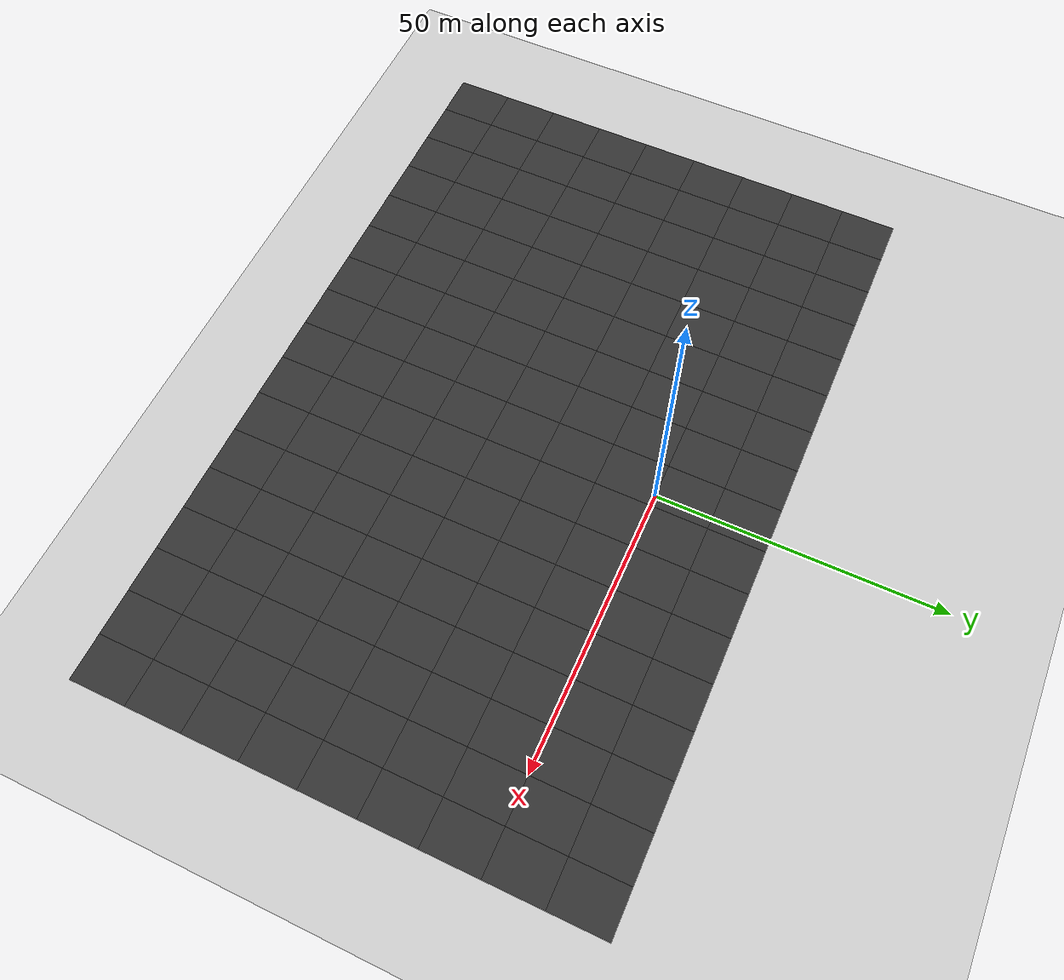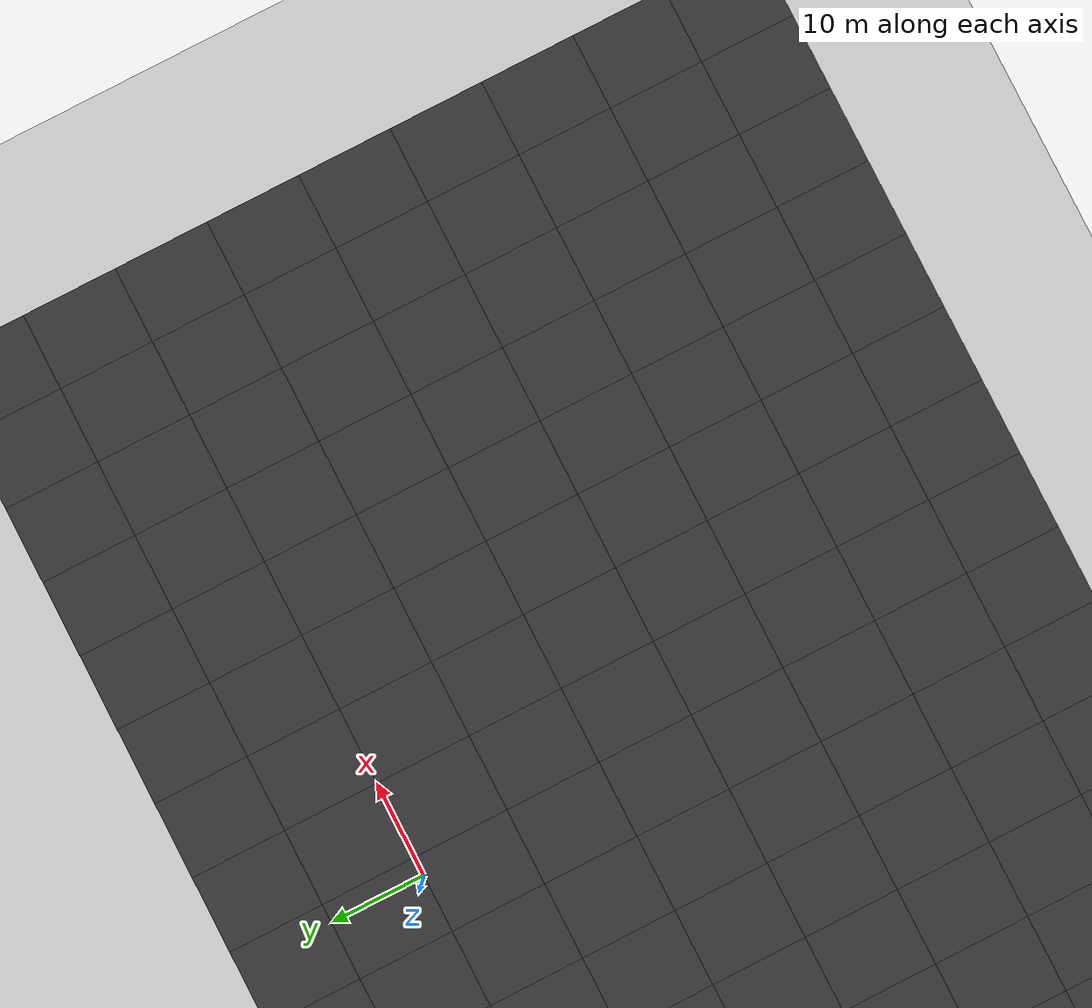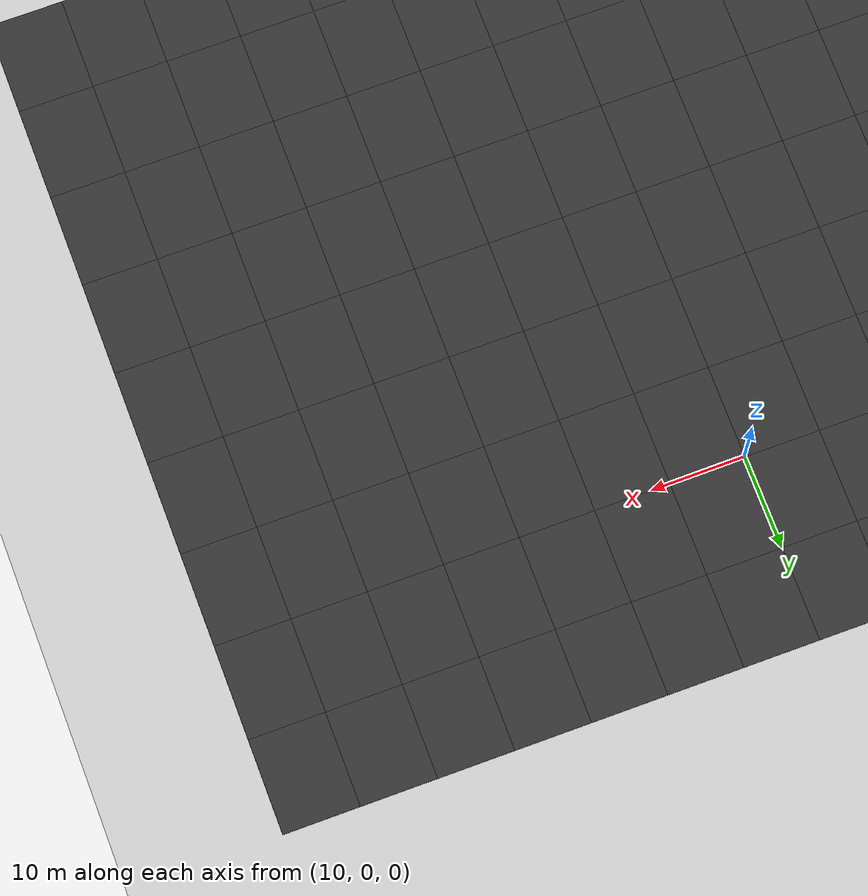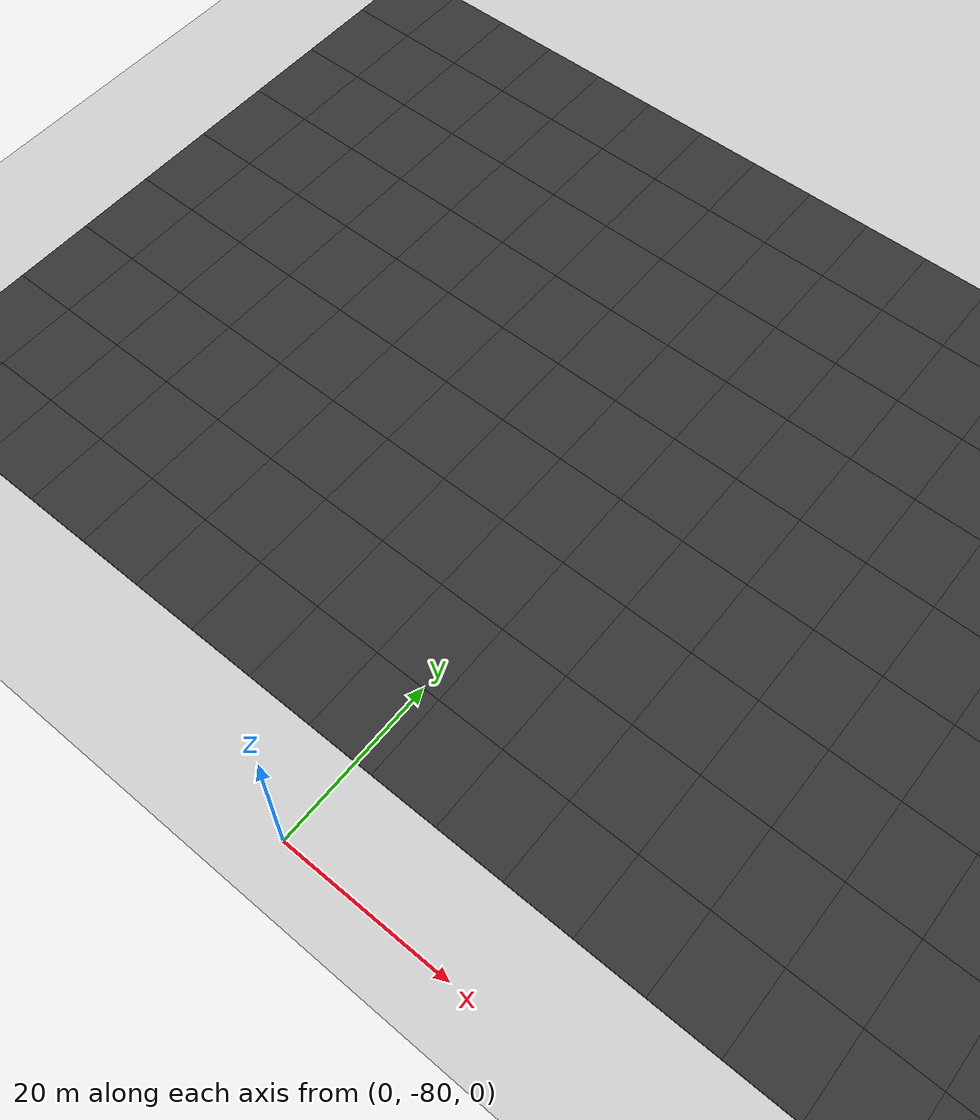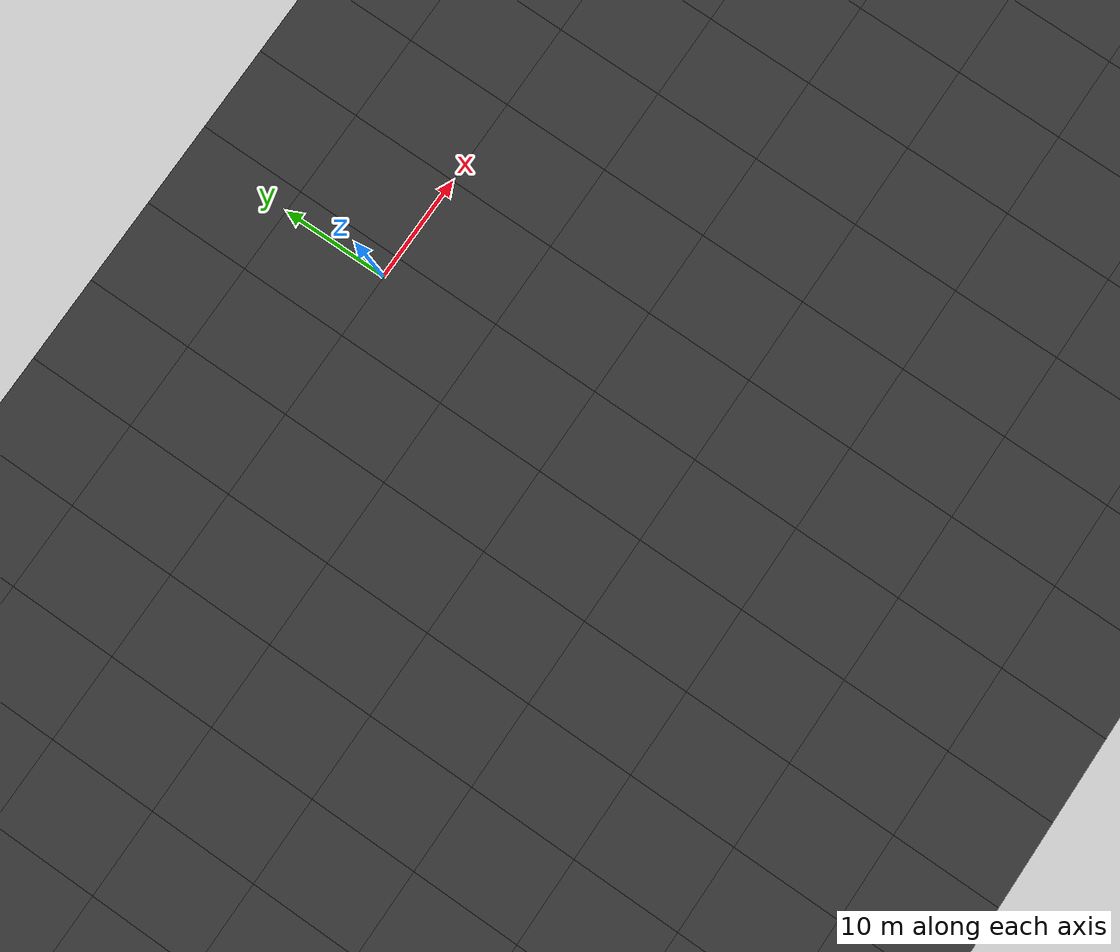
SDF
<sdf version="1.7">
 <world name="default">
  <light name="sun" type="directional">
   <pose>0 0 10 0 -0 0</pose>
   <diffuse>0.8 0.8 0.8 1</diffuse>
   <specular>0.1 0.1 0.1 1</specular>
   <attenuation>
    <range>1000</range>
    <constant>0.9</constant>
    <linear>0.01</linear>
    <quadratic>0.001</quadratic>
   </attenuation>
   <direction>-0.5 0.5 -1</direction>
   <spot><inner_angle>0</inner_angle><outer_angle>0</outer_angle><falloff>0</falloff></spot>
  </light>
  <model name="ground_plane">
   <static>1</static>
   <link name="link">
    <collision name="collision">
     <geometry><plane><normal>0 0 1</normal><size>100 100</size></plane></geometry>
     <surface>
      <contact><collide_bitmask>65535</collide_bitmask></contact>
      <friction><ode><mu>100</mu><mu2>50</mu2></ode></friction>
     </surface>
    </collision>
    <visual name="visual">
     <cast_shadows>0</cast_shadows>
     <geometry><plane><normal>0 0 1</normal><size>100 100</size></plane></geometry>
     <material>
      <script><uri>file://media/materials/scripts/gazebo.material</uri><name>Gazebo/Grey</name></script>
     </material>
    </visual>
   </link>
  </model>
  <gravity>0 0 -9.8</gravity>
  <magnetic_field>6e-06 2.3e-05 -4.2e-05</magnetic_field>
  <atmosphere type="adiabatic"/>
  <physics name="default_physics" default="0" type="ode">
   <max_step_size>0.001</max_step_size>
   <real_time_factor>1</real_time_factor>
   <real_time_update_rate>1000</real_time_update_rate>
  </physics>
  <scene><ambient>0.4 0.4 0.4 1</ambient><background>0.7 0.7 0.7 1</background><shadows>1</shadows></scene>
  <spherical_coordinates>
   <surface_model>EARTH_WGS84</surface_model>
   <latitude_deg>0</latitude_deg>
   <longitude_deg>0</longitude_deg>
   <elevation>0</elevation>
   <heading_deg>0</heading_deg>
  </spherical_coordinates>
  <model name="mud_box">
   <link name="link">
    <inertial>
     <mass>1</mass>
     <inertia><ixx>1</ixx><ixy>0</ixy><ixz>0</ixz><iyy>1</iyy><iyz>0</iyz><izz>1</izz></inertia>
    </inertial>
    <visual name="visual">
     <cast_shadows>0</cast_shadows>
     <geometry><box><size>8 10 0.2</size></box></geometry>
     <material>
      <script>
       <uri>model://mud_box/materials/scripts</uri>
       <uri>model://mud_box/materials/textures</uri>
       <name>vrc/mud</name>
      </script>
      <shader type="pixel"><normal_map>__default__</normal_map></shader>
      <ambient>0.2 0.2 0.2 1</ambient>
      <diffuse>0.2 0.2 0.2 1</diffuse>
      <specular>0.2 0.2 0.2 1</specular>
      <emissive>0 0 0 1</emissive>
     </material>
    </visual>
    <collision name="collision">
     <geometry><box><size>8 10 0.2</size></box></geometry>
     <surface>
      <friction>
       <ode><mu>1</mu><mu2>1</mu2><fdir1>0 0 0</fdir1><slip1>0</slip1><slip2>0</slip2></ode>
       <torsional>
        <coefficient>1</coefficient>
        <patch_radius>0</patch_radius>
        <surface_radius>0</surface_radius>
        <use_patch_radius>1</use_patch_radius>
        <ode><slip>0</slip></ode>
       </torsional>
      </friction>
      <bounce><restitution_coefficient>0</restitution_coefficient><threshold>1e+06</threshold></bounce>
      <contact>
       <collide_without_contact>0</collide_without_contact>
       <collide_without_contact_bitmask>1</collide_without_contact_bitmask>
       <collide_bitmask>1</collide_bitmask>
       <ode>
        <soft_cfm>0</soft_cfm>
        <soft_erp>0.2</soft_erp>
        <kp>1e+13</kp>
        <kd>1</kd>
        <max_vel>0.01</max_vel>
        <min_depth>0</min_depth>
       </ode>
       <bullet>
        <split_impulse>1</split_impulse>
        <split_impulse_penetration_threshold>-0.01</split_impulse_penetration_threshold>
        <soft_cfm>0</soft_cfm>
        <soft_erp>0.2</soft_erp>
        <kp>1e+13</kp>
        <kd>1</kd>
       </bullet>
      </contact>
     </surface>
    </collision>
   </link>
   <static>1</static>
   <pose>46 -45 0 0 -0 0</pose>
  </model>
  <model name="mud_box_0">
   <link name="link">
    <inertial>
     <mass>1</mass>
     <inertia><ixx>1</ixx><ixy>0</ixy><ixz>0</ixz><iyy>1</iyy><iyz>0</iyz><izz>1</izz></inertia>
    </inertial>
    <visual name="visual">
     <cast_shadows>0</cast_shadows>
     <geometry><box><size>8 10 0.2</size></box></geometry>
     <material>
      <script>
       <uri>model://mud_box/materials/scripts</uri>
       <uri>model://mud_box/materials/textures</uri>
       <name>vrc/mud</name>
      </script>
      <shader type="pixel"><normal_map>__default__</normal_map></shader>
      <ambient>0.2 0.2 0.2 1</ambient>
      <diffuse>0.2 0.2 0.2 1</diffuse>
      <specular>0.2 0.2 0.2 1</specular>
      <emissive>0 0 0 1</emissive>
     </material>
    </visual>
    <collision name="collision">
     <geometry><box><size>8 10 0.2</size></box></geometry>
     <surface>
      <friction>
       <ode><mu>1</mu><mu2>1</mu2><fdir1>0 0 0</fdir1><slip1>0</slip1><slip2>0</slip2></ode>
       <torsional>
        <coefficient>1</coefficient>
        <patch_radius>0</patch_radius>
        <surface_radius>0</surface_radius>
        <use_patch_radius>1</use_patch_radius>
        <ode><slip>0</slip></ode>
       </torsional>
      </friction>
      <bounce><restitution_coefficient>0</restitution_coefficient><threshold>1e+06</threshold></bounce>
      <contact>
       <collide_without_contact>0</collide_without_contact>
       <collide_without_contact_bitmask>1</collide_without_contact_bitmask>
       <collide_bitmask>1</collide_bitmask>
       <ode>
        <soft_cfm>0</soft_cfm>
        <soft_erp>0.2</soft_erp>
        <kp>1e+13</kp>
        <kd>1</kd>
        <max_vel>0.01</max_vel>
        <min_depth>0</min_depth>
       </ode>
       <bullet>
        <split_impulse>1</split_impulse>
        <split_impulse_penetration_threshold>-0.01</split_impulse_penetration_threshold>
        <soft_cfm>0</soft_cfm>
        <soft_erp>0.2</soft_erp>
        <kp>1e+13</kp>
        <kd>1</kd>
       </bullet>
      </contact>
     </surface>
    </collision>
   </link>
   <static>1</static>
   <pose>46 -35 0 0 -0 0</pose>
  </model>
  <model name="mud_box_1">
   <link name="link">
    <inertial>
     <mass>1</mass>
     <inertia><ixx>1</ixx><ixy>0</ixy><ixz>0</ixz><iyy>1</iyy><iyz>0</iyz><izz>1</izz></inertia>
    </inertial>
    <visual name="visual">
     <cast_shadows>0</cast_shadows>
     <geometry><box><size>8 10 0.2</size></box></geometry>
     <material>
      <script>
       <uri>model://mud_box/materials/scripts</uri>
       <uri>model://mud_box/materials/textures</uri>
       <name>vrc/mud</name>
      </script>
      <shader type="pixel"><normal_map>__default__</normal_map></shader>
      <ambient>0.2 0.2 0.2 1</ambient>
      <diffuse>0.2 0.2 0.2 1</diffuse>
      <specular>0.2 0.2 0.2 1</specular>
      <emissive>0 0 0 1</emissive>
     </material>
    </visual>
    <collision name="collision">
     <geometry><box><size>8 10 0.2</size></box></geometry>
     <surface>
      <friction>
       <ode><mu>1</mu><mu2>1</mu2><fdir1>0 0 0</fdir1><slip1>0</slip1><slip2>0</slip2></ode>
       <torsional>
        <coefficient>1</coefficient>
        <patch_radius>0</patch_radius>
        <surface_radius>0</surface_radius>
        <use_patch_radius>1</use_patch_radius>
        <ode><slip>0</slip></ode>
       </torsional>
      </friction>
      <bounce><restitution_coefficient>0</restitution_coefficient><threshold>1e+06</threshold></bounce>
      <contact>
       <collide_without_contact>0</collide_without_contact>
       <collide_without_contact_bitmask>1</collide_without_contact_bitmask>
       <collide_bitmask>1</collide_bitmask>
       <ode>
        <soft_cfm>0</soft_cfm>
        <soft_erp>0.2</soft_erp>
        <kp>1e+13</kp>
        <kd>1</kd>
        <max_vel>0.01</max_vel>
        <min_depth>0</min_depth>
       </ode>
       <bullet>
        <split_impulse>1</split_impulse>
        <split_impulse_penetration_threshold>-0.01</split_impulse_penetration_threshold>
        <soft_cfm>0</soft_cfm>
        <soft_erp>0.2</soft_erp>
        <kp>1e+13</kp>
        <kd>1</kd>
       </bullet>
      </contact>
     </surface>
    </collision>
   </link>
   <static>1</static>
   <pose>46 -25 0 0 -0 0</pose>
  </model>
  <model name="mud_box_2">
   <link name="link">
    <inertial>
     <mass>1</mass>
     <inertia><ixx>1</ixx><ixy>0</ixy><ixz>0</ixz><iyy>1</iyy><iyz>0</iyz><izz>1</izz></inertia>
    </inertial>
    <visual name="visual">
     <cast_shadows>0</cast_shadows>
     <geometry><box><size>8 10 0.2</size></box></geometry>
     <material>
      <script>
       <uri>model://mud_box/materials/scripts</uri>
       <uri>model://mud_box/materials/textures</uri>
       <name>vrc/mud</name>
      </script>
      <shader type="pixel"><normal_map>__default__</normal_map></shader>
      <ambient>0.2 0.2 0.2 1</ambient>
      <diffuse>0.2 0.2 0.2 1</diffuse>
      <specular>0.2 0.2 0.2 1</specular>
      <emissive>0 0 0 1</emissive>
     </material>
    </visual>
    <collision name="collision">
     <geometry><box><size>8 10 0.2</size></box></geometry>
     <surface>
      <friction>
       <ode><mu>1</mu><mu2>1</mu2><fdir1>0 0 0</fdir1><slip1>0</slip1><slip2>0</slip2></ode>
       <torsional>
        <coefficient>1</coefficient>
        <patch_radius>0</patch_radius>
        <surface_radius>0</surface_radius>
        <use_patch_radius>1</use_patch_radius>
        <ode><slip>0</slip></ode>
       </torsional>
      </friction>
      <bounce><restitution_coefficient>0</restitution_coefficient><threshold>1e+06</threshold></bounce>
      <contact>
       <collide_without_contact>0</collide_without_contact>
       <collide_without_contact_bitmask>1</collide_without_contact_bitmask>
       <collide_bitmask>1</collide_bitmask>
       <ode>
        <soft_cfm>0</soft_cfm>
        <soft_erp>0.2</soft_erp>
        <kp>1e+13</kp>
        <kd>1</kd>
        <max_vel>0.01</max_vel>
        <min_depth>0</min_depth>
       </ode>
       <bullet>
        <split_impulse>1</split_impulse>
        <split_impulse_penetration_threshold>-0.01</split_impulse_penetration_threshold>
        <soft_cfm>0</soft_cfm>
        <soft_erp>0.2</soft_erp>
        <kp>1e+13</kp>
        <kd>1</kd>
       </bullet>
      </contact>
     </surface>
    </collision>
   </link>
   <static>1</static>
   <pose>46 -15 0 0 -0 0</pose>
  </model>
  <model name="mud_box_3">
   <link name="link">
    <inertial>
     <mass>1</mass>
     <inertia><ixx>1</ixx><ixy>0</ixy><ixz>0</ixz><iyy>1</iyy><iyz>0</iyz><izz>1</izz></inertia>
    </inertial>
    <visual name="visual">
     <cast_shadows>0</cast_shadows>
     <geometry><box><size>8 10 0.2</size></box></geometry>
     <material>
      <script>
       <uri>model://mud_box/materials/scripts</uri>
       <uri>model://mud_box/materials/textures</uri>
       <name>vrc/mud</name>
      </script>
      <shader type="pixel"><normal_map>__default__</normal_map></shader>
      <ambient>0.2 0.2 0.2 1</ambient>
      <diffuse>0.2 0.2 0.2 1</diffuse>
      <specular>0.2 0.2 0.2 1</specular>
      <emissive>0 0 0 1</emissive>
     </material>
    </visual>
    <collision name="collision">
     <geometry><box><size>8 10 0.2</size></box></geometry>
     <surface>
      <friction>
       <ode><mu>1</mu><mu2>1</mu2><fdir1>0 0 0</fdir1><slip1>0</slip1><slip2>0</slip2></ode>
       <torsional>
        <coefficient>1</coefficient>
        <patch_radius>0</patch_radius>
        <surface_radius>0</surface_radius>
        <use_patch_radius>1</use_patch_radius>
        <ode><slip>0</slip></ode>
       </torsional>
      </friction>
      <bounce><restitution_coefficient>0</restitution_coefficient><threshold>1e+06</threshold></bounce>
      <contact>
       <collide_without_contact>0</collide_without_contact>
       <collide_without_contact_bitmask>1</collide_without_contact_bitmask>
       <collide_bitmask>1</collide_bitmask>
       <ode>
        <soft_cfm>0</soft_cfm>
        <soft_erp>0.2</soft_erp>
        <kp>1e+13</kp>
        <kd>1</kd>
        <max_vel>0.01</max_vel>
        <min_depth>0</min_depth>
       </ode>
       <bullet>
        <split_impulse>1</split_impulse>
        <split_impulse_penetration_threshold>-0.01</split_impulse_penetration_threshold>
        <soft_cfm>0</soft_cfm>
        <soft_erp>0.2</soft_erp>
        <kp>1e+13</kp>
        <kd>1</kd>
       </bullet>
      </contact>
     </surface>
    </collision>
   </link>
   <static>1</static>
   <pose>46 -5 0 0 -0 0</pose>
  </model>
  <model name="mud_box_4">
   <link name="link">
    <inertial>
     <mass>1</mass>
     <inertia><ixx>1</ixx><ixy>0</ixy><ixz>0</ixz><iyy>1</iyy><iyz>0</iyz><izz>1</izz></inertia>
    </inertial>
    <visual name="visual">
     <cast_shadows>0</cast_shadows>
     <geometry><box><size>8 10 0.2</size></box></geometry>
     <material>
      <script>
       <uri>model://mud_box/materials/scripts</uri>
       <uri>model://mud_box/materials/textures</uri>
       <name>vrc/mud</name>
      </script>
      <shader type="pixel"><normal_map>__default__</normal_map></shader>
      <ambient>0.2 0.2 0.2 1</ambient>
      <diffuse>0.2 0.2 0.2 1</diffuse>
      <specular>0.2 0.2 0.2 1</specular>
      <emissive>0 0 0 1</emissive>
     </material>
    </visual>
    <collision name="collision">
     <geometry><box><size>8 10 0.2</size></box></geometry>
     <surface>
      <friction>
       <ode><mu>1</mu><mu2>1</mu2><fdir1>0 0 0</fdir1><slip1>0</slip1><slip2>0</slip2></ode>
       <torsional>
        <coefficient>1</coefficient>
        <patch_radius>0</patch_radius>
        <surface_radius>0</surface_radius>
        <use_patch_radius>1</use_patch_radius>
        <ode><slip>0</slip></ode>
       </torsional>
      </friction>
      <bounce><restitution_coefficient>0</restitution_coefficient><threshold>1e+06</threshold></bounce>
      <contact>
       <collide_without_contact>0</collide_without_contact>
       <collide_without_contact_bitmask>1</collide_without_contact_bitmask>
       <collide_bitmask>1</collide_bitmask>
       <ode>
        <soft_cfm>0</soft_cfm>
        <soft_erp>0.2</soft_erp>
        <kp>1e+13</kp>
        <kd>1</kd>
        <max_vel>0.01</max_vel>
        <min_depth>0</min_depth>
       </ode>
       <bullet>
        <split_impulse>1</split_impulse>
        <split_impulse_penetration_threshold>-0.01</split_impulse_penetration_threshold>
        <soft_cfm>0</soft_cfm>
        <soft_erp>0.2</soft_erp>
        <kp>1e+13</kp>
        <kd>1</kd>
       </bullet>
      </contact>
     </surface>
    </collision>
   </link>
   <static>1</static>
   <pose>38 -45 0 0 -0 0</pose>
  </model>
  <model name="mud_box_5">
   <link name="link">
    <inertial>
     <mass>1</mass>
     <inertia><ixx>1</ixx><ixy>0</ixy><ixz>0</ixz><iyy>1</iyy><iyz>0</iyz><izz>1</izz></inertia>
    </inertial>
    <visual name="visual">
     <cast_shadows>0</cast_shadows>
     <geometry><box><size>8 10 0.2</size></box></geometry>
     <material>
      <script>
       <uri>model://mud_box/materials/scripts</uri>
       <uri>model://mud_box/materials/textures</uri>
       <name>vrc/mud</name>
      </script>
      <shader type="pixel"><normal_map>__default__</normal_map></shader>
      <ambient>0.2 0.2 0.2 1</ambient>
      <diffuse>0.2 0.2 0.2 1</diffuse>
      <specular>0.2 0.2 0.2 1</specular>
      <emissive>0 0 0 1</emissive>
     </material>
    </visual>
    <collision name="collision">
     <geometry><box><size>8 10 0.2</size></box></geometry>
     <surface>
      <friction>
       <ode><mu>1</mu><mu2>1</mu2><fdir1>0 0 0</fdir1><slip1>0</slip1><slip2>0</slip2></ode>
       <torsional>
        <coefficient>1</coefficient>
        <patch_radius>0</patch_radius>
        <surface_radius>0</surface_radius>
        <use_patch_radius>1</use_patch_radius>
        <ode><slip>0</slip></ode>
       </torsional>
      </friction>
      <bounce><restitution_coefficient>0</restitution_coefficient><threshold>1e+06</threshold></bounce>
      <contact>
       <collide_without_contact>0</collide_without_contact>
       <collide_without_contact_bitmask>1</collide_without_contact_bitmask>
       <collide_bitmask>1</collide_bitmask>
       <ode>
        <soft_cfm>0</soft_cfm>
        <soft_erp>0.2</soft_erp>
        <kp>1e+13</kp>
        <kd>1</kd>
        <max_vel>0.01</max_vel>
        <min_depth>0</min_depth>
       </ode>
       <bullet>
        <split_impulse>1</split_impulse>
        <split_impulse_penetration_threshold>-0.01</split_impulse_penetration_threshold>
        <soft_cfm>0</soft_cfm>
        <soft_erp>0.2</soft_erp>
        <kp>1e+13</kp>
        <kd>1</kd>
       </bullet>
      </contact>
     </surface>
    </collision>
   </link>
   <static>1</static>
   <pose>38 -35 0 0 -0 0</pose>
  </model>
  <model name="mud_box_6">
   <link name="link">
    <inertial>
     <mass>1</mass>
     <inertia><ixx>1</ixx><ixy>0</ixy><ixz>0</ixz><iyy>1</iyy><iyz>0</iyz><izz>1</izz></inertia>
    </inertial>
    <visual name="visual">
     <cast_shadows>0</cast_shadows>
     <geometry><box><size>8 10 0.2</size></box></geometry>
     <material>
      <script>
       <uri>model://mud_box/materials/scripts</uri>
       <uri>model://mud_box/materials/textures</uri>
       <name>vrc/mud</name>
      </script>
      <shader type="pixel"><normal_map>__default__</normal_map></shader>
      <ambient>0.2 0.2 0.2 1</ambient>
      <diffuse>0.2 0.2 0.2 1</diffuse>
      <specular>0.2 0.2 0.2 1</specular>
      <emissive>0 0 0 1</emissive>
     </material>
    </visual>
    <collision name="collision">
     <geometry><box><size>8 10 0.2</size></box></geometry>
     <surface>
      <friction>
       <ode><mu>1</mu><mu2>1</mu2><fdir1>0 0 0</fdir1><slip1>0</slip1><slip2>0</slip2></ode>
       <torsional>
        <coefficient>1</coefficient>
        <patch_radius>0</patch_radius>
        <surface_radius>0</surface_radius>
        <use_patch_radius>1</use_patch_radius>
        <ode><slip>0</slip></ode>
       </torsional>
      </friction>
      <bounce><restitution_coefficient>0</restitution_coefficient><threshold>1e+06</threshold></bounce>
      <contact>
       <collide_without_contact>0</collide_without_contact>
       <collide_without_contact_bitmask>1</collide_without_contact_bitmask>
       <collide_bitmask>1</collide_bitmask>
       <ode>
        <soft_cfm>0</soft_cfm>
        <soft_erp>0.2</soft_erp>
        <kp>1e+13</kp>
        <kd>1</kd>
        <max_vel>0.01</max_vel>
        <min_depth>0</min_depth>
       </ode>
       <bullet>
        <split_impulse>1</split_impulse>
        <split_impulse_penetration_threshold>-0.01</split_impulse_penetration_threshold>
        <soft_cfm>0</soft_cfm>
        <soft_erp>0.2</soft_erp>
        <kp>1e+13</kp>
        <kd>1</kd>
       </bullet>
      </contact>
     </surface>
    </collision>
   </link>
   <static>1</static>
   <pose>38 -25 0 0 -0 0</pose>
  </model>
  <model name="mud_box_7">
   <link name="link">
    <inertial>
     <mass>1</mass>
     <inertia><ixx>1</ixx><ixy>0</ixy><ixz>0</ixz><iyy>1</iyy><iyz>0</iyz><izz>1</izz></inertia>
    </inertial>
    <visual name="visual">
     <cast_shadows>0</cast_shadows>
     <geometry><box><size>8 10 0.2</size></box></geometry>
     <material>
      <script>
       <uri>model://mud_box/materials/scripts</uri>
       <uri>model://mud_box/materials/textures</uri>
       <name>vrc/mud</name>
      </script>
      <shader type="pixel"><normal_map>__default__</normal_map></shader>
      <ambient>0.2 0.2 0.2 1</ambient>
      <diffuse>0.2 0.2 0.2 1</diffuse>
      <specular>0.2 0.2 0.2 1</specular>
      <emissive>0 0 0 1</emissive>
     </material>
    </visual>
    <collision name="collision">
     <geometry><box><size>8 10 0.2</size></box></geometry>
     <surface>
      <friction>
       <ode><mu>1</mu><mu2>1</mu2><fdir1>0 0 0</fdir1><slip1>0</slip1><slip2>0</slip2></ode>
       <torsional>
        <coefficient>1</coefficient>
        <patch_radius>0</patch_radius>
        <surface_radius>0</surface_radius>
        <use_patch_radius>1</use_patch_radius>
        <ode><slip>0</slip></ode>
       </torsional>
      </friction>
      <bounce><restitution_coefficient>0</restitution_coefficient><threshold>1e+06</threshold></bounce>
      <contact>
       <collide_without_contact>0</collide_without_contact>
       <collide_without_contact_bitmask>1</collide_without_contact_bitmask>
       <collide_bitmask>1</collide_bitmask>
       <ode>
        <soft_cfm>0</soft_cfm>
        <soft_erp>0.2</soft_erp>
        <kp>1e+13</kp>
        <kd>1</kd>
        <max_vel>0.01</max_vel>
        <min_depth>0</min_depth>
       </ode>
       <bullet>
        <split_impulse>1</split_impulse>
        <split_impulse_penetration_threshold>-0.01</split_impulse_penetration_threshold>
        <soft_cfm>0</soft_cfm>
        <soft_erp>0.2</soft_erp>
        <kp>1e+13</kp>
        <kd>1</kd>
       </bullet>
      </contact>
     </surface>
    </collision>
   </link>
   <static>1</static>
   <pose>38 -15 0 0 -0 0</pose>
  </model>
  <model name="mud_box_8">
   <link name="link">
    <inertial>
     <mass>1</mass>
     <inertia><ixx>1</ixx><ixy>0</ixy><ixz>0</ixz><iyy>1</iyy><iyz>0</iyz><izz>1</izz></inertia>
    </inertial>
    <visual name="visual">
     <cast_shadows>0</cast_shadows>
     <geometry><box><size>8 10 0.2</size></box></geometry>
     <material>
      <script>
       <uri>model://mud_box/materials/scripts</uri>
       <uri>model://mud_box/materials/textures</uri>
       <name>vrc/mud</name>
      </script>
      <shader type="pixel"><normal_map>__default__</normal_map></shader>
      <ambient>0.2 0.2 0.2 1</ambient>
      <diffuse>0.2 0.2 0.2 1</diffuse>
      <specular>0.2 0.2 0.2 1</specular>
      <emissive>0 0 0 1</emissive>
     </material>
    </visual>
    <collision name="collision">
     <geometry><box><size>8 10 0.2</size></box></geometry>
     <surface>
      <friction>
       <ode><mu>1</mu><mu2>1</mu2><fdir1>0 0 0</fdir1><slip1>0</slip1><slip2>0</slip2></ode>
       <torsional>
        <coefficient>1</coefficient>
        <patch_radius>0</patch_radius>
        <surface_radius>0</surface_radius>
        <use_patch_radius>1</use_patch_radius>
        <ode><slip>0</slip></ode>
       </torsional>
      </friction>
      <bounce><restitution_coefficient>0</restitution_coefficient><threshold>1e+06</threshold></bounce>
      <contact>
       <collide_without_contact>0</collide_without_contact>
       <collide_without_contact_bitmask>1</collide_without_contact_bitmask>
       <collide_bitmask>1</collide_bitmask>
       <ode>
        <soft_cfm>0</soft_cfm>
        <soft_erp>0.2</soft_erp>
        <kp>1e+13</kp>
        <kd>1</kd>
        <max_vel>0.01</max_vel>
        <min_depth>0</min_depth>
       </ode>
       <bullet>
        <split_impulse>1</split_impulse>
        <split_impulse_penetration_threshold>-0.01</split_impulse_penetration_threshold>
        <soft_cfm>0</soft_cfm>
        <soft_erp>0.2</soft_erp>
        <kp>1e+13</kp>
        <kd>1</kd>
       </bullet>
      </contact>
     </surface>
    </collision>
   </link>
   <static>1</static>
   <pose>38 -5 0 0 -0 0</pose>
  </model>
  <model name="mud_box_9">
   <link name="link">
    <inertial>
     <mass>1</mass>
     <inertia><ixx>1</ixx><ixy>0</ixy><ixz>0</ixz><iyy>1</iyy><iyz>0</iyz><izz>1</izz></inertia>
    </inertial>
    <visual name="visual">
     <cast_shadows>0</cast_shadows>
     <geometry><box><size>8 10 0.2</size></box></geometry>
     <material>
      <script>
       <uri>model://mud_box/materials/scripts</uri>
       <uri>model://mud_box/materials/textures</uri>
       <name>vrc/mud</name>
      </script>
      <shader type="pixel"><normal_map>__default__</normal_map></shader>
      <ambient>0.2 0.2 0.2 1</ambient>
      <diffuse>0.2 0.2 0.2 1</diffuse>
      <specular>0.2 0.2 0.2 1</specular>
      <emissive>0 0 0 1</emissive>
     </material>
    </visual>
    <collision name="collision">
     <geometry><box><size>8 10 0.2</size></box></geometry>
     <surface>
      <friction>
       <ode><mu>1</mu><mu2>1</mu2><fdir1>0 0 0</fdir1><slip1>0</slip1><slip2>0</slip2></ode>
       <torsional>
        <coefficient>1</coefficient>
        <patch_radius>0</patch_radius>
        <surface_radius>0</surface_radius>
        <use_patch_radius>1</use_patch_radius>
        <ode><slip>0</slip></ode>
       </torsional>
      </friction>
      <bounce><restitution_coefficient>0</restitution_coefficient><threshold>1e+06</threshold></bounce>
      <contact>
       <collide_without_contact>0</collide_without_contact>
       <collide_without_contact_bitmask>1</collide_without_contact_bitmask>
       <collide_bitmask>1</collide_bitmask>
       <ode>
        <soft_cfm>0</soft_cfm>
        <soft_erp>0.2</soft_erp>
        <kp>1e+13</kp>
        <kd>1</kd>
        <max_vel>0.01</max_vel>
        <min_depth>0</min_depth>
       </ode>
       <bullet>
        <split_impulse>1</split_impulse>
        <split_impulse_penetration_threshold>-0.01</split_impulse_penetration_threshold>
        <soft_cfm>0</soft_cfm>
        <soft_erp>0.2</soft_erp>
        <kp>1e+13</kp>
        <kd>1</kd>
       </bullet>
      </contact>
     </surface>
    </collision>
   </link>
   <static>1</static>
   <pose>30 -45 0 0 -0 0</pose>
  </model>
  <model name="mud_box_10">
   <link name="link">
    <inertial>
     <mass>1</mass>
     <inertia><ixx>1</ixx><ixy>0</ixy><ixz>0</ixz><iyy>1</iyy><iyz>0</iyz><izz>1</izz></inertia>
    </inertial>
    <visual name="visual">
     <cast_shadows>0</cast_shadows>
     <geometry><box><size>8 10 0.2</size></box></geometry>
     <material>
      <script>
       <uri>model://mud_box/materials/scripts</uri>
       <uri>model://mud_box/materials/textures</uri>
       <name>vrc/mud</name>
      </script>
      <shader type="pixel"><normal_map>__default__</normal_map></shader>
      <ambient>0.2 0.2 0.2 1</ambient>
      <diffuse>0.2 0.2 0.2 1</diffuse>
      <specular>0.2 0.2 0.2 1</specular>
      <emissive>0 0 0 1</emissive>
     </material>
    </visual>
    <collision name="collision">
     <geometry><box><size>8 10 0.2</size></box></geometry>
     <surface>
      <friction>
       <ode><mu>1</mu><mu2>1</mu2><fdir1>0 0 0</fdir1><slip1>0</slip1><slip2>0</slip2></ode>
       <torsional>
        <coefficient>1</coefficient>
        <patch_radius>0</patch_radius>
        <surface_radius>0</surface_radius>
        <use_patch_radius>1</use_patch_radius>
        <ode><slip>0</slip></ode>
       </torsional>
      </friction>
      <bounce><restitution_coefficient>0</restitution_coefficient><threshold>1e+06</threshold></bounce>
      <contact>
       <collide_without_contact>0</collide_without_contact>
       <collide_without_contact_bitmask>1</collide_without_contact_bitmask>
       <collide_bitmask>1</collide_bitmask>
       <ode>
        <soft_cfm>0</soft_cfm>
        <soft_erp>0.2</soft_erp>
        <kp>1e+13</kp>
        <kd>1</kd>
        <max_vel>0.01</max_vel>
        <min_depth>0</min_depth>
       </ode>
       <bullet>
        <split_impulse>1</split_impulse>
        <split_impulse_penetration_threshold>-0.01</split_impulse_penetration_threshold>
        <soft_cfm>0</soft_cfm>
        <soft_erp>0.2</soft_erp>
        <kp>1e+13</kp>
        <kd>1</kd>
       </bullet>
      </contact>
     </surface>
    </collision>
   </link>
   <static>1</static>
   <pose>30 -35 0 0 -0 0</pose>
  </model>
  <model name="mud_box_11">
   <link name="link">
    <inertial>
     <mass>1</mass>
     <inertia><ixx>1</ixx><ixy>0</ixy><ixz>0</ixz><iyy>1</iyy><iyz>0</iyz><izz>1</izz></inertia>
    </inertial>
    <visual name="visual">
     <cast_shadows>0</cast_shadows>
     <geometry><box><size>8 10 0.2</size></box></geometry>
     <material>
      <script>
       <uri>model://mud_box/materials/scripts</uri>
       <uri>model://mud_box/materials/textures</uri>
       <name>vrc/mud</name>
      </script>
      <shader type="pixel"><normal_map>__default__</normal_map></shader>
      <ambient>0.2 0.2 0.2 1</ambient>
      <diffuse>0.2 0.2 0.2 1</diffuse>
      <specular>0.2 0.2 0.2 1</specular>
      <emissive>0 0 0 1</emissive>
     </material>
    </visual>
    <collision name="collision">
     <geometry><box><size>8 10 0.2</size></box></geometry>
     <surface>
      <friction>
       <ode><mu>1</mu><mu2>1</mu2><fdir1>0 0 0</fdir1><slip1>0</slip1><slip2>0</slip2></ode>
       <torsional>
        <coefficient>1</coefficient>
        <patch_radius>0</patch_radius>
        <surface_radius>0</surface_radius>
        <use_patch_radius>1</use_patch_radius>
        <ode><slip>0</slip></ode>
       </torsional>
      </friction>
      <bounce><restitution_coefficient>0</restitution_coefficient><threshold>1e+06</threshold></bounce>
      <contact>
       <collide_without_contact>0</collide_without_contact>
       <collide_without_contact_bitmask>1</collide_without_contact_bitmask>
       <collide_bitmask>1</collide_bitmask>
       <ode>
        <soft_cfm>0</soft_cfm>
        <soft_erp>0.2</soft_erp>
        <kp>1e+13</kp>
        <kd>1</kd>
        <max_vel>0.01</max_vel>
        <min_depth>0</min_depth>
       </ode>
       <bullet>
        <split_impulse>1</split_impulse>
        <split_impulse_penetration_threshold>-0.01</split_impulse_penetration_threshold>
        <soft_cfm>0</soft_cfm>
        <soft_erp>0.2</soft_erp>
        <kp>1e+13</kp>
        <kd>1</kd>
       </bullet>
      </contact>
     </surface>
    </collision>
   </link>
   <static>1</static>
   <pose>30 -25 0 0 -0 0</pose>
  </model>
  <model name="mud_box_12">
   <link name="link">
    <inertial>
     <mass>1</mass>
     <inertia><ixx>1</ixx><ixy>0</ixy><ixz>0</ixz><iyy>1</iyy><iyz>0</iyz><izz>1</izz></inertia>
    </inertial>
    <visual name="visual">
     <cast_shadows>0</cast_shadows>
     <geometry><box><size>8 10 0.2</size></box></geometry>
     <material>
      <script>
       <uri>model://mud_box/materials/scripts</uri>
       <uri>model://mud_box/materials/textures</uri>
       <name>vrc/mud</name>
      </script>
      <shader type="pixel"><normal_map>__default__</normal_map></shader>
      <ambient>0.2 0.2 0.2 1</ambient>
      <diffuse>0.2 0.2 0.2 1</diffuse>
      <specular>0.2 0.2 0.2 1</specular>
      <emissive>0 0 0 1</emissive>
     </material>
    </visual>
    <collision name="collision">
     <geometry><box><size>8 10 0.2</size></box></geometry>
     <surface>
      <friction>
       <ode><mu>1</mu><mu2>1</mu2><fdir1>0 0 0</fdir1><slip1>0</slip1><slip2>0</slip2></ode>
       <torsional>
        <coefficient>1</coefficient>
        <patch_radius>0</patch_radius>
        <surface_radius>0</surface_radius>
        <use_patch_radius>1</use_patch_radius>
        <ode><slip>0</slip></ode>
       </torsional>
      </friction>
      <bounce><restitution_coefficient>0</restitution_coefficient><threshold>1e+06</threshold></bounce>
      <contact>
       <collide_without_contact>0</collide_without_contact>
       <collide_without_contact_bitmask>1</collide_without_contact_bitmask>
       <collide_bitmask>1</collide_bitmask>
       <ode>
        <soft_cfm>0</soft_cfm>
        <soft_erp>0.2</soft_erp>
        <kp>1e+13</kp>
        <kd>1</kd>
        <max_vel>0.01</max_vel>
        <min_depth>0</min_depth>
       </ode>
       <bullet>
        <split_impulse>1</split_impulse>
        <split_impulse_penetration_threshold>-0.01</split_impulse_penetration_threshold>
        <soft_cfm>0</soft_cfm>
        <soft_erp>0.2</soft_erp>
        <kp>1e+13</kp>
        <kd>1</kd>
       </bullet>
      </contact>
     </surface>
    </collision>
   </link>
   <static>1</static>
   <pose>30 -15 0 0 -0 0</pose>
  </model>
  <model name="mud_box_13">
   <link name="link">
    <inertial>
     <mass>1</mass>
     <inertia><ixx>1</ixx><ixy>0</ixy><ixz>0</ixz><iyy>1</iyy><iyz>0</iyz><izz>1</izz></inertia>
    </inertial>
    <visual name="visual">
     <cast_shadows>0</cast_shadows>
     <geometry><box><size>8 10 0.2</size></box></geometry>
     <material>
      <script>
       <uri>model://mud_box/materials/scripts</uri>
       <uri>model://mud_box/materials/textures</uri>
       <name>vrc/mud</name>
      </script>
      <shader type="pixel"><normal_map>__default__</normal_map></shader>
      <ambient>0.2 0.2 0.2 1</ambient>
      <diffuse>0.2 0.2 0.2 1</diffuse>
      <specular>0.2 0.2 0.2 1</specular>
      <emissive>0 0 0 1</emissive>
     </material>
    </visual>
    <collision name="collision">
     <geometry><box><size>8 10 0.2</size></box></geometry>
     <surface>
      <friction>
       <ode><mu>1</mu><mu2>1</mu2><fdir1>0 0 0</fdir1><slip1>0</slip1><slip2>0</slip2></ode>
       <torsional>
        <coefficient>1</coefficient>
        <patch_radius>0</patch_radius>
        <surface_radius>0</surface_radius>
        <use_patch_radius>1</use_patch_radius>
        <ode><slip>0</slip></ode>
       </torsional>
      </friction>
      <bounce><restitution_coefficient>0</restitution_coefficient><threshold>1e+06</threshold></bounce>
      <contact>
       <collide_without_contact>0</collide_without_contact>
       <collide_without_contact_bitmask>1</collide_without_contact_bitmask>
       <collide_bitmask>1</collide_bitmask>
       <ode>
        <soft_cfm>0</soft_cfm>
        <soft_erp>0.2</soft_erp>
        <kp>1e+13</kp>
        <kd>1</kd>
        <max_vel>0.01</max_vel>
        <min_depth>0</min_depth>
       </ode>
       <bullet>
        <split_impulse>1</split_impulse>
        <split_impulse_penetration_threshold>-0.01</split_impulse_penetration_threshold>
        <soft_cfm>0</soft_cfm>
        <soft_erp>0.2</soft_erp>
        <kp>1e+13</kp>
        <kd>1</kd>
       </bullet>
      </contact>
     </surface>
    </collision>
   </link>
   <static>1</static>
   <pose>30 -5 0 0 -0 0</pose>
  </model>
  <model name="mud_box_14">
   <link name="link">
    <inertial>
     <mass>1</mass>
     <inertia><ixx>1</ixx><ixy>0</ixy><ixz>0</ixz><iyy>1</iyy><iyz>0</iyz><izz>1</izz></inertia>
    </inertial>
    <visual name="visual">
     <cast_shadows>0</cast_shadows>
     <geometry><box><size>8 10 0.2</size></box></geometry>
     <material>
      <script>
       <uri>model://mud_box/materials/scripts</uri>
       <uri>model://mud_box/materials/textures</uri>
       <name>vrc/mud</name>
      </script>
      <shader type="pixel"><normal_map>__default__</normal_map></shader>
      <ambient>0.2 0.2 0.2 1</ambient>
      <diffuse>0.2 0.2 0.2 1</diffuse>
      <specular>0.2 0.2 0.2 1</specular>
      <emissive>0 0 0 1</emissive>
     </material>
    </visual>
    <collision name="collision">
     <geometry><box><size>8 10 0.2</size></box></geometry>
     <surface>
      <friction>
       <ode><mu>1</mu><mu2>1</mu2><fdir1>0 0 0</fdir1><slip1>0</slip1><slip2>0</slip2></ode>
       <torsional>
        <coefficient>1</coefficient>
        <patch_radius>0</patch_radius>
        <surface_radius>0</surface_radius>
        <use_patch_radius>1</use_patch_radius>
        <ode><slip>0</slip></ode>
       </torsional>
      </friction>
      <bounce><restitution_coefficient>0</restitution_coefficient><threshold>1e+06</threshold></bounce>
      <contact>
       <collide_without_contact>0</collide_without_contact>
       <collide_without_contact_bitmask>1</collide_without_contact_bitmask>
       <collide_bitmask>1</collide_bitmask>
       <ode>
        <soft_cfm>0</soft_cfm>
        <soft_erp>0.2</soft_erp>
        <kp>1e+13</kp>
        <kd>1</kd>
        <max_vel>0.01</max_vel>
        <min_depth>0</min_depth>
       </ode>
       <bullet>
        <split_impulse>1</split_impulse>
        <split_impulse_penetration_threshold>-0.01</split_impulse_penetration_threshold>
        <soft_cfm>0</soft_cfm>
        <soft_erp>0.2</soft_erp>
        <kp>1e+13</kp>
        <kd>1</kd>
       </bullet>
      </contact>
     </surface>
    </collision>
   </link>
   <static>1</static>
   <pose>22 -5 0 0 -0 0</pose>
  </model>
  <model name="mud_box_15">
   <link name="link">
    <inertial>
     <mass>1</mass>
     <inertia><ixx>1</ixx><ixy>0</ixy><ixz>0</ixz><iyy>1</iyy><iyz>0</iyz><izz>1</izz></inertia>
    </inertial>
    <visual name="visual">
     <cast_shadows>0</cast_shadows>
     <geometry><box><size>8 10 0.2</size></box></geometry>
     <material>
      <script>
       <uri>model://mud_box/materials/scripts</uri>
       <uri>model://mud_box/materials/textures</uri>
       <name>vrc/mud</name>
      </script>
      <shader type="pixel"><normal_map>__default__</normal_map></shader>
      <ambient>0.2 0.2 0.2 1</ambient>
      <diffuse>0.2 0.2 0.2 1</diffuse>
      <specular>0.2 0.2 0.2 1</specular>
      <emissive>0 0 0 1</emissive>
     </material>
    </visual>
    <collision name="collision">
     <geometry><box><size>8 10 0.2</size></box></geometry>
     <surface>
      <friction>
       <ode><mu>1</mu><mu2>1</mu2><fdir1>0 0 0</fdir1><slip1>0</slip1><slip2>0</slip2></ode>
       <torsional>
        <coefficient>1</coefficient>
        <patch_radius>0</patch_radius>
        <surface_radius>0</surface_radius>
        <use_patch_radius>1</use_patch_radius>
        <ode><slip>0</slip></ode>
       </torsional>
      </friction>
      <bounce><restitution_coefficient>0</restitution_coefficient><threshold>1e+06</threshold></bounce>
      <contact>
       <collide_without_contact>0</collide_without_contact>
       <collide_without_contact_bitmask>1</collide_without_contact_bitmask>
       <collide_bitmask>1</collide_bitmask>
       <ode>
        <soft_cfm>0</soft_cfm>
        <soft_erp>0.2</soft_erp>
        <kp>1e+13</kp>
        <kd>1</kd>
        <max_vel>0.01</max_vel>
        <min_depth>0</min_depth>
       </ode>
       <bullet>
        <split_impulse>1</split_impulse>
        <split_impulse_penetration_threshold>-0.01</split_impulse_penetration_threshold>
        <soft_cfm>0</soft_cfm>
        <soft_erp>0.2</soft_erp>
        <kp>1e+13</kp>
        <kd>1</kd>
       </bullet>
      </contact>
     </surface>
    </collision>
   </link>
   <static>1</static>
   <pose>22 -15 0 0 -0 0</pose>
  </model>
  <model name="mud_box_16">
   <link name="link">
    <inertial>
     <mass>1</mass>
     <inertia><ixx>1</ixx><ixy>0</ixy><ixz>0</ixz><iyy>1</iyy><iyz>0</iyz><izz>1</izz></inertia>
    </inertial>
    <visual name="visual">
     <cast_shadows>0</cast_shadows>
     <geometry><box><size>8 10 0.2</size></box></geometry>
     <material>
      <script>
       <uri>model://mud_box/materials/scripts</uri>
       <uri>model://mud_box/materials/textures</uri>
       <name>vrc/mud</name>
      </script>
      <shader type="pixel"><normal_map>__default__</normal_map></shader>
      <ambient>0.2 0.2 0.2 1</ambient>
      <diffuse>0.2 0.2 0.2 1</diffuse>
      <specular>0.2 0.2 0.2 1</specular>
      <emissive>0 0 0 1</emissive>
     </material>
    </visual>
    <collision name="collision">
     <geometry><box><size>8 10 0.2</size></box></geometry>
     <surface>
      <friction>
       <ode><mu>1</mu><mu2>1</mu2><fdir1>0 0 0</fdir1><slip1>0</slip1><slip2>0</slip2></ode>
       <torsional>
        <coefficient>1</coefficient>
        <patch_radius>0</patch_radius>
        <surface_radius>0</surface_radius>
        <use_patch_radius>1</use_patch_radius>
        <ode><slip>0</slip></ode>
       </torsional>
      </friction>
      <bounce><restitution_coefficient>0</restitution_coefficient><threshold>1e+06</threshold></bounce>
      <contact>
       <collide_without_contact>0</collide_without_contact>
       <collide_without_contact_bitmask>1</collide_without_contact_bitmask>
       <collide_bitmask>1</collide_bitmask>
       <ode>
        <soft_cfm>0</soft_cfm>
        <soft_erp>0.2</soft_erp>
        <kp>1e+13</kp>
        <kd>1</kd>
        <max_vel>0.01</max_vel>
        <min_depth>0</min_depth>
       </ode>
       <bullet>
        <split_impulse>1</split_impulse>
        <split_impulse_penetration_threshold>-0.01</split_impulse_penetration_threshold>
        <soft_cfm>0</soft_cfm>
        <soft_erp>0.2</soft_erp>
        <kp>1e+13</kp>
        <kd>1</kd>
       </bullet>
      </contact>
     </surface>
    </collision>
   </link>
   <static>1</static>
   <pose>22 -25 0 0 -0 0</pose>
  </model>
  <model name="mud_box_17">
   <link name="link">
    <inertial>
     <mass>1</mass>
     <inertia><ixx>1</ixx><ixy>0</ixy><ixz>0</ixz><iyy>1</iyy><iyz>0</iyz><izz>1</izz></inertia>
    </inertial>
    <visual name="visual">
     <cast_shadows>0</cast_shadows>
     <geometry><box><size>8 10 0.2</size></box></geometry>
     <material>
      <script>
       <uri>model://mud_box/materials/scripts</uri>
       <uri>model://mud_box/materials/textures</uri>
       <name>vrc/mud</name>
      </script>
      <shader type="pixel"><normal_map>__default__</normal_map></shader>
      <ambient>0.2 0.2 0.2 1</ambient>
      <diffuse>0.2 0.2 0.2 1</diffuse>
      <specular>0.2 0.2 0.2 1</specular>
      <emissive>0 0 0 1</emissive>
     </material>
    </visual>
    <collision name="collision">
     <geometry><box><size>8 10 0.2</size></box></geometry>
     <surface>
      <friction>
       <ode><mu>1</mu><mu2>1</mu2><fdir1>0 0 0</fdir1><slip1>0</slip1><slip2>0</slip2></ode>
       <torsional>
        <coefficient>1</coefficient>
        <patch_radius>0</patch_radius>
        <surface_radius>0</surface_radius>
        <use_patch_radius>1</use_patch_radius>
        <ode><slip>0</slip></ode>
       </torsional>
      </friction>
      <bounce><restitution_coefficient>0</restitution_coefficient><threshold>1e+06</threshold></bounce>
      <contact>
       <collide_without_contact>0</collide_without_contact>
       <collide_without_contact_bitmask>1</collide_without_contact_bitmask>
       <collide_bitmask>1</collide_bitmask>
       <ode>
        <soft_cfm>0</soft_cfm>
        <soft_erp>0.2</soft_erp>
        <kp>1e+13</kp>
        <kd>1</kd>
        <max_vel>0.01</max_vel>
        <min_depth>0</min_depth>
       </ode>
       <bullet>
        <split_impulse>1</split_impulse>
        <split_impulse_penetration_threshold>-0.01</split_impulse_penetration_threshold>
        <soft_cfm>0</soft_cfm>
        <soft_erp>0.2</soft_erp>
        <kp>1e+13</kp>
        <kd>1</kd>
       </bullet>
      </contact>
     </surface>
    </collision>
   </link>
   <static>1</static>
   <pose>22 -35 0 0 -0 0</pose>
  </model>
  <model name="mud_box_18">
   <link name="link">
    <inertial>
     <mass>1</mass>
     <inertia><ixx>1</ixx><ixy>0</ixy><ixz>0</ixz><iyy>1</iyy><iyz>0</iyz><izz>1</izz></inertia>
    </inertial>
    <visual name="visual">
     <cast_shadows>0</cast_shadows>
     <geometry><box><size>8 10 0.2</size></box></geometry>
     <material>
      <script>
       <uri>model://mud_box/materials/scripts</uri>
       <uri>model://mud_box/materials/textures</uri>
       <name>vrc/mud</name>
      </script>
      <shader type="pixel"><normal_map>__default__</normal_map></shader>
      <ambient>0.2 0.2 0.2 1</ambient>
      <diffuse>0.2 0.2 0.2 1</diffuse>
      <specular>0.2 0.2 0.2 1</specular>
      <emissive>0 0 0 1</emissive>
     </material>
    </visual>
    <collision name="collision">
     <geometry><box><size>8 10 0.2</size></box></geometry>
     <surface>
      <friction>
       <ode><mu>1</mu><mu2>1</mu2><fdir1>0 0 0</fdir1><slip1>0</slip1><slip2>0</slip2></ode>
       <torsional>
        <coefficient>1</coefficient>
        <patch_radius>0</patch_radius>
        <surface_radius>0</surface_radius>
        <use_patch_radius>1</use_patch_radius>
        <ode><slip>0</slip></ode>
       </torsional>
      </friction>
      <bounce><restitution_coefficient>0</restitution_coefficient><threshold>1e+06</threshold></bounce>
      <contact>
       <collide_without_contact>0</collide_without_contact>
       <collide_without_contact_bitmask>1</collide_without_contact_bitmask>
       <collide_bitmask>1</collide_bitmask>
       <ode>
        <soft_cfm>0</soft_cfm>
        <soft_erp>0.2</soft_erp>
        <kp>1e+13</kp>
        <kd>1</kd>
        <max_vel>0.01</max_vel>
        <min_depth>0</min_depth>
       </ode>
       <bullet>
        <split_impulse>1</split_impulse>
        <split_impulse_penetration_threshold>-0.01</split_impulse_penetration_threshold>
        <soft_cfm>0</soft_cfm>
        <soft_erp>0.2</soft_erp>
        <kp>1e+13</kp>
        <kd>1</kd>
       </bullet>
      </contact>
     </surface>
    </collision>
   </link>
   <static>1</static>
   <pose>22 -45 0 0 -0 0</pose>
  </model>
  <model name="mud_box_19">
   <link name="link">
    <inertial>
     <mass>1</mass>
     <inertia><ixx>1</ixx><ixy>0</ixy><ixz>0</ixz><iyy>1</iyy><iyz>0</iyz><izz>1</izz></inertia>
    </inertial>
    <visual name="visual">
     <cast_shadows>0</cast_shadows>
     <geometry><box><size>8 10 0.2</size></box></geometry>
     <material>
      <script>
       <uri>model://mud_box/materials/scripts</uri>
       <uri>model://mud_box/materials/textures</uri>
       <name>vrc/mud</name>
      </script>
      <shader type="pixel"><normal_map>__default__</normal_map></shader>
      <ambient>0.2 0.2 0.2 1</ambient>
      <diffuse>0.2 0.2 0.2 1</diffuse>
      <specular>0.2 0.2 0.2 1</specular>
      <emissive>0 0 0 1</emissive>
     </material>
    </visual>
    <collision name="collision">
     <geometry><box><size>8 10 0.2</size></box></geometry>
     <surface>
      <friction>
       <ode><mu>1</mu><mu2>1</mu2><fdir1>0 0 0</fdir1><slip1>0</slip1><slip2>0</slip2></ode>
       <torsional>
        <coefficient>1</coefficient>
        <patch_radius>0</patch_radius>
        <surface_radius>0</surface_radius>
        <use_patch_radius>1</use_patch_radius>
        <ode><slip>0</slip></ode>
       </torsional>
      </friction>
      <bounce><restitution_coefficient>0</restitution_coefficient><threshold>1e+06</threshold></bounce>
      <contact>
       <collide_without_contact>0</collide_without_contact>
       <collide_without_contact_bitmask>1</collide_without_contact_bitmask>
       <collide_bitmask>1</collide_bitmask>
       <ode>
        <soft_cfm>0</soft_cfm>
        <soft_erp>0.2</soft_erp>
        <kp>1e+13</kp>
        <kd>1</kd>
        <max_vel>0.01</max_vel>
        <min_depth>0</min_depth>
       </ode>
       <bullet>
        <split_impulse>1</split_impulse>
        <split_impulse_penetration_threshold>-0.01</split_impulse_penetration_threshold>
        <soft_cfm>0</soft_cfm>
        <soft_erp>0.2</soft_erp>
        <kp>1e+13</kp>
        <kd>1</kd>
       </bullet>
      </contact>
     </surface>
    </collision>
   </link>
   <static>1</static>
   <pose>14 -45 0 0 -0 0</pose>
  </model>
  <model name="mud_box_20">
   <link name="link">
    <inertial>
     <mass>1</mass>
     <inertia><ixx>1</ixx><ixy>0</ixy><ixz>0</ixz><iyy>1</iyy><iyz>0</iyz><izz>1</izz></inertia>
    </inertial>
    <visual name="visual">
     <cast_shadows>0</cast_shadows>
     <geometry><box><size>8 10 0.2</size></box></geometry>
     <material>
      <script>
       <uri>model://mud_box/materials/scripts</uri>
       <uri>model://mud_box/materials/textures</uri>
       <name>vrc/mud</name>
      </script>
      <shader type="pixel"><normal_map>__default__</normal_map></shader>
      <ambient>0.2 0.2 0.2 1</ambient>
      <diffuse>0.2 0.2 0.2 1</diffuse>
      <specular>0.2 0.2 0.2 1</specular>
      <emissive>0 0 0 1</emissive>
     </material>
    </visual>
    <collision name="collision">
     <geometry><box><size>8 10 0.2</size></box></geometry>
     <surface>
      <friction>
       <ode><mu>1</mu><mu2>1</mu2><fdir1>0 0 0</fdir1><slip1>0</slip1><slip2>0</slip2></ode>
       <torsional>
        <coefficient>1</coefficient>
        <patch_radius>0</patch_radius>
        <surface_radius>0</surface_radius>
        <use_patch_radius>1</use_patch_radius>
        <ode><slip>0</slip></ode>
       </torsional>
      </friction>
      <bounce><restitution_coefficient>0</restitution_coefficient><threshold>1e+06</threshold></bounce>
      <contact>
       <collide_without_contact>0</collide_without_contact>
       <collide_without_contact_bitmask>1</collide_without_contact_bitmask>
       <collide_bitmask>1</collide_bitmask>
       <ode>
        <soft_cfm>0</soft_cfm>
        <soft_erp>0.2</soft_erp>
        <kp>1e+13</kp>
        <kd>1</kd>
        <max_vel>0.01</max_vel>
        <min_depth>0</min_depth>
       </ode>
       <bullet>
        <split_impulse>1</split_impulse>
        <split_impulse_penetration_threshold>-0.01</split_impulse_penetration_threshold>
        <soft_cfm>0</soft_cfm>
        <soft_erp>0.2</soft_erp>
        <kp>1e+13</kp>
        <kd>1</kd>
       </bullet>
      </contact>
     </surface>
    </collision>
   </link>
   <static>1</static>
   <pose>14 -35 0 0 -0 0</pose>
  </model>
  <model name="mud_box_21">
   <link name="link">
    <inertial>
     <mass>1</mass>
     <inertia><ixx>1</ixx><ixy>0</ixy><ixz>0</ixz><iyy>1</iyy><iyz>0</iyz><izz>1</izz></inertia>
    </inertial>
    <visual name="visual">
     <cast_shadows>0</cast_shadows>
     <geometry><box><size>8 10 0.2</size></box></geometry>
     <material>
      <script>
       <uri>model://mud_box/materials/scripts</uri>
       <uri>model://mud_box/materials/textures</uri>
       <name>vrc/mud</name>
      </script>
      <shader type="pixel"><normal_map>__default__</normal_map></shader>
      <ambient>0.2 0.2 0.2 1</ambient>
      <diffuse>0.2 0.2 0.2 1</diffuse>
      <specular>0.2 0.2 0.2 1</specular>
      <emissive>0 0 0 1</emissive>
     </material>
    </visual>
    <collision name="collision">
     <geometry><box><size>8 10 0.2</size></box></geometry>
     <surface>
      <friction>
       <ode><mu>1</mu><mu2>1</mu2><fdir1>0 0 0</fdir1><slip1>0</slip1><slip2>0</slip2></ode>
       <torsional>
        <coefficient>1</coefficient>
        <patch_radius>0</patch_radius>
        <surface_radius>0</surface_radius>
        <use_patch_radius>1</use_patch_radius>
        <ode><slip>0</slip></ode>
       </torsional>
      </friction>
      <bounce><restitution_coefficient>0</restitution_coefficient><threshold>1e+06</threshold></bounce>
      <contact>
       <collide_without_contact>0</collide_without_contact>
       <collide_without_contact_bitmask>1</collide_without_contact_bitmask>
       <collide_bitmask>1</collide_bitmask>
       <ode>
        <soft_cfm>0</soft_cfm>
        <soft_erp>0.2</soft_erp>
        <kp>1e+13</kp>
        <kd>1</kd>
        <max_vel>0.01</max_vel>
        <min_depth>0</min_depth>
       </ode>
       <bullet>
        <split_impulse>1</split_impulse>
        <split_impulse_penetration_threshold>-0.01</split_impulse_penetration_threshold>
        <soft_cfm>0</soft_cfm>
        <soft_erp>0.2</soft_erp>
        <kp>1e+13</kp>
        <kd>1</kd>
       </bullet>
      </contact>
     </surface>
    </collision>
   </link>
   <static>1</static>
   <pose>14 -25 0 0 -0 0</pose>
  </model>
  <model name="mud_box_22">
   <link name="link">
    <inertial>
     <mass>1</mass>
     <inertia><ixx>1</ixx><ixy>0</ixy><ixz>0</ixz><iyy>1</iyy><iyz>0</iyz><izz>1</izz></inertia>
    </inertial>
    <visual name="visual">
     <cast_shadows>0</cast_shadows>
     <geometry><box><size>8 10 0.2</size></box></geometry>
     <material>
      <script>
       <uri>model://mud_box/materials/scripts</uri>
       <uri>model://mud_box/materials/textures</uri>
       <name>vrc/mud</name>
      </script>
      <shader type="pixel"><normal_map>__default__</normal_map></shader>
      <ambient>0.2 0.2 0.2 1</ambient>
      <diffuse>0.2 0.2 0.2 1</diffuse>
      <specular>0.2 0.2 0.2 1</specular>
      <emissive>0 0 0 1</emissive>
     </material>
    </visual>
    <collision name="collision">
     <geometry><box><size>8 10 0.2</size></box></geometry>
     <surface>
      <friction>
       <ode><mu>1</mu><mu2>1</mu2><fdir1>0 0 0</fdir1><slip1>0</slip1><slip2>0</slip2></ode>
       <torsional>
        <coefficient>1</coefficient>
        <patch_radius>0</patch_radius>
        <surface_radius>0</surface_radius>
        <use_patch_radius>1</use_patch_radius>
        <ode><slip>0</slip></ode>
       </torsional>
      </friction>
      <bounce><restitution_coefficient>0</restitution_coefficient><threshold>1e+06</threshold></bounce>
      <contact>
       <collide_without_contact>0</collide_without_contact>
       <collide_without_contact_bitmask>1</collide_without_contact_bitmask>
       <collide_bitmask>1</collide_bitmask>
       <ode>
        <soft_cfm>0</soft_cfm>
        <soft_erp>0.2</soft_erp>
        <kp>1e+13</kp>
        <kd>1</kd>
        <max_vel>0.01</max_vel>
        <min_depth>0</min_depth>
       </ode>
       <bullet>
        <split_impulse>1</split_impulse>
        <split_impulse_penetration_threshold>-0.01</split_impulse_penetration_threshold>
        <soft_cfm>0</soft_cfm>
        <soft_erp>0.2</soft_erp>
        <kp>1e+13</kp>
        <kd>1</kd>
       </bullet>
      </contact>
     </surface>
    </collision>
   </link>
   <static>1</static>
   <pose>14 -15 0 0 -0 0</pose>
  </model>
  <model name="mud_box_23">
   <link name="link">
    <inertial>
     <mass>1</mass>
     <inertia><ixx>1</ixx><ixy>0</ixy><ixz>0</ixz><iyy>1</iyy><iyz>0</iyz><izz>1</izz></inertia>
    </inertial>
    <visual name="visual">
     <cast_shadows>0</cast_shadows>
     <geometry><box><size>8 10 0.2</size></box></geometry>
     <material>
      <script>
       <uri>model://mud_box/materials/scripts</uri>
       <uri>model://mud_box/materials/textures</uri>
       <name>vrc/mud</name>
      </script>
      <shader type="pixel"><normal_map>__default__</normal_map></shader>
      <ambient>0.2 0.2 0.2 1</ambient>
      <diffuse>0.2 0.2 0.2 1</diffuse>
      <specular>0.2 0.2 0.2 1</specular>
      <emissive>0 0 0 1</emissive>
     </material>
    </visual>
    <collision name="collision">
     <geometry><box><size>8 10 0.2</size></box></geometry>
     <surface>
      <friction>
       <ode><mu>1</mu><mu2>1</mu2><fdir1>0 0 0</fdir1><slip1>0</slip1><slip2>0</slip2></ode>
       <torsional>
        <coefficient>1</coefficient>
        <patch_radius>0</patch_radius>
        <surface_radius>0</surface_radius>
        <use_patch_radius>1</use_patch_radius>
        <ode><slip>0</slip></ode>
       </torsional>
      </friction>
      <bounce><restitution_coefficient>0</restitution_coefficient><threshold>1e+06</threshold></bounce>
      <contact>
       <collide_without_contact>0</collide_without_contact>
       <collide_without_contact_bitmask>1</collide_without_contact_bitmask>
       <collide_bitmask>1</collide_bitmask>
       <ode>
        <soft_cfm>0</soft_cfm>
        <soft_erp>0.2</soft_erp>
        <kp>1e+13</kp>
        <kd>1</kd>
        <max_vel>0.01</max_vel>
        <min_depth>0</min_depth>
       </ode>
       <bullet>
        <split_impulse>1</split_impulse>
        <split_impulse_penetration_threshold>-0.01</split_impulse_penetration_threshold>
        <soft_cfm>0</soft_cfm>
        <soft_erp>0.2</soft_erp>
        <kp>1e+13</kp>
        <kd>1</kd>
       </bullet>
      </contact>
     </surface>
    </collision>
   </link>
   <static>1</static>
   <pose>14 -5 0 0 -0 0</pose>
  </model>
  <model name="mud_box_24">
   <link name="link">
    <inertial>
     <mass>1</mass>
     <inertia><ixx>1</ixx><ixy>0</ixy><ixz>0</ixz><iyy>1</iyy><iyz>0</iyz><izz>1</izz></inertia>
    </inertial>
    <visual name="visual">
     <cast_shadows>0</cast_shadows>
     <geometry><box><size>8 10 0.2</size></box></geometry>
     <material>
      <script>
       <uri>model://mud_box/materials/scripts</uri>
       <uri>model://mud_box/materials/textures</uri>
       <name>vrc/mud</name>
      </script>
      <shader type="pixel"><normal_map>__default__</normal_map></shader>
      <ambient>0.2 0.2 0.2 1</ambient>
      <diffuse>0.2 0.2 0.2 1</diffuse>
      <specular>0.2 0.2 0.2 1</specular>
      <emissive>0 0 0 1</emissive>
     </material>
    </visual>
    <collision name="collision">
     <geometry><box><size>8 10 0.2</size></box></geometry>
     <surface>
      <friction>
       <ode><mu>1</mu><mu2>1</mu2><fdir1>0 0 0</fdir1><slip1>0</slip1><slip2>0</slip2></ode>
       <torsional>
        <coefficient>1</coefficient>
        <patch_radius>0</patch_radius>
        <surface_radius>0</surface_radius>
        <use_patch_radius>1</use_patch_radius>
        <ode><slip>0</slip></ode>
       </torsional>
      </friction>
      <bounce><restitution_coefficient>0</restitution_coefficient><threshold>1e+06</threshold></bounce>
      <contact>
       <collide_without_contact>0</collide_without_contact>
       <collide_without_contact_bitmask>1</collide_without_contact_bitmask>
       <collide_bitmask>1</collide_bitmask>
       <ode>
        <soft_cfm>0</soft_cfm>
        <soft_erp>0.2</soft_erp>
        <kp>1e+13</kp>
        <kd>1</kd>
        <max_vel>0.01</max_vel>
        <min_depth>0</min_depth>
       </ode>
       <bullet>
        <split_impulse>1</split_impulse>
        <split_impulse_penetration_threshold>-0.01</split_impulse_penetration_threshold>
        <soft_cfm>0</soft_cfm>
        <soft_erp>0.2</soft_erp>
        <kp>1e+13</kp>
        <kd>1</kd>
       </bullet>
      </contact>
     </surface>
    </collision>
   </link>
   <static>1</static>
   <pose>6 -5 0 0 -0 0</pose>
  </model>
  <model name="mud_box_25">
   <link name="link">
    <inertial>
     <mass>1</mass>
     <inertia><ixx>1</ixx><ixy>0</ixy><ixz>0</ixz><iyy>1</iyy><iyz>0</iyz><izz>1</izz></inertia>
    </inertial>
    <visual name="visual">
     <cast_shadows>0</cast_shadows>
     <geometry><box><size>8 10 0.2</size></box></geometry>
     <material>
      <script>
       <uri>model://mud_box/materials/scripts</uri>
       <uri>model://mud_box/materials/textures</uri>
       <name>vrc/mud</name>
      </script>
      <shader type="pixel"><normal_map>__default__</normal_map></shader>
      <ambient>0.2 0.2 0.2 1</ambient>
      <diffuse>0.2 0.2 0.2 1</diffuse>
      <specular>0.2 0.2 0.2 1</specular>
      <emissive>0 0 0 1</emissive>
     </material>
    </visual>
    <collision name="collision">
     <geometry><box><size>8 10 0.2</size></box></geometry>
     <surface>
      <friction>
       <ode><mu>1</mu><mu2>1</mu2><fdir1>0 0 0</fdir1><slip1>0</slip1><slip2>0</slip2></ode>
       <torsional>
        <coefficient>1</coefficient>
        <patch_radius>0</patch_radius>
        <surface_radius>0</surface_radius>
        <use_patch_radius>1</use_patch_radius>
        <ode><slip>0</slip></ode>
       </torsional>
      </friction>
      <bounce><restitution_coefficient>0</restitution_coefficient><threshold>1e+06</threshold></bounce>
      <contact>
       <collide_without_contact>0</collide_without_contact>
       <collide_without_contact_bitmask>1</collide_without_contact_bitmask>
       <collide_bitmask>1</collide_bitmask>
       <ode>
        <soft_cfm>0</soft_cfm>
        <soft_erp>0.2</soft_erp>
        <kp>1e+13</kp>
        <kd>1</kd>
        <max_vel>0.01</max_vel>
        <min_depth>0</min_depth>
       </ode>
       <bullet>
        <split_impulse>1</split_impulse>
        <split_impulse_penetration_threshold>-0.01</split_impulse_penetration_threshold>
        <soft_cfm>0</soft_cfm>
        <soft_erp>0.2</soft_erp>
        <kp>1e+13</kp>
        <kd>1</kd>
       </bullet>
      </contact>
     </surface>
    </collision>
   </link>
   <static>1</static>
   <pose>6 -15 0 0 -0 0</pose>
  </model>
  <model name="mud_box_26">
   <link name="link">
    <inertial>
     <mass>1</mass>
     <inertia><ixx>1</ixx><ixy>0</ixy><ixz>0</ixz><iyy>1</iyy><iyz>0</iyz><izz>1</izz></inertia>
    </inertial>
    <visual name="visual">
     <cast_shadows>0</cast_shadows>
     <geometry><box><size>8 10 0.2</size></box></geometry>
     <material>
      <script>
       <uri>model://mud_box/materials/scripts</uri>
       <uri>model://mud_box/materials/textures</uri>
       <name>vrc/mud</name>
      </script>
      <shader type="pixel"><normal_map>__default__</normal_map></shader>
      <ambient>0.2 0.2 0.2 1</ambient>
      <diffuse>0.2 0.2 0.2 1</diffuse>
      <specular>0.2 0.2 0.2 1</specular>
      <emissive>0 0 0 1</emissive>
     </material>
    </visual>
    <collision name="collision">
     <geometry><box><size>8 10 0.2</size></box></geometry>
     <surface>
      <friction>
       <ode><mu>1</mu><mu2>1</mu2><fdir1>0 0 0</fdir1><slip1>0</slip1><slip2>0</slip2></ode>
       <torsional>
        <coefficient>1</coefficient>
        <patch_radius>0</patch_radius>
        <surface_radius>0</surface_radius>
        <use_patch_radius>1</use_patch_radius>
        <ode><slip>0</slip></ode>
       </torsional>
      </friction>
      <bounce><restitution_coefficient>0</restitution_coefficient><threshold>1e+06</threshold></bounce>
      <contact>
       <collide_without_contact>0</collide_without_contact>
       <collide_without_contact_bitmask>1</collide_without_contact_bitmask>
       <collide_bitmask>1</collide_bitmask>
       <ode>
        <soft_cfm>0</soft_cfm>
        <soft_erp>0.2</soft_erp>
        <kp>1e+13</kp>
        <kd>1</kd>
        <max_vel>0.01</max_vel>
        <min_depth>0</min_depth>
       </ode>
       <bullet>
        <split_impulse>1</split_impulse>
        <split_impulse_penetration_threshold>-0.01</split_impulse_penetration_threshold>
        <soft_cfm>0</soft_cfm>
        <soft_erp>0.2</soft_erp>
        <kp>1e+13</kp>
        <kd>1</kd>
       </bullet>
      </contact>
     </surface>
    </collision>
   </link>
   <static>1</static>
   <pose>6 -25 0 0 -0 0</pose>
  </model>
  <model name="mud_box_27">
   <link name="link">
    <inertial>
     <mass>1</mass>
     <inertia><ixx>1</ixx><ixy>0</ixy><ixz>0</ixz><iyy>1</iyy><iyz>0</iyz><izz>1</izz></inertia>
    </inertial>
    <visual name="visual">
     <cast_shadows>0</cast_shadows>
     <geometry><box><size>8 10 0.2</size></box></geometry>
     <material>
      <script>
       <uri>model://mud_box/materials/scripts</uri>
       <uri>model://mud_box/materials/textures</uri>
       <name>vrc/mud</name>
      </script>
      <shader type="pixel"><normal_map>__default__</normal_map></shader>
      <ambient>0.2 0.2 0.2 1</ambient>
      <diffuse>0.2 0.2 0.2 1</diffuse>
      <specular>0.2 0.2 0.2 1</specular>
      <emissive>0 0 0 1</emissive>
     </material>
    </visual>
    <collision name="collision">
     <geometry><box><size>8 10 0.2</size></box></geometry>
     <surface>
      <friction>
       <ode><mu>1</mu><mu2>1</mu2><fdir1>0 0 0</fdir1><slip1>0</slip1><slip2>0</slip2></ode>
       <torsional>
        <coefficient>1</coefficient>
        <patch_radius>0</patch_radius>
        <surface_radius>0</surface_radius>
        <use_patch_radius>1</use_patch_radius>
        <ode><slip>0</slip></ode>
       </torsional>
      </friction>
      <bounce><restitution_coefficient>0</restitution_coefficient><threshold>1e+06</threshold></bounce>
      <contact>
       <collide_without_contact>0</collide_without_contact>
       <collide_without_contact_bitmask>1</collide_without_contact_bitmask>
       <collide_bitmask>1</collide_bitmask>
       <ode>
        <soft_cfm>0</soft_cfm>
        <soft_erp>0.2</soft_erp>
        <kp>1e+13</kp>
        <kd>1</kd>
        <max_vel>0.01</max_vel>
        <min_depth>0</min_depth>
       </ode>
       <bullet>
        <split_impulse>1</split_impulse>
        <split_impulse_penetration_threshold>-0.01</split_impulse_penetration_threshold>
        <soft_cfm>0</soft_cfm>
        <soft_erp>0.2</soft_erp>
        <kp>1e+13</kp>
        <kd>1</kd>
       </bullet>
      </contact>
     </surface>
    </collision>
   </link>
   <static>1</static>
   <pose>6 -35 0 0 -0 0</pose>
  </model>
  <model name="mud_box_28">
   <link name="link">
    <inertial>
     <mass>1</mass>
     <inertia><ixx>1</ixx><ixy>0</ixy><ixz>0</ixz><iyy>1</iyy><iyz>0</iyz><izz>1</izz></inertia>
    </inertial>
    <visual name="visual">
     <cast_shadows>0</cast_shadows>
     <geometry><box><size>8 10 0.2</size></box></geometry>
     <material>
      <script>
       <uri>model://mud_box/materials/scripts</uri>
       <uri>model://mud_box/materials/textures</uri>
       <name>vrc/mud</name>
      </script>
      <shader type="pixel"><normal_map>__default__</normal_map></shader>
      <ambient>0.2 0.2 0.2 1</ambient>
      <diffuse>0.2 0.2 0.2 1</diffuse>
      <specular>0.2 0.2 0.2 1</specular>
      <emissive>0 0 0 1</emissive>
     </material>
    </visual>
    <collision name="collision">
     <geometry><box><size>8 10 0.2</size></box></geometry>
     <surface>
      <friction>
       <ode><mu>1</mu><mu2>1</mu2><fdir1>0 0 0</fdir1><slip1>0</slip1><slip2>0</slip2></ode>
       <torsional>
        <coefficient>1</coefficient>
        <patch_radius>0</patch_radius>
        <surface_radius>0</surface_radius>
        <use_patch_radius>1</use_patch_radius>
        <ode><slip>0</slip></ode>
       </torsional>
      </friction>
      <bounce><restitution_coefficient>0</restitution_coefficient><threshold>1e+06</threshold></bounce>
      <contact>
       <collide_without_contact>0</collide_without_contact>
       <collide_without_contact_bitmask>1</collide_without_contact_bitmask>
       <collide_bitmask>1</collide_bitmask>
       <ode>
        <soft_cfm>0</soft_cfm>
        <soft_erp>0.2</soft_erp>
        <kp>1e+13</kp>
        <kd>1</kd>
        <max_vel>0.01</max_vel>
        <min_depth>0</min_depth>
       </ode>
       <bullet>
        <split_impulse>1</split_impulse>
        <split_impulse_penetration_threshold>-0.01</split_impulse_penetration_threshold>
        <soft_cfm>0</soft_cfm>
        <soft_erp>0.2</soft_erp>
        <kp>1e+13</kp>
        <kd>1</kd>
       </bullet>
      </contact>
     </surface>
    </collision>
   </link>
   <static>1</static>
   <pose>6 -45 0 0 -0 0</pose>
  </model>
  <model name="mud_box_29">
   <link name="link">
    <inertial>
     <mass>1</mass>
     <inertia><ixx>1</ixx><ixy>0</ixy><ixz>0</ixz><iyy>1</iyy><iyz>0</iyz><izz>1</izz></inertia>
    </inertial>
    <visual name="visual">
     <cast_shadows>0</cast_shadows>
     <geometry><box><size>8 10 0.2</size></box></geometry>
     <material>
      <script>
       <uri>model://mud_box/materials/scripts</uri>
       <uri>model://mud_box/materials/textures</uri>
       <name>vrc/mud</name>
      </script>
      <shader type="pixel"><normal_map>__default__</normal_map></shader>
      <ambient>0.2 0.2 0.2 1</ambient>
      <diffuse>0.2 0.2 0.2 1</diffuse>
      <specular>0.2 0.2 0.2 1</specular>
      <emissive>0 0 0 1</emissive>
     </material>
    </visual>
    <collision name="collision">
     <geometry><box><size>8 10 0.2</size></box></geometry>
     <surface>
      <friction>
       <ode><mu>1</mu><mu2>1</mu2><fdir1>0 0 0</fdir1><slip1>0</slip1><slip2>0</slip2></ode>
       <torsional>
        <coefficient>1</coefficient>
        <patch_radius>0</patch_radius>
        <surface_radius>0</surface_radius>
        <use_patch_radius>1</use_patch_radius>
        <ode><slip>0</slip></ode>
       </torsional>
      </friction>
      <bounce><restitution_coefficient>0</restitution_coefficient><threshold>1e+06</threshold></bounce>
      <contact>
       <collide_without_contact>0</collide_without_contact>
       <collide_without_contact_bitmask>1</collide_without_contact_bitmask>
       <collide_bitmask>1</collide_bitmask>
       <ode>
        <soft_cfm>0</soft_cfm>
        <soft_erp>0.2</soft_erp>
        <kp>1e+13</kp>
        <kd>1</kd>
        <max_vel>0.01</max_vel>
        <min_depth>0</min_depth>
       </ode>
       <bullet>
        <split_impulse>1</split_impulse>
        <split_impulse_penetration_threshold>-0.01</split_impulse_penetration_threshold>
        <soft_cfm>0</soft_cfm>
        <soft_erp>0.2</soft_erp>
        <kp>1e+13</kp>
        <kd>1</kd>
       </bullet>
      </contact>
     </surface>
    </collision>
   </link>
   <static>1</static>
   <pose>-2 -45 0 0 -0 0</pose>
  </model>
  <model name="mud_box_30">
   <link name="link">
    <inertial>
     <mass>1</mass>
     <inertia><ixx>1</ixx><ixy>0</ixy><ixz>0</ixz><iyy>1</iyy><iyz>0</iyz><izz>1</izz></inertia>
    </inertial>
    <visual name="visual">
     <cast_shadows>0</cast_shadows>
     <geometry><box><size>8 10 0.2</size></box></geometry>
     <material>
      <script>
       <uri>model://mud_box/materials/scripts</uri>
       <uri>model://mud_box/materials/textures</uri>
       <name>vrc/mud</name>
      </script>
      <shader type="pixel"><normal_map>__default__</normal_map></shader>
      <ambient>0.2 0.2 0.2 1</ambient>
      <diffuse>0.2 0.2 0.2 1</diffuse>
      <specular>0.2 0.2 0.2 1</specular>
      <emissive>0 0 0 1</emissive>
     </material>
    </visual>
    <collision name="collision">
     <geometry><box><size>8 10 0.2</size></box></geometry>
     <surface>
      <friction>
       <ode><mu>1</mu><mu2>1</mu2><fdir1>0 0 0</fdir1><slip1>0</slip1><slip2>0</slip2></ode>
       <torsional>
        <coefficient>1</coefficient>
        <patch_radius>0</patch_radius>
        <surface_radius>0</surface_radius>
        <use_patch_radius>1</use_patch_radius>
        <ode><slip>0</slip></ode>
       </torsional>
      </friction>
      <bounce><restitution_coefficient>0</restitution_coefficient><threshold>1e+06</threshold></bounce>
      <contact>
       <collide_without_contact>0</collide_without_contact>
       <collide_without_contact_bitmask>1</collide_without_contact_bitmask>
       <collide_bitmask>1</collide_bitmask>
       <ode>
        <soft_cfm>0</soft_cfm>
        <soft_erp>0.2</soft_erp>
        <kp>1e+13</kp>
        <kd>1</kd>
        <max_vel>0.01</max_vel>
        <min_depth>0</min_depth>
       </ode>
       <bullet>
        <split_impulse>1</split_impulse>
        <split_impulse_penetration_threshold>-0.01</split_impulse_penetration_threshold>
        <soft_cfm>0</soft_cfm>
        <soft_erp>0.2</soft_erp>
        <kp>1e+13</kp>
        <kd>1</kd>
       </bullet>
      </contact>
     </surface>
    </collision>
   </link>
   <static>1</static>
   <pose>-2 -35 0 0 -0 0</pose>
  </model>
  <model name="mud_box_31">
   <link name="link">
    <inertial>
     <mass>1</mass>
     <inertia><ixx>1</ixx><ixy>0</ixy><ixz>0</ixz><iyy>1</iyy><iyz>0</iyz><izz>1</izz></inertia>
    </inertial>
    <visual name="visual">
     <cast_shadows>0</cast_shadows>
     <geometry><box><size>8 10 0.2</size></box></geometry>
     <material>
      <script>
       <uri>model://mud_box/materials/scripts</uri>
       <uri>model://mud_box/materials/textures</uri>
       <name>vrc/mud</name>
      </script>
      <shader type="pixel"><normal_map>__default__</normal_map></shader>
      <ambient>0.2 0.2 0.2 1</ambient>
      <diffuse>0.2 0.2 0.2 1</diffuse>
      <specular>0.2 0.2 0.2 1</specular>
      <emissive>0 0 0 1</emissive>
     </material>
    </visual>
    <collision name="collision">
     <geometry><box><size>8 10 0.2</size></box></geometry>
     <surface>
      <friction>
       <ode><mu>1</mu><mu2>1</mu2><fdir1>0 0 0</fdir1><slip1>0</slip1><slip2>0</slip2></ode>
       <torsional>
        <coefficient>1</coefficient>
        <patch_radius>0</patch_radius>
        <surface_radius>0</surface_radius>
        <use_patch_radius>1</use_patch_radius>
        <ode><slip>0</slip></ode>
       </torsional>
      </friction>
      <bounce><restitution_coefficient>0</restitution_coefficient><threshold>1e+06</threshold></bounce>
      <contact>
       <collide_without_contact>0</collide_without_contact>
       <collide_without_contact_bitmask>1</collide_without_contact_bitmask>
       <collide_bitmask>1</collide_bitmask>
       <ode>
        <soft_cfm>0</soft_cfm>
        <soft_erp>0.2</soft_erp>
        <kp>1e+13</kp>
        <kd>1</kd>
        <max_vel>0.01</max_vel>
        <min_depth>0</min_depth>
       </ode>
       <bullet>
        <split_impulse>1</split_impulse>
        <split_impulse_penetration_threshold>-0.01</split_impulse_penetration_threshold>
        <soft_cfm>0</soft_cfm>
        <soft_erp>0.2</soft_erp>
        <kp>1e+13</kp>
        <kd>1</kd>
       </bullet>
      </contact>
     </surface>
    </collision>
   </link>
   <static>1</static>
   <pose>-2 -25 0 0 -0 0</pose>
  </model>
  <model name="mud_box_32">
   <link name="link">
    <inertial>
     <mass>1</mass>
     <inertia><ixx>1</ixx><ixy>0</ixy><ixz>0</ixz><iyy>1</iyy><iyz>0</iyz><izz>1</izz></inertia>
    </inertial>
    <visual name="visual">
     <cast_shadows>0</cast_shadows>
     <geometry><box><size>8 10 0.2</size></box></geometry>
     <material>
      <script>
       <uri>model://mud_box/materials/scripts</uri>
       <uri>model://mud_box/materials/textures</uri>
       <name>vrc/mud</name>
      </script>
      <shader type="pixel"><normal_map>__default__</normal_map></shader>
      <ambient>0.2 0.2 0.2 1</ambient>
      <diffuse>0.2 0.2 0.2 1</diffuse>
      <specular>0.2 0.2 0.2 1</specular>
      <emissive>0 0 0 1</emissive>
     </material>
    </visual>
    <collision name="collision">
     <geometry><box><size>8 10 0.2</size></box></geometry>
     <surface>
      <friction>
       <ode><mu>1</mu><mu2>1</mu2><fdir1>0 0 0</fdir1><slip1>0</slip1><slip2>0</slip2></ode>
       <torsional>
        <coefficient>1</coefficient>
        <patch_radius>0</patch_radius>
        <surface_radius>0</surface_radius>
        <use_patch_radius>1</use_patch_radius>
        <ode><slip>0</slip></ode>
       </torsional>
      </friction>
      <bounce><restitution_coefficient>0</restitution_coefficient><threshold>1e+06</threshold></bounce>
      <contact>
       <collide_without_contact>0</collide_without_contact>
       <collide_without_contact_bitmask>1</collide_without_contact_bitmask>
       <collide_bitmask>1</collide_bitmask>
       <ode>
        <soft_cfm>0</soft_cfm>
        <soft_erp>0.2</soft_erp>
        <kp>1e+13</kp>
        <kd>1</kd>
        <max_vel>0.01</max_vel>
        <min_depth>0</min_depth>
       </ode>
       <bullet>
        <split_impulse>1</split_impulse>
        <split_impulse_penetration_threshold>-0.01</split_impulse_penetration_threshold>
        <soft_cfm>0</soft_cfm>
        <soft_erp>0.2</soft_erp>
        <kp>1e+13</kp>
        <kd>1</kd>
       </bullet>
      </contact>
     </surface>
    </collision>
   </link>
   <static>1</static>
   <pose>-2 -15 0 0 -0 0</pose>
  </model>
  <model name="mud_box_33">
   <link name="link">
    <inertial>
     <mass>1</mass>
     <inertia><ixx>1</ixx><ixy>0</ixy><ixz>0</ixz><iyy>1</iyy><iyz>0</iyz><izz>1</izz></inertia>
    </inertial>
    <visual name="visual">
     <cast_shadows>0</cast_shadows>
     <geometry><box><size>8 10 0.2</size></box></geometry>
     <material>
      <script>
       <uri>model://mud_box/materials/scripts</uri>
       <uri>model://mud_box/materials/textures</uri>
       <name>vrc/mud</name>
      </script>
      <shader type="pixel"><normal_map>__default__</normal_map></shader>
      <ambient>0.2 0.2 0.2 1</ambient>
      <diffuse>0.2 0.2 0.2 1</diffuse>
      <specular>0.2 0.2 0.2 1</specular>
      <emissive>0 0 0 1</emissive>
     </material>
    </visual>
    <collision name="collision">
     <geometry><box><size>8 10 0.2</size></box></geometry>
     <surface>
      <friction>
       <ode><mu>1</mu><mu2>1</mu2><fdir1>0 0 0</fdir1><slip1>0</slip1><slip2>0</slip2></ode>
       <torsional>
        <coefficient>1</coefficient>
        <patch_radius>0</patch_radius>
        <surface_radius>0</surface_radius>
        <use_patch_radius>1</use_patch_radius>
        <ode><slip>0</slip></ode>
       </torsional>
      </friction>
      <bounce><restitution_coefficient>0</restitution_coefficient><threshold>1e+06</threshold></bounce>
      <contact>
       <collide_without_contact>0</collide_without_contact>
       <collide_without_contact_bitmask>1</collide_without_contact_bitmask>
       <collide_bitmask>1</collide_bitmask>
       <ode>
        <soft_cfm>0</soft_cfm>
        <soft_erp>0.2</soft_erp>
        <kp>1e+13</kp>
        <kd>1</kd>
        <max_vel>0.01</max_vel>
        <min_depth>0</min_depth>
       </ode>
       <bullet>
        <split_impulse>1</split_impulse>
        <split_impulse_penetration_threshold>-0.01</split_impulse_penetration_threshold>
        <soft_cfm>0</soft_cfm>
        <soft_erp>0.2</soft_erp>
        <kp>1e+13</kp>
        <kd>1</kd>
       </bullet>
      </contact>
     </surface>
    </collision>
   </link>
   <static>1</static>
   <pose>-2 -5 0 0 -0 0</pose>
  </model>
  <model name="mud_box_34">
   <link name="link">
    <inertial>
     <mass>1</mass>
     <inertia><ixx>1</ixx><ixy>0</ixy><ixz>0</ixz><iyy>1</iyy><iyz>0</iyz><izz>1</izz></inertia>
    </inertial>
    <visual name="visual">
     <cast_shadows>0</cast_shadows>
     <geometry><box><size>8 10 0.2</size></box></geometry>
     <material>
      <script>
       <uri>model://mud_box/materials/scripts</uri>
       <uri>model://mud_box/materials/textures</uri>
       <name>vrc/mud</name>
      </script>
      <shader type="pixel"><normal_map>__default__</normal_map></shader>
      <ambient>0.2 0.2 0.2 1</ambient>
      <diffuse>0.2 0.2 0.2 1</diffuse>
      <specular>0.2 0.2 0.2 1</specular>
      <emissive>0 0 0 1</emissive>
     </material>
    </visual>
    <collision name="collision">
     <geometry><box><size>8 10 0.2</size></box></geometry>
     <surface>
      <friction>
       <ode><mu>1</mu><mu2>1</mu2><fdir1>0 0 0</fdir1><slip1>0</slip1><slip2>0</slip2></ode>
       <torsional>
        <coefficient>1</coefficient>
        <patch_radius>0</patch_radius>
        <surface_radius>0</surface_radius>
        <use_patch_radius>1</use_patch_radius>
        <ode><slip>0</slip></ode>
       </torsional>
      </friction>
      <bounce><restitution_coefficient>0</restitution_coefficient><threshold>1e+06</threshold></bounce>
      <contact>
       <collide_without_contact>0</collide_without_contact>
       <collide_without_contact_bitmask>1</collide_without_contact_bitmask>
       <collide_bitmask>1</collide_bitmask>
       <ode>
        <soft_cfm>0</soft_cfm>
        <soft_erp>0.2</soft_erp>
        <kp>1e+13</kp>
        <kd>1</kd>
        <max_vel>0.01</max_vel>
        <min_depth>0</min_depth>
       </ode>
       <bullet>
        <split_impulse>1</split_impulse>
        <split_impulse_penetration_threshold>-0.01</split_impulse_penetration_threshold>
        <soft_cfm>0</soft_cfm>
        <soft_erp>0.2</soft_erp>
        <kp>1e+13</kp>
        <kd>1</kd>
       </bullet>
      </contact>
     </surface>
    </collision>
   </link>
   <static>1</static>
   <pose>-10 -5 0 0 -0 0</pose>
  </model>
  <model name="mud_box_35">
   <link name="link">
    <inertial>
     <mass>1</mass>
     <inertia><ixx>1</ixx><ixy>0</ixy><ixz>0</ixz><iyy>1</iyy><iyz>0</iyz><izz>1</izz></inertia>
    </inertial>
    <visual name="visual">
     <cast_shadows>0</cast_shadows>
     <geometry><box><size>8 10 0.2</size></box></geometry>
     <material>
      <script>
       <uri>model://mud_box/materials/scripts</uri>
       <uri>model://mud_box/materials/textures</uri>
       <name>vrc/mud</name>
      </script>
      <shader type="pixel"><normal_map>__default__</normal_map></shader>
      <ambient>0.2 0.2 0.2 1</ambient>
      <diffuse>0.2 0.2 0.2 1</diffuse>
      <specular>0.2 0.2 0.2 1</specular>
      <emissive>0 0 0 1</emissive>
     </material>
    </visual>
    <collision name="collision">
     <geometry><box><size>8 10 0.2</size></box></geometry>
     <surface>
      <friction>
       <ode><mu>1</mu><mu2>1</mu2><fdir1>0 0 0</fdir1><slip1>0</slip1><slip2>0</slip2></ode>
       <torsional>
        <coefficient>1</coefficient>
        <patch_radius>0</patch_radius>
        <surface_radius>0</surface_radius>
        <use_patch_radius>1</use_patch_radius>
        <ode><slip>0</slip></ode>
       </torsional>
      </friction>
      <bounce><restitution_coefficient>0</restitution_coefficient><threshold>1e+06</threshold></bounce>
      <contact>
       <collide_without_contact>0</collide_without_contact>
       <collide_without_contact_bitmask>1</collide_without_contact_bitmask>
       <collide_bitmask>1</collide_bitmask>
       <ode>
        <soft_cfm>0</soft_cfm>
        <soft_erp>0.2</soft_erp>
        <kp>1e+13</kp>
        <kd>1</kd>
        <max_vel>0.01</max_vel>
        <min_depth>0</min_depth>
       </ode>
       <bullet>
        <split_impulse>1</split_impulse>
        <split_impulse_penetration_threshold>-0.01</split_impulse_penetration_threshold>
        <soft_cfm>0</soft_cfm>
        <soft_erp>0.2</soft_erp>
        <kp>1e+13</kp>
        <kd>1</kd>
       </bullet>
      </contact>
     </surface>
    </collision>
   </link>
   <static>1</static>
   <pose>-10 -15 0 0 -0 0</pose>
  </model>
  <model name="mud_box_36">
   <link name="link">
    <inertial>
     <mass>1</mass>
     <inertia><ixx>1</ixx><ixy>0</ixy><ixz>0</ixz><iyy>1</iyy><iyz>0</iyz><izz>1</izz></inertia>
    </inertial>
    <visual name="visual">
     <cast_shadows>0</cast_shadows>
     <geometry><box><size>8 10 0.2</size></box></geometry>
     <material>
      <script>
       <uri>model://mud_box/materials/scripts</uri>
       <uri>model://mud_box/materials/textures</uri>
       <name>vrc/mud</name>
      </script>
      <shader type="pixel"><normal_map>__default__</normal_map></shader>
      <ambient>0.2 0.2 0.2 1</ambient>
      <diffuse>0.2 0.2 0.2 1</diffuse>
      <specular>0.2 0.2 0.2 1</specular>
      <emissive>0 0 0 1</emissive>
     </material>
    </visual>
    <collision name="collision">
     <geometry><box><size>8 10 0.2</size></box></geometry>
     <surface>
      <friction>
       <ode><mu>1</mu><mu2>1</mu2><fdir1>0 0 0</fdir1><slip1>0</slip1><slip2>0</slip2></ode>
       <torsional>
        <coefficient>1</coefficient>
        <patch_radius>0</patch_radius>
        <surface_radius>0</surface_radius>
        <use_patch_radius>1</use_patch_radius>
        <ode><slip>0</slip></ode>
       </torsional>
      </friction>
      <bounce><restitution_coefficient>0</restitution_coefficient><threshold>1e+06</threshold></bounce>
      <contact>
       <collide_without_contact>0</collide_without_contact>
       <collide_without_contact_bitmask>1</collide_without_contact_bitmask>
       <collide_bitmask>1</collide_bitmask>
       <ode>
        <soft_cfm>0</soft_cfm>
        <soft_erp>0.2</soft_erp>
        <kp>1e+13</kp>
        <kd>1</kd>
        <max_vel>0.01</max_vel>
        <min_depth>0</min_depth>
       </ode>
       <bullet>
        <split_impulse>1</split_impulse>
        <split_impulse_penetration_threshold>-0.01</split_impulse_penetration_threshold>
        <soft_cfm>0</soft_cfm>
        <soft_erp>0.2</soft_erp>
        <kp>1e+13</kp>
        <kd>1</kd>
       </bullet>
      </contact>
     </surface>
    </collision>
   </link>
   <static>1</static>
   <pose>-10 -25 0 0 -0 0</pose>
  </model>
  <model name="mud_box_37">
   <link name="link">
    <inertial>
     <mass>1</mass>
     <inertia><ixx>1</ixx><ixy>0</ixy><ixz>0</ixz><iyy>1</iyy><iyz>0</iyz><izz>1</izz></inertia>
    </inertial>
    <visual name="visual">
     <cast_shadows>0</cast_shadows>
     <geometry><box><size>8 10 0.2</size></box></geometry>
     <material>
      <script>
       <uri>model://mud_box/materials/scripts</uri>
       <uri>model://mud_box/materials/textures</uri>
       <name>vrc/mud</name>
      </script>
      <shader type="pixel"><normal_map>__default__</normal_map></shader>
      <ambient>0.2 0.2 0.2 1</ambient>
      <diffuse>0.2 0.2 0.2 1</diffuse>
      <specular>0.2 0.2 0.2 1</specular>
      <emissive>0 0 0 1</emissive>
     </material>
    </visual>
    <collision name="collision">
     <geometry><box><size>8 10 0.2</size></box></geometry>
     <surface>
      <friction>
       <ode><mu>1</mu><mu2>1</mu2><fdir1>0 0 0</fdir1><slip1>0</slip1><slip2>0</slip2></ode>
       <torsional>
        <coefficient>1</coefficient>
        <patch_radius>0</patch_radius>
        <surface_radius>0</surface_radius>
        <use_patch_radius>1</use_patch_radius>
        <ode><slip>0</slip></ode>
       </torsional>
      </friction>
      <bounce><restitution_coefficient>0</restitution_coefficient><threshold>1e+06</threshold></bounce>
      <contact>
       <collide_without_contact>0</collide_without_contact>
       <collide_without_contact_bitmask>1</collide_without_contact_bitmask>
       <collide_bitmask>1</collide_bitmask>
       <ode>
        <soft_cfm>0</soft_cfm>
        <soft_erp>0.2</soft_erp>
        <kp>1e+13</kp>
        <kd>1</kd>
        <max_vel>0.01</max_vel>
        <min_depth>0</min_depth>
       </ode>
       <bullet>
        <split_impulse>1</split_impulse>
        <split_impulse_penetration_threshold>-0.01</split_impulse_penetration_threshold>
        <soft_cfm>0</soft_cfm>
        <soft_erp>0.2</soft_erp>
        <kp>1e+13</kp>
        <kd>1</kd>
       </bullet>
      </contact>
     </surface>
    </collision>
   </link>
   <static>1</static>
   <pose>-10 -35 0 0 -0 0</pose>
  </model>
  <model name="mud_box_38">
   <link name="link">
    <inertial>
     <mass>1</mass>
     <inertia><ixx>1</ixx><ixy>0</ixy><ixz>0</ixz><iyy>1</iyy><iyz>0</iyz><izz>1</izz></inertia>
    </inertial>
    <visual name="visual">
     <cast_shadows>0</cast_shadows>
     <geometry><box><size>8 10 0.2</size></box></geometry>
     <material>
      <script>
       <uri>model://mud_box/materials/scripts</uri>
       <uri>model://mud_box/materials/textures</uri>
       <name>vrc/mud</name>
      </script>
      <shader type="pixel"><normal_map>__default__</normal_map></shader>
      <ambient>0.2 0.2 0.2 1</ambient>
      <diffuse>0.2 0.2 0.2 1</diffuse>
      <specular>0.2 0.2 0.2 1</specular>
      <emissive>0 0 0 1</emissive>
     </material>
    </visual>
    <collision name="collision">
     <geometry><box><size>8 10 0.2</size></box></geometry>
     <surface>
      <friction>
       <ode><mu>1</mu><mu2>1</mu2><fdir1>0 0 0</fdir1><slip1>0</slip1><slip2>0</slip2></ode>
       <torsional>
        <coefficient>1</coefficient>
        <patch_radius>0</patch_radius>
        <surface_radius>0</surface_radius>
        <use_patch_radius>1</use_patch_radius>
        <ode><slip>0</slip></ode>
       </torsional>
      </friction>
      <bounce><restitution_coefficient>0</restitution_coefficient><threshold>1e+06</threshold></bounce>
      <contact>
       <collide_without_contact>0</collide_without_contact>
       <collide_without_contact_bitmask>1</collide_without_contact_bitmask>
       <collide_bitmask>1</collide_bitmask>
       <ode>
        <soft_cfm>0</soft_cfm>
        <soft_erp>0.2</soft_erp>
        <kp>1e+13</kp>
        <kd>1</kd>
        <max_vel>0.01</max_vel>
        <min_depth>0</min_depth>
       </ode>
       <bullet>
        <split_impulse>1</split_impulse>
        <split_impulse_penetration_threshold>-0.01</split_impulse_penetration_threshold>
        <soft_cfm>0</soft_cfm>
        <soft_erp>0.2</soft_erp>
        <kp>1e+13</kp>
        <kd>1</kd>
       </bullet>
      </contact>
     </surface>
    </collision>
   </link>
   <static>1</static>
   <pose>-10 -45 0 0 -0 0</pose>
  </model>
  <model name="mud_box_39">
   <link name="link">
    <inertial>
     <mass>1</mass>
     <inertia><ixx>1</ixx><ixy>0</ixy><ixz>0</ixz><iyy>1</iyy><iyz>0</iyz><izz>1</izz></inertia>
    </inertial>
    <visual name="visual">
     <cast_shadows>0</cast_shadows>
     <geometry><box><size>8 10 0.2</size></box></geometry>
     <material>
      <script>
       <uri>model://mud_box/materials/scripts</uri>
       <uri>model://mud_box/materials/textures</uri>
       <name>vrc/mud</name>
      </script>
      <shader type="pixel"><normal_map>__default__</normal_map></shader>
      <ambient>0.2 0.2 0.2 1</ambient>
      <diffuse>0.2 0.2 0.2 1</diffuse>
      <specular>0.2 0.2 0.2 1</specular>
      <emissive>0 0 0 1</emissive>
     </material>
    </visual>
    <collision name="collision">
     <geometry><box><size>8 10 0.2</size></box></geometry>
     <surface>
      <friction>
       <ode><mu>1</mu><mu2>1</mu2><fdir1>0 0 0</fdir1><slip1>0</slip1><slip2>0</slip2></ode>
       <torsional>
        <coefficient>1</coefficient>
        <patch_radius>0</patch_radius>
        <surface_radius>0</surface_radius>
        <use_patch_radius>1</use_patch_radius>
        <ode><slip>0</slip></ode>
       </torsional>
      </friction>
      <bounce><restitution_coefficient>0</restitution_coefficient><threshold>1e+06</threshold></bounce>
      <contact>
       <collide_without_contact>0</collide_without_contact>
       <collide_without_contact_bitmask>1</collide_without_contact_bitmask>
       <collide_bitmask>1</collide_bitmask>
       <ode>
        <soft_cfm>0</soft_cfm>
        <soft_erp>0.2</soft_erp>
        <kp>1e+13</kp>
        <kd>1</kd>
        <max_vel>0.01</max_vel>
        <min_depth>0</min_depth>
       </ode>
       <bullet>
        <split_impulse>1</split_impulse>
        <split_impulse_penetration_threshold>-0.01</split_impulse_penetration_threshold>
        <soft_cfm>0</soft_cfm>
        <soft_erp>0.2</soft_erp>
        <kp>1e+13</kp>
        <kd>1</kd>
       </bullet>
      </contact>
     </surface>
    </collision>
   </link>
   <static>1</static>
   <pose>-18 -45 0 0 -0 0</pose>
  </model>
  <model name="mud_box_40">
   <link name="link">
    <inertial>
     <mass>1</mass>
     <inertia><ixx>1</ixx><ixy>0</ixy><ixz>0</ixz><iyy>1</iyy><iyz>0</iyz><izz>1</izz></inertia>
    </inertial>
    <visual name="visual">
     <cast_shadows>0</cast_shadows>
     <geometry><box><size>8 10 0.2</size></box></geometry>
     <material>
      <script>
       <uri>model://mud_box/materials/scripts</uri>
       <uri>model://mud_box/materials/textures</uri>
       <name>vrc/mud</name>
      </script>
      <shader type="pixel"><normal_map>__default__</normal_map></shader>
      <ambient>0.2 0.2 0.2 1</ambient>
      <diffuse>0.2 0.2 0.2 1</diffuse>
      <specular>0.2 0.2 0.2 1</specular>
      <emissive>0 0 0 1</emissive>
     </material>
    </visual>
    <collision name="collision">
     <geometry><box><size>8 10 0.2</size></box></geometry>
     <surface>
      <friction>
       <ode><mu>1</mu><mu2>1</mu2><fdir1>0 0 0</fdir1><slip1>0</slip1><slip2>0</slip2></ode>
       <torsional>
        <coefficient>1</coefficient>
        <patch_radius>0</patch_radius>
        <surface_radius>0</surface_radius>
        <use_patch_radius>1</use_patch_radius>
        <ode><slip>0</slip></ode>
       </torsional>
      </friction>
      <bounce><restitution_coefficient>0</restitution_coefficient><threshold>1e+06</threshold></bounce>
      <contact>
       <collide_without_contact>0</collide_without_contact>
       <collide_without_contact_bitmask>1</collide_without_contact_bitmask>
       <collide_bitmask>1</collide_bitmask>
       <ode>
        <soft_cfm>0</soft_cfm>
        <soft_erp>0.2</soft_erp>
        <kp>1e+13</kp>
        <kd>1</kd>
        <max_vel>0.01</max_vel>
        <min_depth>0</min_depth>
       </ode>
       <bullet>
        <split_impulse>1</split_impulse>
        <split_impulse_penetration_threshold>-0.01</split_impulse_penetration_threshold>
        <soft_cfm>0</soft_cfm>
        <soft_erp>0.2</soft_erp>
        <kp>1e+13</kp>
        <kd>1</kd>
       </bullet>
      </contact>
     </surface>
    </collision>
   </link>
   <static>1</static>
   <pose>-18 -35 0 0 -0 0</pose>
  </model>
  <model name="mud_box_41">
   <link name="link">
    <inertial>
     <mass>1</mass>
     <inertia><ixx>1</ixx><ixy>0</ixy><ixz>0</ixz><iyy>1</iyy><iyz>0</iyz><izz>1</izz></inertia>
    </inertial>
    <visual name="visual">
     <cast_shadows>0</cast_shadows>
     <geometry><box><size>8 10 0.2</size></box></geometry>
     <material>
      <script>
       <uri>model://mud_box/materials/scripts</uri>
       <uri>model://mud_box/materials/textures</uri>
       <name>vrc/mud</name>
      </script>
      <shader type="pixel"><normal_map>__default__</normal_map></shader>
      <ambient>0.2 0.2 0.2 1</ambient>
      <diffuse>0.2 0.2 0.2 1</diffuse>
      <specular>0.2 0.2 0.2 1</specular>
      <emissive>0 0 0 1</emissive>
     </material>
    </visual>
    <collision name="collision">
     <geometry><box><size>8 10 0.2</size></box></geometry>
     <surface>
      <friction>
       <ode><mu>1</mu><mu2>1</mu2><fdir1>0 0 0</fdir1><slip1>0</slip1><slip2>0</slip2></ode>
       <torsional>
        <coefficient>1</coefficient>
        <patch_radius>0</patch_radius>
        <surface_radius>0</surface_radius>
        <use_patch_radius>1</use_patch_radius>
        <ode><slip>0</slip></ode>
       </torsional>
      </friction>
      <bounce><restitution_coefficient>0</restitution_coefficient><threshold>1e+06</threshold></bounce>
      <contact>
       <collide_without_contact>0</collide_without_contact>
       <collide_without_contact_bitmask>1</collide_without_contact_bitmask>
       <collide_bitmask>1</collide_bitmask>
       <ode>
        <soft_cfm>0</soft_cfm>
        <soft_erp>0.2</soft_erp>
        <kp>1e+13</kp>
        <kd>1</kd>
        <max_vel>0.01</max_vel>
        <min_depth>0</min_depth>
       </ode>
       <bullet>
        <split_impulse>1</split_impulse>
        <split_impulse_penetration_threshold>-0.01</split_impulse_penetration_threshold>
        <soft_cfm>0</soft_cfm>
        <soft_erp>0.2</soft_erp>
        <kp>1e+13</kp>
        <kd>1</kd>
       </bullet>
      </contact>
     </surface>
    </collision>
   </link>
   <static>1</static>
   <pose>-18 -25 0 0 -0 0</pose>
  </model>
  <model name="mud_box_42">
   <link name="link">
    <inertial>
     <mass>1</mass>
     <inertia><ixx>1</ixx><ixy>0</ixy><ixz>0</ixz><iyy>1</iyy><iyz>0</iyz><izz>1</izz></inertia>
    </inertial>
    <visual name="visual">
     <cast_shadows>0</cast_shadows>
     <geometry><box><size>8 10 0.2</size></box></geometry>
     <material>
      <script>
       <uri>model://mud_box/materials/scripts</uri>
       <uri>model://mud_box/materials/textures</uri>
       <name>vrc/mud</name>
      </script>
      <shader type="pixel"><normal_map>__default__</normal_map></shader>
      <ambient>0.2 0.2 0.2 1</ambient>
      <diffuse>0.2 0.2 0.2 1</diffuse>
      <specular>0.2 0.2 0.2 1</specular>
      <emissive>0 0 0 1</emissive>
     </material>
    </visual>
    <collision name="collision">
     <geometry><box><size>8 10 0.2</size></box></geometry>
     <surface>
      <friction>
       <ode><mu>1</mu><mu2>1</mu2><fdir1>0 0 0</fdir1><slip1>0</slip1><slip2>0</slip2></ode>
       <torsional>
        <coefficient>1</coefficient>
        <patch_radius>0</patch_radius>
        <surface_radius>0</surface_radius>
        <use_patch_radius>1</use_patch_radius>
        <ode><slip>0</slip></ode>
       </torsional>
      </friction>
      <bounce><restitution_coefficient>0</restitution_coefficient><threshold>1e+06</threshold></bounce>
      <contact>
       <collide_without_contact>0</collide_without_contact>
       <collide_without_contact_bitmask>1</collide_without_contact_bitmask>
       <collide_bitmask>1</collide_bitmask>
       <ode>
        <soft_cfm>0</soft_cfm>
        <soft_erp>0.2</soft_erp>
        <kp>1e+13</kp>
        <kd>1</kd>
        <max_vel>0.01</max_vel>
        <min_depth>0</min_depth>
       </ode>
       <bullet>
        <split_impulse>1</split_impulse>
        <split_impulse_penetration_threshold>-0.01</split_impulse_penetration_threshold>
        <soft_cfm>0</soft_cfm>
        <soft_erp>0.2</soft_erp>
        <kp>1e+13</kp>
        <kd>1</kd>
       </bullet>
      </contact>
     </surface>
    </collision>
   </link>
   <static>1</static>
   <pose>-18 -15 0 0 -0 0</pose>
  </model>
  <model name="mud_box_43">
   <link name="link">
    <inertial>
     <mass>1</mass>
     <inertia><ixx>1</ixx><ixy>0</ixy><ixz>0</ixz><iyy>1</iyy><iyz>0</iyz><izz>1</izz></inertia>
    </inertial>
    <visual name="visual">
     <cast_shadows>0</cast_shadows>
     <geometry><box><size>8 10 0.2</size></box></geometry>
     <material>
      <script>
       <uri>model://mud_box/materials/scripts</uri>
       <uri>model://mud_box/materials/textures</uri>
       <name>vrc/mud</name>
      </script>
      <shader type="pixel"><normal_map>__default__</normal_map></shader>
      <ambient>0.2 0.2 0.2 1</ambient>
      <diffuse>0.2 0.2 0.2 1</diffuse>
      <specular>0.2 0.2 0.2 1</specular>
      <emissive>0 0 0 1</emissive>
     </material>
    </visual>
    <collision name="collision">
     <geometry><box><size>8 10 0.2</size></box></geometry>
     <surface>
      <friction>
       <ode><mu>1</mu><mu2>1</mu2><fdir1>0 0 0</fdir1><slip1>0</slip1><slip2>0</slip2></ode>
       <torsional>
        <coefficient>1</coefficient>
        <patch_radius>0</patch_radius>
        <surface_radius>0</surface_radius>
        <use_patch_radius>1</use_patch_radius>
        <ode><slip>0</slip></ode>
       </torsional>
      </friction>
      <bounce><restitution_coefficient>0</restitution_coefficient><threshold>1e+06</threshold></bounce>
      <contact>
       <collide_without_contact>0</collide_without_contact>
       <collide_without_contact_bitmask>1</collide_without_contact_bitmask>
       <collide_bitmask>1</collide_bitmask>
       <ode>
        <soft_cfm>0</soft_cfm>
        <soft_erp>0.2</soft_erp>
        <kp>1e+13</kp>
        <kd>1</kd>
        <max_vel>0.01</max_vel>
        <min_depth>0</min_depth>
       </ode>
       <bullet>
        <split_impulse>1</split_impulse>
        <split_impulse_penetration_threshold>-0.01</split_impulse_penetration_threshold>
        <soft_cfm>0</soft_cfm>
        <soft_erp>0.2</soft_erp>
        <kp>1e+13</kp>
        <kd>1</kd>
       </bullet>
      </contact>
     </surface>
    </collision>
   </link>
   <static>1</static>
   <pose>-18 -5 0 0 -0 0</pose>
  </model>
  <model name="mud_box_44">
   <link name="link">
    <inertial>
     <mass>1</mass>
     <inertia><ixx>1</ixx><ixy>0</ixy><ixz>0</ixz><iyy>1</iyy><iyz>0</iyz><izz>1</izz></inertia>
    </inertial>
    <visual name="visual">
     <cast_shadows>0</cast_shadows>
     <geometry><box><size>8 10 0.2</size></box></geometry>
     <material>
      <script>
       <uri>model://mud_box/materials/scripts</uri>
       <uri>model://mud_box/materials/textures</uri>
       <name>vrc/mud</name>
      </script>
      <shader type="pixel"><normal_map>__default__</normal_map></shader>
      <ambient>0.2 0.2 0.2 1</ambient>
      <diffuse>0.2 0.2 0.2 1</diffuse>
      <specular>0.2 0.2 0.2 1</specular>
      <emissive>0 0 0 1</emissive>
     </material>
    </visual>
    <collision name="collision">
     <geometry><box><size>8 10 0.2</size></box></geometry>
     <surface>
      <friction>
       <ode><mu>1</mu><mu2>1</mu2><fdir1>0 0 0</fdir1><slip1>0</slip1><slip2>0</slip2></ode>
       <torsional>
        <coefficient>1</coefficient>
        <patch_radius>0</patch_radius>
        <surface_radius>0</surface_radius>
        <use_patch_radius>1</use_patch_radius>
        <ode><slip>0</slip></ode>
       </torsional>
      </friction>
      <bounce><restitution_coefficient>0</restitution_coefficient><threshold>1e+06</threshold></bounce>
      <contact>
       <collide_without_contact>0</collide_without_contact>
       <collide_without_contact_bitmask>1</collide_without_contact_bitmask>
       <collide_bitmask>1</collide_bitmask>
       <ode>
        <soft_cfm>0</soft_cfm>
        <soft_erp>0.2</soft_erp>
        <kp>1e+13</kp>
        <kd>1</kd>
        <max_vel>0.01</max_vel>
        <min_depth>0</min_depth>
       </ode>
       <bullet>
        <split_impulse>1</split_impulse>
        <split_impulse_penetration_threshold>-0.01</split_impulse_penetration_threshold>
        <soft_cfm>0</soft_cfm>
        <soft_erp>0.2</soft_erp>
        <kp>1e+13</kp>
        <kd>1</kd>
       </bullet>
      </contact>
     </surface>
    </collision>
   </link>
   <static>1</static>
   <pose>-26 -5 0 0 -0 0</pose>
  </model>
  <model name="mud_box_45">
   <link name="link">
    <inertial>
     <mass>1</mass>
     <inertia><ixx>1</ixx><ixy>0</ixy><ixz>0</ixz><iyy>1</iyy><iyz>0</iyz><izz>1</izz></inertia>
    </inertial>
    <visual name="visual">
     <cast_shadows>0</cast_shadows>
     <geometry><box><size>8 10 0.2</size></box></geometry>
     <material>
      <script>
       <uri>model://mud_box/materials/scripts</uri>
       <uri>model://mud_box/materials/textures</uri>
       <name>vrc/mud</name>
      </script>
      <shader type="pixel"><normal_map>__default__</normal_map></shader>
      <ambient>0.2 0.2 0.2 1</ambient>
      <diffuse>0.2 0.2 0.2 1</diffuse>
      <specular>0.2 0.2 0.2 1</specular>
      <emissive>0 0 0 1</emissive>
     </material>
    </visual>
    <collision name="collision">
     <geometry><box><size>8 10 0.2</size></box></geometry>
     <surface>
      <friction>
       <ode><mu>1</mu><mu2>1</mu2><fdir1>0 0 0</fdir1><slip1>0</slip1><slip2>0</slip2></ode>
       <torsional>
        <coefficient>1</coefficient>
        <patch_radius>0</patch_radius>
        <surface_radius>0</surface_radius>
        <use_patch_radius>1</use_patch_radius>
        <ode><slip>0</slip></ode>
       </torsional>
      </friction>
      <bounce><restitution_coefficient>0</restitution_coefficient><threshold>1e+06</threshold></bounce>
      <contact>
       <collide_without_contact>0</collide_without_contact>
       <collide_without_contact_bitmask>1</collide_without_contact_bitmask>
       <collide_bitmask>1</collide_bitmask>
       <ode>
        <soft_cfm>0</soft_cfm>
        <soft_erp>0.2</soft_erp>
        <kp>1e+13</kp>
        <kd>1</kd>
        <max_vel>0.01</max_vel>
        <min_depth>0</min_depth>
       </ode>
       <bullet>
        <split_impulse>1</split_impulse>
        <split_impulse_penetration_threshold>-0.01</split_impulse_penetration_threshold>
        <soft_cfm>0</soft_cfm>
        <soft_erp>0.2</soft_erp>
        <kp>1e+13</kp>
        <kd>1</kd>
       </bullet>
      </contact>
     </surface>
    </collision>
   </link>
   <static>1</static>
   <pose>-26 -15 0 0 -0 0</pose>
  </model>
  <model name="mud_box_46">
   <link name="link">
    <inertial>
     <mass>1</mass>
     <inertia><ixx>1</ixx><ixy>0</ixy><ixz>0</ixz><iyy>1</iyy><iyz>0</iyz><izz>1</izz></inertia>
    </inertial>
    <visual name="visual">
     <cast_shadows>0</cast_shadows>
     <geometry><box><size>8 10 0.2</size></box></geometry>
     <material>
      <script>
       <uri>model://mud_box/materials/scripts</uri>
       <uri>model://mud_box/materials/textures</uri>
       <name>vrc/mud</name>
      </script>
      <shader type="pixel"><normal_map>__default__</normal_map></shader>
      <ambient>0.2 0.2 0.2 1</ambient>
      <diffuse>0.2 0.2 0.2 1</diffuse>
      <specular>0.2 0.2 0.2 1</specular>
      <emissive>0 0 0 1</emissive>
     </material>
    </visual>
    <collision name="collision">
     <geometry><box><size>8 10 0.2</size></box></geometry>
     <surface>
      <friction>
       <ode><mu>1</mu><mu2>1</mu2><fdir1>0 0 0</fdir1><slip1>0</slip1><slip2>0</slip2></ode>
       <torsional>
        <coefficient>1</coefficient>
        <patch_radius>0</patch_radius>
        <surface_radius>0</surface_radius>
        <use_patch_radius>1</use_patch_radius>
        <ode><slip>0</slip></ode>
       </torsional>
      </friction>
      <bounce><restitution_coefficient>0</restitution_coefficient><threshold>1e+06</threshold></bounce>
      <contact>
       <collide_without_contact>0</collide_without_contact>
       <collide_without_contact_bitmask>1</collide_without_contact_bitmask>
       <collide_bitmask>1</collide_bitmask>
       <ode>
        <soft_cfm>0</soft_cfm>
        <soft_erp>0.2</soft_erp>
        <kp>1e+13</kp>
        <kd>1</kd>
        <max_vel>0.01</max_vel>
        <min_depth>0</min_depth>
       </ode>
       <bullet>
        <split_impulse>1</split_impulse>
        <split_impulse_penetration_threshold>-0.01</split_impulse_penetration_threshold>
        <soft_cfm>0</soft_cfm>
        <soft_erp>0.2</soft_erp>
        <kp>1e+13</kp>
        <kd>1</kd>
       </bullet>
      </contact>
     </surface>
    </collision>
   </link>
   <static>1</static>
   <pose>-26 -25 0 0 -0 0</pose>
  </model>
  <model name="mud_box_47">
   <link name="link">
    <inertial>
     <mass>1</mass>
     <inertia><ixx>1</ixx><ixy>0</ixy><ixz>0</ixz><iyy>1</iyy><iyz>0</iyz><izz>1</izz></inertia>
    </inertial>
    <visual name="visual">
     <cast_shadows>0</cast_shadows>
     <geometry><box><size>8 10 0.2</size></box></geometry>
     <material>
      <script>
       <uri>model://mud_box/materials/scripts</uri>
       <uri>model://mud_box/materials/textures</uri>
       <name>vrc/mud</name>
      </script>
      <shader type="pixel"><normal_map>__default__</normal_map></shader>
      <ambient>0.2 0.2 0.2 1</ambient>
      <diffuse>0.2 0.2 0.2 1</diffuse>
      <specular>0.2 0.2 0.2 1</specular>
      <emissive>0 0 0 1</emissive>
     </material>
    </visual>
    <collision name="collision">
     <geometry><box><size>8 10 0.2</size></box></geometry>
     <surface>
      <friction>
       <ode><mu>1</mu><mu2>1</mu2><fdir1>0 0 0</fdir1><slip1>0</slip1><slip2>0</slip2></ode>
       <torsional>
        <coefficient>1</coefficient>
        <patch_radius>0</patch_radius>
        <surface_radius>0</surface_radius>
        <use_patch_radius>1</use_patch_radius>
        <ode><slip>0</slip></ode>
       </torsional>
      </friction>
      <bounce><restitution_coefficient>0</restitution_coefficient><threshold>1e+06</threshold></bounce>
      <contact>
       <collide_without_contact>0</collide_without_contact>
       <collide_without_contact_bitmask>1</collide_without_contact_bitmask>
       <collide_bitmask>1</collide_bitmask>
       <ode>
        <soft_cfm>0</soft_cfm>
        <soft_erp>0.2</soft_erp>
        <kp>1e+13</kp>
        <kd>1</kd>
        <max_vel>0.01</max_vel>
        <min_depth>0</min_depth>
       </ode>
       <bullet>
        <split_impulse>1</split_impulse>
        <split_impulse_penetration_threshold>-0.01</split_impulse_penetration_threshold>
        <soft_cfm>0</soft_cfm>
        <soft_erp>0.2</soft_erp>
        <kp>1e+13</kp>
        <kd>1</kd>
       </bullet>
      </contact>
     </surface>
    </collision>
   </link>
   <static>1</static>
   <pose>-26 -35 0 0 -0 0</pose>
  </model>
  <model name="mud_box_48">
   <link name="link">
    <inertial>
     <mass>1</mass>
     <inertia><ixx>1</ixx><ixy>0</ixy><ixz>0</ixz><iyy>1</iyy><iyz>0</iyz><izz>1</izz></inertia>
    </inertial>
    <visual name="visual">
     <cast_shadows>0</cast_shadows>
     <geometry><box><size>8 10 0.2</size></box></geometry>
     <material>
      <script>
       <uri>model://mud_box/materials/scripts</uri>
       <uri>model://mud_box/materials/textures</uri>
       <name>vrc/mud</name>
      </script>
      <shader type="pixel"><normal_map>__default__</normal_map></shader>
      <ambient>0.2 0.2 0.2 1</ambient>
      <diffuse>0.2 0.2 0.2 1</diffuse>
      <specular>0.2 0.2 0.2 1</specular>
      <emissive>0 0 0 1</emissive>
     </material>
    </visual>
    <collision name="collision">
     <geometry><box><size>8 10 0.2</size></box></geometry>
     <surface>
      <friction>
       <ode><mu>1</mu><mu2>1</mu2><fdir1>0 0 0</fdir1><slip1>0</slip1><slip2>0</slip2></ode>
       <torsional>
        <coefficient>1</coefficient>
        <patch_radius>0</patch_radius>
        <surface_radius>0</surface_radius>
        <use_patch_radius>1</use_patch_radius>
        <ode><slip>0</slip></ode>
       </torsional>
      </friction>
      <bounce><restitution_coefficient>0</restitution_coefficient><threshold>1e+06</threshold></bounce>
      <contact>
       <collide_without_contact>0</collide_without_contact>
       <collide_without_contact_bitmask>1</collide_without_contact_bitmask>
       <collide_bitmask>1</collide_bitmask>
       <ode>
        <soft_cfm>0</soft_cfm>
        <soft_erp>0.2</soft_erp>
        <kp>1e+13</kp>
        <kd>1</kd>
        <max_vel>0.01</max_vel>
        <min_depth>0</min_depth>
       </ode>
       <bullet>
        <split_impulse>1</split_impulse>
        <split_impulse_penetration_threshold>-0.01</split_impulse_penetration_threshold>
        <soft_cfm>0</soft_cfm>
        <soft_erp>0.2</soft_erp>
        <kp>1e+13</kp>
        <kd>1</kd>
       </bullet>
      </contact>
     </surface>
    </collision>
   </link>
   <static>1</static>
   <pose>-26 -45 0 0 -0 0</pose>
  </model>
  <model name="mud_box_49">
   <link name="link">
    <inertial>
     <mass>1</mass>
     <inertia><ixx>1</ixx><ixy>0</ixy><ixz>0</ixz><iyy>1</iyy><iyz>0</iyz><izz>1</izz></inertia>
    </inertial>
    <visual name="visual">
     <cast_shadows>0</cast_shadows>
     <geometry><box><size>8 10 0.2</size></box></geometry>
     <material>
      <script>
       <uri>model://mud_box/materials/scripts</uri>
       <uri>model://mud_box/materials/textures</uri>
       <name>vrc/mud</name>
      </script>
      <shader type="pixel"><normal_map>__default__</normal_map></shader>
      <ambient>0.2 0.2 0.2 1</ambient>
      <diffuse>0.2 0.2 0.2 1</diffuse>
      <specular>0.2 0.2 0.2 1</specular>
      <emissive>0 0 0 1</emissive>
     </material>
    </visual>
    <collision name="collision">
     <geometry><box><size>8 10 0.2</size></box></geometry>
     <surface>
      <friction>
       <ode><mu>1</mu><mu2>1</mu2><fdir1>0 0 0</fdir1><slip1>0</slip1><slip2>0</slip2></ode>
       <torsional>
        <coefficient>1</coefficient>
        <patch_radius>0</patch_radius>
        <surface_radius>0</surface_radius>
        <use_patch_radius>1</use_patch_radius>
        <ode><slip>0</slip></ode>
       </torsional>
      </friction>
      <bounce><restitution_coefficient>0</restitution_coefficient><threshold>1e+06</threshold></bounce>
      <contact>
       <collide_without_contact>0</collide_without_contact>
       <collide_without_contact_bitmask>1</collide_without_contact_bitmask>
       <collide_bitmask>1</collide_bitmask>
       <ode>
        <soft_cfm>0</soft_cfm>
        <soft_erp>0.2</soft_erp>
        <kp>1e+13</kp>
        <kd>1</kd>
        <max_vel>0.01</max_vel>
        <min_depth>0</min_depth>
       </ode>
       <bullet>
        <split_impulse>1</split_impulse>
        <split_impulse_penetration_threshold>-0.01</split_impulse_penetration_threshold>
        <soft_cfm>0</soft_cfm>
        <soft_erp>0.2</soft_erp>
        <kp>1e+13</kp>
        <kd>1</kd>
       </bullet>
      </contact>
     </surface>
    </collision>
   </link>
   <static>1</static>
   <pose>-34 -45 0 0 -0 0</pose>
  </model>
  <model name="mud_box_50">
   <link name="link">
    <inertial>
     <mass>1</mass>
     <inertia><ixx>1</ixx><ixy>0</ixy><ixz>0</ixz><iyy>1</iyy><iyz>0</iyz><izz>1</izz></inertia>
    </inertial>
    <visual name="visual">
     <cast_shadows>0</cast_shadows>
     <geometry><box><size>8 10 0.2</size></box></geometry>
     <material>
      <script>
       <uri>model://mud_box/materials/scripts</uri>
       <uri>model://mud_box/materials/textures</uri>
       <name>vrc/mud</name>
      </script>
      <shader type="pixel"><normal_map>__default__</normal_map></shader>
      <ambient>0.2 0.2 0.2 1</ambient>
      <diffuse>0.2 0.2 0.2 1</diffuse>
      <specular>0.2 0.2 0.2 1</specular>
      <emissive>0 0 0 1</emissive>
     </material>
    </visual>
    <collision name="collision">
     <geometry><box><size>8 10 0.2</size></box></geometry>
     <surface>
      <friction>
       <ode><mu>1</mu><mu2>1</mu2><fdir1>0 0 0</fdir1><slip1>0</slip1><slip2>0</slip2></ode>
       <torsional>
        <coefficient>1</coefficient>
        <patch_radius>0</patch_radius>
        <surface_radius>0</surface_radius>
        <use_patch_radius>1</use_patch_radius>
        <ode><slip>0</slip></ode>
       </torsional>
      </friction>
      <bounce><restitution_coefficient>0</restitution_coefficient><threshold>1e+06</threshold></bounce>
      <contact>
       <collide_without_contact>0</collide_without_contact>
       <collide_without_contact_bitmask>1</collide_without_contact_bitmask>
       <collide_bitmask>1</collide_bitmask>
       <ode>
        <soft_cfm>0</soft_cfm>
        <soft_erp>0.2</soft_erp>
        <kp>1e+13</kp>
        <kd>1</kd>
        <max_vel>0.01</max_vel>
        <min_depth>0</min_depth>
       </ode>
       <bullet>
        <split_impulse>1</split_impulse>
        <split_impulse_penetration_threshold>-0.01</split_impulse_penetration_threshold>
        <soft_cfm>0</soft_cfm>
        <soft_erp>0.2</soft_erp>
        <kp>1e+13</kp>
        <kd>1</kd>
       </bullet>
      </contact>
     </surface>
    </collision>
   </link>
   <static>1</static>
   <pose>-34 -35 0 0 -0 0</pose>
  </model>
  <model name="mud_box_51">
   <link name="link">
    <inertial>
     <mass>1</mass>
     <inertia><ixx>1</ixx><ixy>0</ixy><ixz>0</ixz><iyy>1</iyy><iyz>0</iyz><izz>1</izz></inertia>
    </inertial>
    <visual name="visual">
     <cast_shadows>0</cast_shadows>
     <geometry><box><size>8 10 0.2</size></box></geometry>
     <material>
      <script>
       <uri>model://mud_box/materials/scripts</uri>
       <uri>model://mud_box/materials/textures</uri>
       <name>vrc/mud</name>
      </script>
      <shader type="pixel"><normal_map>__default__</normal_map></shader>
      <ambient>0.2 0.2 0.2 1</ambient>
      <diffuse>0.2 0.2 0.2 1</diffuse>
      <specular>0.2 0.2 0.2 1</specular>
      <emissive>0 0 0 1</emissive>
     </material>
    </visual>
    <collision name="collision">
     <geometry><box><size>8 10 0.2</size></box></geometry>
     <surface>
      <friction>
       <ode><mu>1</mu><mu2>1</mu2><fdir1>0 0 0</fdir1><slip1>0</slip1><slip2>0</slip2></ode>
       <torsional>
        <coefficient>1</coefficient>
        <patch_radius>0</patch_radius>
        <surface_radius>0</surface_radius>
        <use_patch_radius>1</use_patch_radius>
        <ode><slip>0</slip></ode>
       </torsional>
      </friction>
      <bounce><restitution_coefficient>0</restitution_coefficient><threshold>1e+06</threshold></bounce>
      <contact>
       <collide_without_contact>0</collide_without_contact>
       <collide_without_contact_bitmask>1</collide_without_contact_bitmask>
       <collide_bitmask>1</collide_bitmask>
       <ode>
        <soft_cfm>0</soft_cfm>
        <soft_erp>0.2</soft_erp>
        <kp>1e+13</kp>
        <kd>1</kd>
        <max_vel>0.01</max_vel>
        <min_depth>0</min_depth>
       </ode>
       <bullet>
        <split_impulse>1</split_impulse>
        <split_impulse_penetration_threshold>-0.01</split_impulse_penetration_threshold>
        <soft_cfm>0</soft_cfm>
        <soft_erp>0.2</soft_erp>
        <kp>1e+13</kp>
        <kd>1</kd>
       </bullet>
      </contact>
     </surface>
    </collision>
   </link>
   <static>1</static>
   <pose>-34 -25 0 0 -0 0</pose>
  </model>
  <model name="mud_box_52">
   <link name="link">
    <inertial>
     <mass>1</mass>
     <inertia><ixx>1</ixx><ixy>0</ixy><ixz>0</ixz><iyy>1</iyy><iyz>0</iyz><izz>1</izz></inertia>
    </inertial>
    <visual name="visual">
     <cast_shadows>0</cast_shadows>
     <geometry><box><size>8 10 0.2</size></box></geometry>
     <material>
      <script>
       <uri>model://mud_box/materials/scripts</uri>
       <uri>model://mud_box/materials/textures</uri>
       <name>vrc/mud</name>
      </script>
      <shader type="pixel"><normal_map>__default__</normal_map></shader>
      <ambient>0.2 0.2 0.2 1</ambient>
      <diffuse>0.2 0.2 0.2 1</diffuse>
      <specular>0.2 0.2 0.2 1</specular>
      <emissive>0 0 0 1</emissive>
     </material>
    </visual>
    <collision name="collision">
     <geometry><box><size>8 10 0.2</size></box></geometry>
     <surface>
      <friction>
       <ode><mu>1</mu><mu2>1</mu2><fdir1>0 0 0</fdir1><slip1>0</slip1><slip2>0</slip2></ode>
       <torsional>
        <coefficient>1</coefficient>
        <patch_radius>0</patch_radius>
        <surface_radius>0</surface_radius>
        <use_patch_radius>1</use_patch_radius>
        <ode><slip>0</slip></ode>
       </torsional>
      </friction>
      <bounce><restitution_coefficient>0</restitution_coefficient><threshold>1e+06</threshold></bounce>
      <contact>
       <collide_without_contact>0</collide_without_contact>
       <collide_without_contact_bitmask>1</collide_without_contact_bitmask>
       <collide_bitmask>1</collide_bitmask>
       <ode>
        <soft_cfm>0</soft_cfm>
        <soft_erp>0.2</soft_erp>
        <kp>1e+13</kp>
        <kd>1</kd>
        <max_vel>0.01</max_vel>
        <min_depth>0</min_depth>
       </ode>
       <bullet>
        <split_impulse>1</split_impulse>
        <split_impulse_penetration_threshold>-0.01</split_impulse_penetration_threshold>
        <soft_cfm>0</soft_cfm>
        <soft_erp>0.2</soft_erp>
        <kp>1e+13</kp>
        <kd>1</kd>
       </bullet>
      </contact>
     </surface>
    </collision>
   </link>
   <static>1</static>
   <pose>-34 -15 0 0 -0 0</pose>
  </model>
  <model name="mud_box_53">
   <link name="link">
    <inertial>
     <mass>1</mass>
     <inertia><ixx>1</ixx><ixy>0</ixy><ixz>0</ixz><iyy>1</iyy><iyz>0</iyz><izz>1</izz></inertia>
    </inertial>
    <visual name="visual">
     <cast_shadows>0</cast_shadows>
     <geometry><box><size>8 10 0.2</size></box></geometry>
     <material>
      <script>
       <uri>model://mud_box/materials/scripts</uri>
       <uri>model://mud_box/materials/textures</uri>
       <name>vrc/mud</name>
      </script>
      <shader type="pixel"><normal_map>__default__</normal_map></shader>
      <ambient>0.2 0.2 0.2 1</ambient>
      <diffuse>0.2 0.2 0.2 1</diffuse>
      <specular>0.2 0.2 0.2 1</specular>
      <emissive>0 0 0 1</emissive>
     </material>
    </visual>
    <collision name="collision">
     <geometry><box><size>8 10 0.2</size></box></geometry>
     <surface>
      <friction>
       <ode><mu>1</mu><mu2>1</mu2><fdir1>0 0 0</fdir1><slip1>0</slip1><slip2>0</slip2></ode>
       <torsional>
        <coefficient>1</coefficient>
        <patch_radius>0</patch_radius>
        <surface_radius>0</surface_radius>
        <use_patch_radius>1</use_patch_radius>
        <ode><slip>0</slip></ode>
       </torsional>
      </friction>
      <bounce><restitution_coefficient>0</restitution_coefficient><threshold>1e+06</threshold></bounce>
      <contact>
       <collide_without_contact>0</collide_without_contact>
       <collide_without_contact_bitmask>1</collide_without_contact_bitmask>
       <collide_bitmask>1</collide_bitmask>
       <ode>
        <soft_cfm>0</soft_cfm>
        <soft_erp>0.2</soft_erp>
        <kp>1e+13</kp>
        <kd>1</kd>
        <max_vel>0.01</max_vel>
        <min_depth>0</min_depth>
       </ode>
       <bullet>
        <split_impulse>1</split_impulse>
        <split_impulse_penetration_threshold>-0.01</split_impulse_penetration_threshold>
        <soft_cfm>0</soft_cfm>
        <soft_erp>0.2</soft_erp>
        <kp>1e+13</kp>
        <kd>1</kd>
       </bullet>
      </contact>
     </surface>
    </collision>
   </link>
   <static>1</static>
   <pose>-34 -5 0 0 -0 0</pose>
  </model>
  <model name="mud_box_54">
   <link name="link">
    <inertial>
     <mass>1</mass>
     <inertia><ixx>1</ixx><ixy>0</ixy><ixz>0</ixz><iyy>1</iyy><iyz>0</iyz><izz>1</izz></inertia>
    </inertial>
    <visual name="visual">
     <cast_shadows>0</cast_shadows>
     <geometry><box><size>8 10 0.2</size></box></geometry>
     <material>
      <script>
       <uri>model://mud_box/materials/scripts</uri>
       <uri>model://mud_box/materials/textures</uri>
       <name>vrc/mud</name>
      </script>
      <shader type="pixel"><normal_map>__default__</normal_map></shader>
      <ambient>0.2 0.2 0.2 1</ambient>
      <diffuse>0.2 0.2 0.2 1</diffuse>
      <specular>0.2 0.2 0.2 1</specular>
      <emissive>0 0 0 1</emissive>
     </material>
    </visual>
    <collision name="collision">
     <geometry><box><size>8 10 0.2</size></box></geometry>
     <surface>
      <friction>
       <ode><mu>1</mu><mu2>1</mu2><fdir1>0 0 0</fdir1><slip1>0</slip1><slip2>0</slip2></ode>
       <torsional>
        <coefficient>1</coefficient>
        <patch_radius>0</patch_radius>
        <surface_radius>0</surface_radius>
        <use_patch_radius>1</use_patch_radius>
        <ode><slip>0</slip></ode>
       </torsional>
      </friction>
      <bounce><restitution_coefficient>0</restitution_coefficient><threshold>1e+06</threshold></bounce>
      <contact>
       <collide_without_contact>0</collide_without_contact>
       <collide_without_contact_bitmask>1</collide_without_contact_bitmask>
       <collide_bitmask>1</collide_bitmask>
       <ode>
        <soft_cfm>0</soft_cfm>
        <soft_erp>0.2</soft_erp>
        <kp>1e+13</kp>
        <kd>1</kd>
        <max_vel>0.01</max_vel>
        <min_depth>0</min_depth>
       </ode>
       <bullet>
        <split_impulse>1</split_impulse>
        <split_impulse_penetration_threshold>-0.01</split_impulse_penetration_threshold>
        <soft_cfm>0</soft_cfm>
        <soft_erp>0.2</soft_erp>
        <kp>1e+13</kp>
        <kd>1</kd>
       </bullet>
      </contact>
     </surface>
    </collision>
   </link>
   <static>1</static>
   <pose>-42 -5 0 0 -0 0</pose>
  </model>
  <model name="mud_box_55">
   <link name="link">
    <inertial>
     <mass>1</mass>
     <inertia><ixx>1</ixx><ixy>0</ixy><ixz>0</ixz><iyy>1</iyy><iyz>0</iyz><izz>1</izz></inertia>
    </inertial>
    <visual name="visual">
     <cast_shadows>0</cast_shadows>
     <geometry><box><size>8 10 0.2</size></box></geometry>
     <material>
      <script>
       <uri>model://mud_box/materials/scripts</uri>
       <uri>model://mud_box/materials/textures</uri>
       <name>vrc/mud</name>
      </script>
      <shader type="pixel"><normal_map>__default__</normal_map></shader>
      <ambient>0.2 0.2 0.2 1</ambient>
      <diffuse>0.2 0.2 0.2 1</diffuse>
      <specular>0.2 0.2 0.2 1</specular>
      <emissive>0 0 0 1</emissive>
     </material>
    </visual>
    <collision name="collision">
     <geometry><box><size>8 10 0.2</size></box></geometry>
     <surface>
      <friction>
       <ode><mu>1</mu><mu2>1</mu2><fdir1>0 0 0</fdir1><slip1>0</slip1><slip2>0</slip2></ode>
       <torsional>
        <coefficient>1</coefficient>
        <patch_radius>0</patch_radius>
        <surface_radius>0</surface_radius>
        <use_patch_radius>1</use_patch_radius>
        <ode><slip>0</slip></ode>
       </torsional>
      </friction>
      <bounce><restitution_coefficient>0</restitution_coefficient><threshold>1e+06</threshold></bounce>
      <contact>
       <collide_without_contact>0</collide_without_contact>
       <collide_without_contact_bitmask>1</collide_without_contact_bitmask>
       <collide_bitmask>1</collide_bitmask>
       <ode>
        <soft_cfm>0</soft_cfm>
        <soft_erp>0.2</soft_erp>
        <kp>1e+13</kp>
        <kd>1</kd>
        <max_vel>0.01</max_vel>
        <min_depth>0</min_depth>
       </ode>
       <bullet>
        <split_impulse>1</split_impulse>
        <split_impulse_penetration_threshold>-0.01</split_impulse_penetration_threshold>
        <soft_cfm>0</soft_cfm>
        <soft_erp>0.2</soft_erp>
        <kp>1e+13</kp>
        <kd>1</kd>
       </bullet>
      </contact>
     </surface>
    </collision>
   </link>
   <static>1</static>
   <pose>-42 -15 0 0 -0 0</pose>
  </model>
  <model name="mud_box_56">
   <link name="link">
    <inertial>
     <mass>1</mass>
     <inertia><ixx>1</ixx><ixy>0</ixy><ixz>0</ixz><iyy>1</iyy><iyz>0</iyz><izz>1</izz></inertia>
    </inertial>
    <visual name="visual">
     <cast_shadows>0</cast_shadows>
     <geometry><box><size>8 10 0.2</size></box></geometry>
     <material>
      <script>
       <uri>model://mud_box/materials/scripts</uri>
       <uri>model://mud_box/materials/textures</uri>
       <name>vrc/mud</name>
      </script>
      <shader type="pixel"><normal_map>__default__</normal_map></shader>
      <ambient>0.2 0.2 0.2 1</ambient>
      <diffuse>0.2 0.2 0.2 1</diffuse>
      <specular>0.2 0.2 0.2 1</specular>
      <emissive>0 0 0 1</emissive>
     </material>
    </visual>
    <collision name="collision">
     <geometry><box><size>8 10 0.2</size></box></geometry>
     <surface>
      <friction>
       <ode><mu>1</mu><mu2>1</mu2><fdir1>0 0 0</fdir1><slip1>0</slip1><slip2>0</slip2></ode>
       <torsional>
        <coefficient>1</coefficient>
        <patch_radius>0</patch_radius>
        <surface_radius>0</surface_radius>
        <use_patch_radius>1</use_patch_radius>
        <ode><slip>0</slip></ode>
       </torsional>
      </friction>
      <bounce><restitution_coefficient>0</restitution_coefficient><threshold>1e+06</threshold></bounce>
      <contact>
       <collide_without_contact>0</collide_without_contact>
       <collide_without_contact_bitmask>1</collide_without_contact_bitmask>
       <collide_bitmask>1</collide_bitmask>
       <ode>
        <soft_cfm>0</soft_cfm>
        <soft_erp>0.2</soft_erp>
        <kp>1e+13</kp>
        <kd>1</kd>
        <max_vel>0.01</max_vel>
        <min_depth>0</min_depth>
       </ode>
       <bullet>
        <split_impulse>1</split_impulse>
        <split_impulse_penetration_threshold>-0.01</split_impulse_penetration_threshold>
        <soft_cfm>0</soft_cfm>
        <soft_erp>0.2</soft_erp>
        <kp>1e+13</kp>
        <kd>1</kd>
       </bullet>
      </contact>
     </surface>
    </collision>
   </link>
   <static>1</static>
   <pose>-42 -25 0 0 -0 0</pose>
  </model>
  <model name="mud_box_57">
   <link name="link">
    <inertial>
     <mass>1</mass>
     <inertia><ixx>1</ixx><ixy>0</ixy><ixz>0</ixz><iyy>1</iyy><iyz>0</iyz><izz>1</izz></inertia>
    </inertial>
    <visual name="visual">
     <cast_shadows>0</cast_shadows>
     <geometry><box><size>8 10 0.2</size></box></geometry>
     <material>
      <script>
       <uri>model://mud_box/materials/scripts</uri>
       <uri>model://mud_box/materials/textures</uri>
       <name>vrc/mud</name>
      </script>
      <shader type="pixel"><normal_map>__default__</normal_map></shader>
      <ambient>0.2 0.2 0.2 1</ambient>
      <diffuse>0.2 0.2 0.2 1</diffuse>
      <specular>0.2 0.2 0.2 1</specular>
      <emissive>0 0 0 1</emissive>
     </material>
    </visual>
    <collision name="collision">
     <geometry><box><size>8 10 0.2</size></box></geometry>
     <surface>
      <friction>
       <ode><mu>1</mu><mu2>1</mu2><fdir1>0 0 0</fdir1><slip1>0</slip1><slip2>0</slip2></ode>
       <torsional>
        <coefficient>1</coefficient>
        <patch_radius>0</patch_radius>
        <surface_radius>0</surface_radius>
        <use_patch_radius>1</use_patch_radius>
        <ode><slip>0</slip></ode>
       </torsional>
      </friction>
      <bounce><restitution_coefficient>0</restitution_coefficient><threshold>1e+06</threshold></bounce>
      <contact>
       <collide_without_contact>0</collide_without_contact>
       <collide_without_contact_bitmask>1</collide_without_contact_bitmask>
       <collide_bitmask>1</collide_bitmask>
       <ode>
        <soft_cfm>0</soft_cfm>
        <soft_erp>0.2</soft_erp>
        <kp>1e+13</kp>
        <kd>1</kd>
        <max_vel>0.01</max_vel>
        <min_depth>0</min_depth>
       </ode>
       <bullet>
        <split_impulse>1</split_impulse>
        <split_impulse_penetration_threshold>-0.01</split_impulse_penetration_threshold>
        <soft_cfm>0</soft_cfm>
        <soft_erp>0.2</soft_erp>
        <kp>1e+13</kp>
        <kd>1</kd>
       </bullet>
      </contact>
     </surface>
    </collision>
   </link>
   <static>1</static>
   <pose>-42 -35 0 0 -0 0</pose>
  </model>
  <model name="mud_box_58">
   <link name="link">
    <inertial>
     <mass>1</mass>
     <inertia><ixx>1</ixx><ixy>0</ixy><ixz>0</ixz><iyy>1</iyy><iyz>0</iyz><izz>1</izz></inertia>
    </inertial>
    <visual name="visual">
     <cast_shadows>0</cast_shadows>
     <geometry><box><size>8 10 0.2</size></box></geometry>
     <material>
      <script>
       <uri>model://mud_box/materials/scripts</uri>
       <uri>model://mud_box/materials/textures</uri>
       <name>vrc/mud</name>
      </script>
      <shader type="pixel"><normal_map>__default__</normal_map></shader>
      <ambient>0.2 0.2 0.2 1</ambient>
      <diffuse>0.2 0.2 0.2 1</diffuse>
      <specular>0.2 0.2 0.2 1</specular>
      <emissive>0 0 0 1</emissive>
     </material>
    </visual>
    <collision name="collision">
     <geometry><box><size>8 10 0.2</size></box></geometry>
     <surface>
      <friction>
       <ode><mu>1</mu><mu2>1</mu2><fdir1>0 0 0</fdir1><slip1>0</slip1><slip2>0</slip2></ode>
       <torsional>
        <coefficient>1</coefficient>
        <patch_radius>0</patch_radius>
        <surface_radius>0</surface_radius>
        <use_patch_radius>1</use_patch_radius>
        <ode><slip>0</slip></ode>
       </torsional>
      </friction>
      <bounce><restitution_coefficient>0</restitution_coefficient><threshold>1e+06</threshold></bounce>
      <contact>
       <collide_without_contact>0</collide_without_contact>
       <collide_without_contact_bitmask>1</collide_without_contact_bitmask>
       <collide_bitmask>1</collide_bitmask>
       <ode>
        <soft_cfm>0</soft_cfm>
        <soft_erp>0.2</soft_erp>
        <kp>1e+13</kp>
        <kd>1</kd>
        <max_vel>0.01</max_vel>
        <min_depth>0</min_depth>
       </ode>
       <bullet>
        <split_impulse>1</split_impulse>
        <split_impulse_penetration_threshold>-0.01</split_impulse_penetration_threshold>
        <soft_cfm>0</soft_cfm>
        <soft_erp>0.2</soft_erp>
        <kp>1e+13</kp>
        <kd>1</kd>
       </bullet>
      </contact>
     </surface>
    </collision>
   </link>
   <static>1</static>
   <pose>-42 -45 0 0 -0 0</pose>
  </model>
  <model name="mud_box_59">
   <link name="link">
    <inertial>
     <mass>1</mass>
     <inertia><ixx>1</ixx><ixy>0</ixy><ixz>0</ixz><iyy>1</iyy><iyz>0</iyz><izz>1</izz></inertia>
    </inertial>
    <visual name="visual">
     <cast_shadows>0</cast_shadows>
     <geometry><box><size>8 10 0.2</size></box></geometry>
     <material>
      <script>
       <uri>model://mud_box/materials/scripts</uri>
       <uri>model://mud_box/materials/textures</uri>
       <name>vrc/mud</name>
      </script>
      <shader type="pixel"><normal_map>__default__</normal_map></shader>
      <ambient>0.2 0.2 0.2 1</ambient>
      <diffuse>0.2 0.2 0.2 1</diffuse>
      <specular>0.2 0.2 0.2 1</specular>
      <emissive>0 0 0 1</emissive>
     </material>
    </visual>
    <collision name="collision">
     <geometry><box><size>8 10 0.2</size></box></geometry>
     <surface>
      <friction>
       <ode><mu>1</mu><mu2>1</mu2><fdir1>0 0 0</fdir1><slip1>0</slip1><slip2>0</slip2></ode>
       <torsional>
        <coefficient>1</coefficient>
        <patch_radius>0</patch_radius>
        <surface_radius>0</surface_radius>
        <use_patch_radius>1</use_patch_radius>
        <ode><slip>0</slip></ode>
       </torsional>
      </friction>
      <bounce><restitution_coefficient>0</restitution_coefficient><threshold>1e+06</threshold></bounce>
      <contact>
       <collide_without_contact>0</collide_without_contact>
       <collide_without_contact_bitmask>1</collide_without_contact_bitmask>
       <collide_bitmask>1</collide_bitmask>
       <ode>
        <soft_cfm>0</soft_cfm>
        <soft_erp>0.2</soft_erp>
        <kp>1e+13</kp>
        <kd>1</kd>
        <max_vel>0.01</max_vel>
        <min_depth>0</min_depth>
       </ode>
       <bullet>
        <split_impulse>1</split_impulse>
        <split_impulse_penetration_threshold>-0.01</split_impulse_penetration_threshold>
        <soft_cfm>0</soft_cfm>
        <soft_erp>0.2</soft_erp>
        <kp>1e+13</kp>
        <kd>1</kd>
       </bullet>
      </contact>
     </surface>
    </collision>
   </link>
   <static>1</static>
   <pose>-50 -45 0 0 -0 0</pose>
  </model>
  <model name="mud_box_60">
   <link name="link">
    <inertial>
     <mass>1</mass>
     <inertia><ixx>1</ixx><ixy>0</ixy><ixz>0</ixz><iyy>1</iyy><iyz>0</iyz><izz>1</izz></inertia>
    </inertial>
    <visual name="visual">
     <cast_shadows>0</cast_shadows>
     <geometry><box><size>8 10 0.2</size></box></geometry>
     <material>
      <script>
       <uri>model://mud_box/materials/scripts</uri>
       <uri>model://mud_box/materials/textures</uri>
       <name>vrc/mud</name>
      </script>
      <shader type="pixel"><normal_map>__default__</normal_map></shader>
      <ambient>0.2 0.2 0.2 1</ambient>
      <diffuse>0.2 0.2 0.2 1</diffuse>
      <specular>0.2 0.2 0.2 1</specular>
      <emissive>0 0 0 1</emissive>
     </material>
    </visual>
    <collision name="collision">
     <geometry><box><size>8 10 0.2</size></box></geometry>
     <surface>
      <friction>
       <ode><mu>1</mu><mu2>1</mu2><fdir1>0 0 0</fdir1><slip1>0</slip1><slip2>0</slip2></ode>
       <torsional>
        <coefficient>1</coefficient>
        <patch_radius>0</patch_radius>
        <surface_radius>0</surface_radius>
        <use_patch_radius>1</use_patch_radius>
        <ode><slip>0</slip></ode>
       </torsional>
      </friction>
      <bounce><restitution_coefficient>0</restitution_coefficient><threshold>1e+06</threshold></bounce>
      <contact>
       <collide_without_contact>0</collide_without_contact>
       <collide_without_contact_bitmask>1</collide_without_contact_bitmask>
       <collide_bitmask>1</collide_bitmask>
       <ode>
        <soft_cfm>0</soft_cfm>
        <soft_erp>0.2</soft_erp>
        <kp>1e+13</kp>
        <kd>1</kd>
        <max_vel>0.01</max_vel>
        <min_depth>0</min_depth>
       </ode>
       <bullet>
        <split_impulse>1</split_impulse>
        <split_impulse_penetration_threshold>-0.01</split_impulse_penetration_threshold>
        <soft_cfm>0</soft_cfm>
        <soft_erp>0.2</soft_erp>
        <kp>1e+13</kp>
        <kd>1</kd>
       </bullet>
      </contact>
     </surface>
    </collision>
   </link>
   <static>1</static>
   <pose>-50 -35 0 0 -0 0</pose>
  </model>
  <model name="mud_box_61">
   <link name="link">
    <inertial>
     <mass>1</mass>
     <inertia><ixx>1</ixx><ixy>0</ixy><ixz>0</ixz><iyy>1</iyy><iyz>0</iyz><izz>1</izz></inertia>
    </inertial>
    <visual name="visual">
     <cast_shadows>0</cast_shadows>
     <geometry><box><size>8 10 0.2</size></box></geometry>
     <material>
      <script>
       <uri>model://mud_box/materials/scripts</uri>
       <uri>model://mud_box/materials/textures</uri>
       <name>vrc/mud</name>
      </script>
      <shader type="pixel"><normal_map>__default__</normal_map></shader>
      <ambient>0.2 0.2 0.2 1</ambient>
      <diffuse>0.2 0.2 0.2 1</diffuse>
      <specular>0.2 0.2 0.2 1</specular>
      <emissive>0 0 0 1</emissive>
     </material>
    </visual>
    <collision name="collision">
     <geometry><box><size>8 10 0.2</size></box></geometry>
     <surface>
      <friction>
       <ode><mu>1</mu><mu2>1</mu2><fdir1>0 0 0</fdir1><slip1>0</slip1><slip2>0</slip2></ode>
       <torsional>
        <coefficient>1</coefficient>
        <patch_radius>0</patch_radius>
        <surface_radius>0</surface_radius>
        <use_patch_radius>1</use_patch_radius>
        <ode><slip>0</slip></ode>
       </torsional>
      </friction>
      <bounce><restitution_coefficient>0</restitution_coefficient><threshold>1e+06</threshold></bounce>
      <contact>
       <collide_without_contact>0</collide_without_contact>
       <collide_without_contact_bitmask>1</collide_without_contact_bitmask>
       <collide_bitmask>1</collide_bitmask>
       <ode>
        <soft_cfm>0</soft_cfm>
        <soft_erp>0.2</soft_erp>
        <kp>1e+13</kp>
        <kd>1</kd>
        <max_vel>0.01</max_vel>
        <min_depth>0</min_depth>
       </ode>
       <bullet>
        <split_impulse>1</split_impulse>
        <split_impulse_penetration_threshold>-0.01</split_impulse_penetration_threshold>
        <soft_cfm>0</soft_cfm>
        <soft_erp>0.2</soft_erp>
        <kp>1e+13</kp>
        <kd>1</kd>
       </bullet>
      </contact>
     </surface>
    </collision>
   </link>
   <static>1</static>
   <pose>-50 -25 0 0 -0 0</pose>
  </model>
  <model name="mud_box_62">
   <link name="link">
    <inertial>
     <mass>1</mass>
     <inertia><ixx>1</ixx><ixy>0</ixy><ixz>0</ixz><iyy>1</iyy><iyz>0</iyz><izz>1</izz></inertia>
    </inertial>
    <visual name="visual">
     <cast_shadows>0</cast_shadows>
     <geometry><box><size>8 10 0.2</size></box></geometry>
     <material>
      <script>
       <uri>model://mud_box/materials/scripts</uri>
       <uri>model://mud_box/materials/textures</uri>
       <name>vrc/mud</name>
      </script>
      <shader type="pixel"><normal_map>__default__</normal_map></shader>
      <ambient>0.2 0.2 0.2 1</ambient>
      <diffuse>0.2 0.2 0.2 1</diffuse>
      <specular>0.2 0.2 0.2 1</specular>
      <emissive>0 0 0 1</emissive>
     </material>
    </visual>
    <collision name="collision">
     <geometry><box><size>8 10 0.2</size></box></geometry>
     <surface>
      <friction>
       <ode><mu>1</mu><mu2>1</mu2><fdir1>0 0 0</fdir1><slip1>0</slip1><slip2>0</slip2></ode>
       <torsional>
        <coefficient>1</coefficient>
        <patch_radius>0</patch_radius>
        <surface_radius>0</surface_radius>
        <use_patch_radius>1</use_patch_radius>
        <ode><slip>0</slip></ode>
       </torsional>
      </friction>
      <bounce><restitution_coefficient>0</restitution_coefficient><threshold>1e+06</threshold></bounce>
      <contact>
       <collide_without_contact>0</collide_without_contact>
       <collide_without_contact_bitmask>1</collide_without_contact_bitmask>
       <collide_bitmask>1</collide_bitmask>
       <ode>
        <soft_cfm>0</soft_cfm>
        <soft_erp>0.2</soft_erp>
        <kp>1e+13</kp>
        <kd>1</kd>
        <max_vel>0.01</max_vel>
        <min_depth>0</min_depth>
       </ode>
       <bullet>
        <split_impulse>1</split_impulse>
        <split_impulse_penetration_threshold>-0.01</split_impulse_penetration_threshold>
        <soft_cfm>0</soft_cfm>
        <soft_erp>0.2</soft_erp>
        <kp>1e+13</kp>
        <kd>1</kd>
       </bullet>
      </contact>
     </surface>
    </collision>
   </link>
   <static>1</static>
   <pose>-50 -15 0 0 -0 0</pose>
  </model>
  <model name="mud_box_63">
   <link name="link">
    <inertial>
     <mass>1</mass>
     <inertia><ixx>1</ixx><ixy>0</ixy><ixz>0</ixz><iyy>1</iyy><iyz>0</iyz><izz>1</izz></inertia>
    </inertial>
    <visual name="visual">
     <cast_shadows>0</cast_shadows>
     <geometry><box><size>8 10 0.2</size></box></geometry>
     <material>
      <script>
       <uri>model://mud_box/materials/scripts</uri>
       <uri>model://mud_box/materials/textures</uri>
       <name>vrc/mud</name>
      </script>
      <shader type="pixel"><normal_map>__default__</normal_map></shader>
      <ambient>0.2 0.2 0.2 1</ambient>
      <diffuse>0.2 0.2 0.2 1</diffuse>
      <specular>0.2 0.2 0.2 1</specular>
      <emissive>0 0 0 1</emissive>
     </material>
    </visual>
    <collision name="collision">
     <geometry><box><size>8 10 0.2</size></box></geometry>
     <surface>
      <friction>
       <ode><mu>1</mu><mu2>1</mu2><fdir1>0 0 0</fdir1><slip1>0</slip1><slip2>0</slip2></ode>
       <torsional>
        <coefficient>1</coefficient>
        <patch_radius>0</patch_radius>
        <surface_radius>0</surface_radius>
        <use_patch_radius>1</use_patch_radius>
        <ode><slip>0</slip></ode>
       </torsional>
      </friction>
      <bounce><restitution_coefficient>0</restitution_coefficient><threshold>1e+06</threshold></bounce>
      <contact>
       <collide_without_contact>0</collide_without_contact>
       <collide_without_contact_bitmask>1</collide_without_contact_bitmask>
       <collide_bitmask>1</collide_bitmask>
       <ode>
        <soft_cfm>0</soft_cfm>
        <soft_erp>0.2</soft_erp>
        <kp>1e+13</kp>
        <kd>1</kd>
        <max_vel>0.01</max_vel>
        <min_depth>0</min_depth>
       </ode>
       <bullet>
        <split_impulse>1</split_impulse>
        <split_impulse_penetration_threshold>-0.01</split_impulse_penetration_threshold>
        <soft_cfm>0</soft_cfm>
        <soft_erp>0.2</soft_erp>
        <kp>1e+13</kp>
        <kd>1</kd>
       </bullet>
      </contact>
     </surface>
    </collision>
   </link>
   <static>1</static>
   <pose>-50 -5 0 0 -0 0</pose>
  </model>
  <model name="mud_box_64">
   <link name="link">
    <inertial>
     <mass>1</mass>
     <inertia><ixx>1</ixx><ixy>0</ixy><ixz>0</ixz><iyy>1</iyy><iyz>0</iyz><izz>1</izz></inertia>
    </inertial>
    <visual name="visual">
     <cast_shadows>0</cast_shadows>
     <geometry><box><size>8 10 0.2</size></box></geometry>
     <material>
      <script>
       <uri>model://mud_box/materials/scripts</uri>
       <uri>model://mud_box/materials/textures</uri>
       <name>vrc/mud</name>
      </script>
      <shader type="pixel"><normal_map>__default__</normal_map></shader>
      <ambient>0.2 0.2 0.2 1</ambient>
      <diffuse>0.2 0.2 0.2 1</diffuse>
      <specular>0.2 0.2 0.2 1</specular>
      <emissive>0 0 0 1</emissive>
     </material>
    </visual>
    <collision name="collision">
     <geometry><box><size>8 10 0.2</size></box></geometry>
     <surface>
      <friction>
       <ode><mu>1</mu><mu2>1</mu2><fdir1>0 0 0</fdir1><slip1>0</slip1><slip2>0</slip2></ode>
       <torsional>
        <coefficient>1</coefficient>
        <patch_radius>0</patch_radius>
        <surface_radius>0</surface_radius>
        <use_patch_radius>1</use_patch_radius>
        <ode><slip>0</slip></ode>
       </torsional>
      </friction>
      <bounce><restitution_coefficient>0</restitution_coefficient><threshold>1e+06</threshold></bounce>
      <contact>
       <collide_without_contact>0</collide_without_contact>
       <collide_without_contact_bitmask>1</collide_without_contact_bitmask>
       <collide_bitmask>1</collide_bitmask>
       <ode>
        <soft_cfm>0</soft_cfm>
        <soft_erp>0.2</soft_erp>
        <kp>1e+13</kp>
        <kd>1</kd>
        <max_vel>0.01</max_vel>
        <min_depth>0</min_depth>
       </ode>
       <bullet>
        <split_impulse>1</split_impulse>
        <split_impulse_penetration_threshold>-0.01</split_impulse_penetration_threshold>
        <soft_cfm>0</soft_cfm>
        <soft_erp>0.2</soft_erp>
        <kp>1e+13</kp>
        <kd>1</kd>
       </bullet>
      </contact>
     </surface>
    </collision>
   </link>
   <static>1</static>
   <pose>46 -55 0 0 -0 0</pose>
  </model>
  <model name="mud_box_65">
   <link name="link">
    <inertial>
     <mass>1</mass>
     <inertia><ixx>1</ixx><ixy>0</ixy><ixz>0</ixz><iyy>1</iyy><iyz>0</iyz><izz>1</izz></inertia>
    </inertial>
    <visual name="visual">
     <cast_shadows>0</cast_shadows>
     <geometry><box><size>8 10 0.2</size></box></geometry>
     <material>
      <script>
       <uri>model://mud_box/materials/scripts</uri>
       <uri>model://mud_box/materials/textures</uri>
       <name>vrc/mud</name>
      </script>
      <shader type="pixel"><normal_map>__default__</normal_map></shader>
      <ambient>0.2 0.2 0.2 1</ambient>
      <diffuse>0.2 0.2 0.2 1</diffuse>
      <specular>0.2 0.2 0.2 1</specular>
      <emissive>0 0 0 1</emissive>
     </material>
    </visual>
    <collision name="collision">
     <geometry><box><size>8 10 0.2</size></box></geometry>
     <surface>
      <friction>
       <ode><mu>1</mu><mu2>1</mu2><fdir1>0 0 0</fdir1><slip1>0</slip1><slip2>0</slip2></ode>
       <torsional>
        <coefficient>1</coefficient>
        <patch_radius>0</patch_radius>
        <surface_radius>0</surface_radius>
        <use_patch_radius>1</use_patch_radius>
        <ode><slip>0</slip></ode>
       </torsional>
      </friction>
      <bounce><restitution_coefficient>0</restitution_coefficient><threshold>1e+06</threshold></bounce>
      <contact>
       <collide_without_contact>0</collide_without_contact>
       <collide_without_contact_bitmask>1</collide_without_contact_bitmask>
       <collide_bitmask>1</collide_bitmask>
       <ode>
        <soft_cfm>0</soft_cfm>
        <soft_erp>0.2</soft_erp>
        <kp>1e+13</kp>
        <kd>1</kd>
        <max_vel>0.01</max_vel>
        <min_depth>0</min_depth>
       </ode>
       <bullet>
        <split_impulse>1</split_impulse>
        <split_impulse_penetration_threshold>-0.01</split_impulse_penetration_threshold>
        <soft_cfm>0</soft_cfm>
        <soft_erp>0.2</soft_erp>
        <kp>1e+13</kp>
        <kd>1</kd>
       </bullet>
      </contact>
     </surface>
    </collision>
   </link>
   <static>1</static>
   <pose>38 -55 0 0 -0 0</pose>
  </model>
  <model name="mud_box_66">
   <link name="link">
    <inertial>
     <mass>1</mass>
     <inertia><ixx>1</ixx><ixy>0</ixy><ixz>0</ixz><iyy>1</iyy><iyz>0</iyz><izz>1</izz></inertia>
    </inertial>
    <visual name="visual">
     <cast_shadows>0</cast_shadows>
     <geometry><box><size>8 10 0.2</size></box></geometry>
     <material>
      <script>
       <uri>model://mud_box/materials/scripts</uri>
       <uri>model://mud_box/materials/textures</uri>
       <name>vrc/mud</name>
      </script>
      <shader type="pixel"><normal_map>__default__</normal_map></shader>
      <ambient>0.2 0.2 0.2 1</ambient>
      <diffuse>0.2 0.2 0.2 1</diffuse>
      <specular>0.2 0.2 0.2 1</specular>
      <emissive>0 0 0 1</emissive>
     </material>
    </visual>
    <collision name="collision">
     <geometry><box><size>8 10 0.2</size></box></geometry>
     <surface>
      <friction>
       <ode><mu>1</mu><mu2>1</mu2><fdir1>0 0 0</fdir1><slip1>0</slip1><slip2>0</slip2></ode>
       <torsional>
        <coefficient>1</coefficient>
        <patch_radius>0</patch_radius>
        <surface_radius>0</surface_radius>
        <use_patch_radius>1</use_patch_radius>
        <ode><slip>0</slip></ode>
       </torsional>
      </friction>
      <bounce><restitution_coefficient>0</restitution_coefficient><threshold>1e+06</threshold></bounce>
      <contact>
       <collide_without_contact>0</collide_without_contact>
       <collide_without_contact_bitmask>1</collide_without_contact_bitmask>
       <collide_bitmask>1</collide_bitmask>
       <ode>
        <soft_cfm>0</soft_cfm>
        <soft_erp>0.2</soft_erp>
        <kp>1e+13</kp>
        <kd>1</kd>
        <max_vel>0.01</max_vel>
        <min_depth>0</min_depth>
       </ode>
       <bullet>
        <split_impulse>1</split_impulse>
        <split_impulse_penetration_threshold>-0.01</split_impulse_penetration_threshold>
        <soft_cfm>0</soft_cfm>
        <soft_erp>0.2</soft_erp>
        <kp>1e+13</kp>
        <kd>1</kd>
       </bullet>
      </contact>
     </surface>
    </collision>
   </link>
   <static>1</static>
   <pose>30 -55 0 0 -0 0</pose>
  </model>
  <model name="mud_box_67">
   <link name="link">
    <inertial>
     <mass>1</mass>
     <inertia><ixx>1</ixx><ixy>0</ixy><ixz>0</ixz><iyy>1</iyy><iyz>0</iyz><izz>1</izz></inertia>
    </inertial>
    <visual name="visual">
     <cast_shadows>0</cast_shadows>
     <geometry><box><size>8 10 0.2</size></box></geometry>
     <material>
      <script>
       <uri>model://mud_box/materials/scripts</uri>
       <uri>model://mud_box/materials/textures</uri>
       <name>vrc/mud</name>
      </script>
      <shader type="pixel"><normal_map>__default__</normal_map></shader>
      <ambient>0.2 0.2 0.2 1</ambient>
      <diffuse>0.2 0.2 0.2 1</diffuse>
      <specular>0.2 0.2 0.2 1</specular>
      <emissive>0 0 0 1</emissive>
     </material>
    </visual>
    <collision name="collision">
     <geometry><box><size>8 10 0.2</size></box></geometry>
     <surface>
      <friction>
       <ode><mu>1</mu><mu2>1</mu2><fdir1>0 0 0</fdir1><slip1>0</slip1><slip2>0</slip2></ode>
       <torsional>
        <coefficient>1</coefficient>
        <patch_radius>0</patch_radius>
        <surface_radius>0</surface_radius>
        <use_patch_radius>1</use_patch_radius>
        <ode><slip>0</slip></ode>
       </torsional>
      </friction>
      <bounce><restitution_coefficient>0</restitution_coefficient><threshold>1e+06</threshold></bounce>
      <contact>
       <collide_without_contact>0</collide_without_contact>
       <collide_without_contact_bitmask>1</collide_without_contact_bitmask>
       <collide_bitmask>1</collide_bitmask>
       <ode>
        <soft_cfm>0</soft_cfm>
        <soft_erp>0.2</soft_erp>
        <kp>1e+13</kp>
        <kd>1</kd>
        <max_vel>0.01</max_vel>
        <min_depth>0</min_depth>
       </ode>
       <bullet>
        <split_impulse>1</split_impulse>
        <split_impulse_penetration_threshold>-0.01</split_impulse_penetration_threshold>
        <soft_cfm>0</soft_cfm>
        <soft_erp>0.2</soft_erp>
        <kp>1e+13</kp>
        <kd>1</kd>
       </bullet>
      </contact>
     </surface>
    </collision>
   </link>
   <static>1</static>
   <pose>22 -55 0 0 -0 0</pose>
  </model>
  <model name="mud_box_68">
   <link name="link">
    <inertial>
     <mass>1</mass>
     <inertia><ixx>1</ixx><ixy>0</ixy><ixz>0</ixz><iyy>1</iyy><iyz>0</iyz><izz>1</izz></inertia>
    </inertial>
    <visual name="visual">
     <cast_shadows>0</cast_shadows>
     <geometry><box><size>8 10 0.2</size></box></geometry>
     <material>
      <script>
       <uri>model://mud_box/materials/scripts</uri>
       <uri>model://mud_box/materials/textures</uri>
       <name>vrc/mud</name>
      </script>
      <shader type="pixel"><normal_map>__default__</normal_map></shader>
      <ambient>0.2 0.2 0.2 1</ambient>
      <diffuse>0.2 0.2 0.2 1</diffuse>
      <specular>0.2 0.2 0.2 1</specular>
      <emissive>0 0 0 1</emissive>
     </material>
    </visual>
    <collision name="collision">
     <geometry><box><size>8 10 0.2</size></box></geometry>
     <surface>
      <friction>
       <ode><mu>1</mu><mu2>1</mu2><fdir1>0 0 0</fdir1><slip1>0</slip1><slip2>0</slip2></ode>
       <torsional>
        <coefficient>1</coefficient>
        <patch_radius>0</patch_radius>
        <surface_radius>0</surface_radius>
        <use_patch_radius>1</use_patch_radius>
        <ode><slip>0</slip></ode>
       </torsional>
      </friction>
      <bounce><restitution_coefficient>0</restitution_coefficient><threshold>1e+06</threshold></bounce>
      <contact>
       <collide_without_contact>0</collide_without_contact>
       <collide_without_contact_bitmask>1</collide_without_contact_bitmask>
       <collide_bitmask>1</collide_bitmask>
       <ode>
        <soft_cfm>0</soft_cfm>
        <soft_erp>0.2</soft_erp>
        <kp>1e+13</kp>
        <kd>1</kd>
        <max_vel>0.01</max_vel>
        <min_depth>0</min_depth>
       </ode>
       <bullet>
        <split_impulse>1</split_impulse>
        <split_impulse_penetration_threshold>-0.01</split_impulse_penetration_threshold>
        <soft_cfm>0</soft_cfm>
        <soft_erp>0.2</soft_erp>
        <kp>1e+13</kp>
        <kd>1</kd>
       </bullet>
      </contact>
     </surface>
    </collision>
   </link>
   <static>1</static>
   <pose>14 -55 0 0 -0 0</pose>
  </model>
  <model name="mud_box_69">
   <link name="link">
    <inertial>
     <mass>1</mass>
     <inertia><ixx>1</ixx><ixy>0</ixy><ixz>0</ixz><iyy>1</iyy><iyz>0</iyz><izz>1</izz></inertia>
    </inertial>
    <visual name="visual">
     <cast_shadows>0</cast_shadows>
     <geometry><box><size>8 10 0.2</size></box></geometry>
     <material>
      <script>
       <uri>model://mud_box/materials/scripts</uri>
       <uri>model://mud_box/materials/textures</uri>
       <name>vrc/mud</name>
      </script>
      <shader type="pixel"><normal_map>__default__</normal_map></shader>
      <ambient>0.2 0.2 0.2 1</ambient>
      <diffuse>0.2 0.2 0.2 1</diffuse>
      <specular>0.2 0.2 0.2 1</specular>
      <emissive>0 0 0 1</emissive>
     </material>
    </visual>
    <collision name="collision">
     <geometry><box><size>8 10 0.2</size></box></geometry>
     <surface>
      <friction>
       <ode><mu>1</mu><mu2>1</mu2><fdir1>0 0 0</fdir1><slip1>0</slip1><slip2>0</slip2></ode>
       <torsional>
        <coefficient>1</coefficient>
        <patch_radius>0</patch_radius>
        <surface_radius>0</surface_radius>
        <use_patch_radius>1</use_patch_radius>
        <ode><slip>0</slip></ode>
       </torsional>
      </friction>
      <bounce><restitution_coefficient>0</restitution_coefficient><threshold>1e+06</threshold></bounce>
      <contact>
       <collide_without_contact>0</collide_without_contact>
       <collide_without_contact_bitmask>1</collide_without_contact_bitmask>
       <collide_bitmask>1</collide_bitmask>
       <ode>
        <soft_cfm>0</soft_cfm>
        <soft_erp>0.2</soft_erp>
        <kp>1e+13</kp>
        <kd>1</kd>
        <max_vel>0.01</max_vel>
        <min_depth>0</min_depth>
       </ode>
       <bullet>
        <split_impulse>1</split_impulse>
        <split_impulse_penetration_threshold>-0.01</split_impulse_penetration_threshold>
        <soft_cfm>0</soft_cfm>
        <soft_erp>0.2</soft_erp>
        <kp>1e+13</kp>
        <kd>1</kd>
       </bullet>
      </contact>
     </surface>
    </collision>
   </link>
   <static>1</static>
   <pose>6 -55 0 0 -0 0</pose>
  </model>
  <model name="mud_box_71">
   <link name="link">
    <inertial>
     <mass>1</mass>
     <inertia><ixx>1</ixx><ixy>0</ixy><ixz>0</ixz><iyy>1</iyy><iyz>0</iyz><izz>1</izz></inertia>
    </inertial>
    <visual name="visual">
     <cast_shadows>0</cast_shadows>
     <geometry><box><size>8 10 0.2</size></box></geometry>
     <material>
      <script>
       <uri>model://mud_box/materials/scripts</uri>
       <uri>model://mud_box/materials/textures</uri>
       <name>vrc/mud</name>
      </script>
      <shader type="pixel"><normal_map>__default__</normal_map></shader>
      <ambient>0.2 0.2 0.2 1</ambient>
      <diffuse>0.2 0.2 0.2 1</diffuse>
      <specular>0.2 0.2 0.2 1</specular>
      <emissive>0 0 0 1</emissive>
     </material>
    </visual>
    <collision name="collision">
     <geometry><box><size>8 10 0.2</size></box></geometry>
     <surface>
      <friction>
       <ode><mu>1</mu><mu2>1</mu2><fdir1>0 0 0</fdir1><slip1>0</slip1><slip2>0</slip2></ode>
       <torsional>
        <coefficient>1</coefficient>
        <patch_radius>0</patch_radius>
        <surface_radius>0</surface_radius>
        <use_patch_radius>1</use_patch_radius>
        <ode><slip>0</slip></ode>
       </torsional>
      </friction>
      <bounce><restitution_coefficient>0</restitution_coefficient><threshold>1e+06</threshold></bounce>
      <contact>
       <collide_without_contact>0</collide_without_contact>
       <collide_without_contact_bitmask>1</collide_without_contact_bitmask>
       <collide_bitmask>1</collide_bitmask>
       <ode>
        <soft_cfm>0</soft_cfm>
        <soft_erp>0.2</soft_erp>
        <kp>1e+13</kp>
        <kd>1</kd>
        <max_vel>0.01</max_vel>
        <min_depth>0</min_depth>
       </ode>
       <bullet>
        <split_impulse>1</split_impulse>
        <split_impulse_penetration_threshold>-0.01</split_impulse_penetration_threshold>
        <soft_cfm>0</soft_cfm>
        <soft_erp>0.2</soft_erp>
        <kp>1e+13</kp>
        <kd>1</kd>
       </bullet>
      </contact>
     </surface>
    </collision>
   </link>
   <static>1</static>
   <pose>-10 -55 0 0 -0 0</pose>
  </model>
  <model name="mud_box_72">
   <link name="link">
    <inertial>
     <mass>1</mass>
     <inertia><ixx>1</ixx><ixy>0</ixy><ixz>0</ixz><iyy>1</iyy><iyz>0</iyz><izz>1</izz></inertia>
    </inertial>
    <visual name="visual">
     <cast_shadows>0</cast_shadows>
     <geometry><box><size>8 10 0.2</size></box></geometry>
     <material>
      <script>
       <uri>model://mud_box/materials/scripts</uri>
       <uri>model://mud_box/materials/textures</uri>
       <name>vrc/mud</name>
      </script>
      <shader type="pixel"><normal_map>__default__</normal_map></shader>
      <ambient>0.2 0.2 0.2 1</ambient>
      <diffuse>0.2 0.2 0.2 1</diffuse>
      <specular>0.2 0.2 0.2 1</specular>
      <emissive>0 0 0 1</emissive>
     </material>
    </visual>
    <collision name="collision">
     <geometry><box><size>8 10 0.2</size></box></geometry>
     <surface>
      <friction>
       <ode><mu>1</mu><mu2>1</mu2><fdir1>0 0 0</fdir1><slip1>0</slip1><slip2>0</slip2></ode>
       <torsional>
        <coefficient>1</coefficient>
        <patch_radius>0</patch_radius>
        <surface_radius>0</surface_radius>
        <use_patch_radius>1</use_patch_radius>
        <ode><slip>0</slip></ode>
       </torsional>
      </friction>
      <bounce><restitution_coefficient>0</restitution_coefficient><threshold>1e+06</threshold></bounce>
      <contact>
       <collide_without_contact>0</collide_without_contact>
       <collide_without_contact_bitmask>1</collide_without_contact_bitmask>
       <collide_bitmask>1</collide_bitmask>
       <ode>
        <soft_cfm>0</soft_cfm>
        <soft_erp>0.2</soft_erp>
        <kp>1e+13</kp>
        <kd>1</kd>
        <max_vel>0.01</max_vel>
        <min_depth>0</min_depth>
       </ode>
       <bullet>
        <split_impulse>1</split_impulse>
        <split_impulse_penetration_threshold>-0.01</split_impulse_penetration_threshold>
        <soft_cfm>0</soft_cfm>
        <soft_erp>0.2</soft_erp>
        <kp>1e+13</kp>
        <kd>1</kd>
       </bullet>
      </contact>
     </surface>
    </collision>
   </link>
   <static>1</static>
   <pose>-18 -55 0 0 -0 0</pose>
  </model>
  <model name="mud_box_73">
   <link name="link">
    <inertial>
     <mass>1</mass>
     <inertia><ixx>1</ixx><ixy>0</ixy><ixz>0</ixz><iyy>1</iyy><iyz>0</iyz><izz>1</izz></inertia>
    </inertial>
    <visual name="visual">
     <cast_shadows>0</cast_shadows>
     <geometry><box><size>8 10 0.2</size></box></geometry>
     <material>
      <script>
       <uri>model://mud_box/materials/scripts</uri>
       <uri>model://mud_box/materials/textures</uri>
       <name>vrc/mud</name>
      </script>
      <shader type="pixel"><normal_map>__default__</normal_map></shader>
      <ambient>0.2 0.2 0.2 1</ambient>
      <diffuse>0.2 0.2 0.2 1</diffuse>
      <specular>0.2 0.2 0.2 1</specular>
      <emissive>0 0 0 1</emissive>
     </material>
    </visual>
    <collision name="collision">
     <geometry><box><size>8 10 0.2</size></box></geometry>
     <surface>
      <friction>
       <ode><mu>1</mu><mu2>1</mu2><fdir1>0 0 0</fdir1><slip1>0</slip1><slip2>0</slip2></ode>
       <torsional>
        <coefficient>1</coefficient>
        <patch_radius>0</patch_radius>
        <surface_radius>0</surface_radius>
        <use_patch_radius>1</use_patch_radius>
        <ode><slip>0</slip></ode>
       </torsional>
      </friction>
      <bounce><restitution_coefficient>0</restitution_coefficient><threshold>1e+06</threshold></bounce>
      <contact>
       <collide_without_contact>0</collide_without_contact>
       <collide_without_contact_bitmask>1</collide_without_contact_bitmask>
       <collide_bitmask>1</collide_bitmask>
       <ode>
        <soft_cfm>0</soft_cfm>
        <soft_erp>0.2</soft_erp>
        <kp>1e+13</kp>
        <kd>1</kd>
        <max_vel>0.01</max_vel>
        <min_depth>0</min_depth>
       </ode>
       <bullet>
        <split_impulse>1</split_impulse>
        <split_impulse_penetration_threshold>-0.01</split_impulse_penetration_threshold>
        <soft_cfm>0</soft_cfm>
        <soft_erp>0.2</soft_erp>
        <kp>1e+13</kp>
        <kd>1</kd>
       </bullet>
      </contact>
     </surface>
    </collision>
   </link>
   <static>1</static>
   <pose>-26 -55 0 0 -0 0</pose>
  </model>
  <model name="mud_box_74">
   <link name="link">
    <inertial>
     <mass>1</mass>
     <inertia><ixx>1</ixx><ixy>0</ixy><ixz>0</ixz><iyy>1</iyy><iyz>0</iyz><izz>1</izz></inertia>
    </inertial>
    <visual name="visual">
     <cast_shadows>0</cast_shadows>
     <geometry><box><size>8 10 0.2</size></box></geometry>
     <material>
      <script>
       <uri>model://mud_box/materials/scripts</uri>
       <uri>model://mud_box/materials/textures</uri>
       <name>vrc/mud</name>
      </script>
      <shader type="pixel"><normal_map>__default__</normal_map></shader>
      <ambient>0.2 0.2 0.2 1</ambient>
      <diffuse>0.2 0.2 0.2 1</diffuse>
      <specular>0.2 0.2 0.2 1</specular>
      <emissive>0 0 0 1</emissive>
     </material>
    </visual>
    <collision name="collision">
     <geometry><box><size>8 10 0.2</size></box></geometry>
     <surface>
      <friction>
       <ode><mu>1</mu><mu2>1</mu2><fdir1>0 0 0</fdir1><slip1>0</slip1><slip2>0</slip2></ode>
       <torsional>
        <coefficient>1</coefficient>
        <patch_radius>0</patch_radius>
        <surface_radius>0</surface_radius>
        <use_patch_radius>1</use_patch_radius>
        <ode><slip>0</slip></ode>
       </torsional>
      </friction>
      <bounce><restitution_coefficient>0</restitution_coefficient><threshold>1e+06</threshold></bounce>
      <contact>
       <collide_without_contact>0</collide_without_contact>
       <collide_without_contact_bitmask>1</collide_without_contact_bitmask>
       <collide_bitmask>1</collide_bitmask>
       <ode>
        <soft_cfm>0</soft_cfm>
        <soft_erp>0.2</soft_erp>
        <kp>1e+13</kp>
        <kd>1</kd>
        <max_vel>0.01</max_vel>
        <min_depth>0</min_depth>
       </ode>
       <bullet>
        <split_impulse>1</split_impulse>
        <split_impulse_penetration_threshold>-0.01</split_impulse_penetration_threshold>
        <soft_cfm>0</soft_cfm>
        <soft_erp>0.2</soft_erp>
        <kp>1e+13</kp>
        <kd>1</kd>
       </bullet>
      </contact>
     </surface>
    </collision>
   </link>
   <static>1</static>
   <pose>-34 -55 0 0 -0 0</pose>
  </model>
  <model name="mud_box_75">
   <link name="link">
    <inertial>
     <mass>1</mass>
     <inertia><ixx>1</ixx><ixy>0</ixy><ixz>0</ixz><iyy>1</iyy><iyz>0</iyz><izz>1</izz></inertia>
    </inertial>
    <visual name="visual">
     <cast_shadows>0</cast_shadows>
     <geometry><box><size>8 10 0.2</size></box></geometry>
     <material>
      <script>
       <uri>model://mud_box/materials/scripts</uri>
       <uri>model://mud_box/materials/textures</uri>
       <name>vrc/mud</name>
      </script>
      <shader type="pixel"><normal_map>__default__</normal_map></shader>
      <ambient>0.2 0.2 0.2 1</ambient>
      <diffuse>0.2 0.2 0.2 1</diffuse>
      <specular>0.2 0.2 0.2 1</specular>
      <emissive>0 0 0 1</emissive>
     </material>
    </visual>
    <collision name="collision">
     <geometry><box><size>8 10 0.2</size></box></geometry>
     <surface>
      <friction>
       <ode><mu>1</mu><mu2>1</mu2><fdir1>0 0 0</fdir1><slip1>0</slip1><slip2>0</slip2></ode>
       <torsional>
        <coefficient>1</coefficient>
        <patch_radius>0</patch_radius>
        <surface_radius>0</surface_radius>
        <use_patch_radius>1</use_patch_radius>
        <ode><slip>0</slip></ode>
       </torsional>
      </friction>
      <bounce><restitution_coefficient>0</restitution_coefficient><threshold>1e+06</threshold></bounce>
      <contact>
       <collide_without_contact>0</collide_without_contact>
       <collide_without_contact_bitmask>1</collide_without_contact_bitmask>
       <collide_bitmask>1</collide_bitmask>
       <ode>
        <soft_cfm>0</soft_cfm>
        <soft_erp>0.2</soft_erp>
        <kp>1e+13</kp>
        <kd>1</kd>
        <max_vel>0.01</max_vel>
        <min_depth>0</min_depth>
       </ode>
       <bullet>
        <split_impulse>1</split_impulse>
        <split_impulse_penetration_threshold>-0.01</split_impulse_penetration_threshold>
        <soft_cfm>0</soft_cfm>
        <soft_erp>0.2</soft_erp>
        <kp>1e+13</kp>
        <kd>1</kd>
       </bullet>
      </contact>
     </surface>
    </collision>
   </link>
   <static>1</static>
   <pose>-42 -55 0 0 -0 0</pose>
  </model>
  <model name="mud_box_76">
   <link name="link">
    <inertial>
     <mass>1</mass>
     <inertia><ixx>1</ixx><ixy>0</ixy><ixz>0</ixz><iyy>1</iyy><iyz>0</iyz><izz>1</izz></inertia>
    </inertial>
    <visual name="visual">
     <cast_shadows>0</cast_shadows>
     <geometry><box><size>8 10 0.2</size></box></geometry>
     <material>
      <script>
       <uri>model://mud_box/materials/scripts</uri>
       <uri>model://mud_box/materials/textures</uri>
       <name>vrc/mud</name>
      </script>
      <shader type="pixel"><normal_map>__default__</normal_map></shader>
      <ambient>0.2 0.2 0.2 1</ambient>
      <diffuse>0.2 0.2 0.2 1</diffuse>
      <specular>0.2 0.2 0.2 1</specular>
      <emissive>0 0 0 1</emissive>
     </material>
    </visual>
    <collision name="collision">
     <geometry><box><size>8 10 0.2</size></box></geometry>
     <surface>
      <friction>
       <ode><mu>1</mu><mu2>1</mu2><fdir1>0 0 0</fdir1><slip1>0</slip1><slip2>0</slip2></ode>
       <torsional>
        <coefficient>1</coefficient>
        <patch_radius>0</patch_radius>
        <surface_radius>0</surface_radius>
        <use_patch_radius>1</use_patch_radius>
        <ode><slip>0</slip></ode>
       </torsional>
      </friction>
      <bounce><restitution_coefficient>0</restitution_coefficient><threshold>1e+06</threshold></bounce>
      <contact>
       <collide_without_contact>0</collide_without_contact>
       <collide_without_contact_bitmask>1</collide_without_contact_bitmask>
       <collide_bitmask>1</collide_bitmask>
       <ode>
        <soft_cfm>0</soft_cfm>
        <soft_erp>0.2</soft_erp>
        <kp>1e+13</kp>
        <kd>1</kd>
        <max_vel>0.01</max_vel>
        <min_depth>0</min_depth>
       </ode>
       <bullet>
        <split_impulse>1</split_impulse>
        <split_impulse_penetration_threshold>-0.01</split_impulse_penetration_threshold>
        <soft_cfm>0</soft_cfm>
        <soft_erp>0.2</soft_erp>
        <kp>1e+13</kp>
        <kd>1</kd>
       </bullet>
      </contact>
     </surface>
    </collision>
   </link>
   <static>1</static>
   <pose>-50 -55 0 0 -0 0</pose>
  </model>
  <model name="mud_box_70">
   <link name="link">
    <inertial>
     <mass>1</mass>
     <inertia><ixx>1</ixx><ixy>0</ixy><ixz>0</ixz><iyy>1</iyy><iyz>0</iyz><izz>1</izz></inertia>
    </inertial>
    <visual name="visual">
     <cast_shadows>0</cast_shadows>
     <geometry><box><size>8 10 0.2</size></box></geometry>
     <material>
      <script>
       <uri>model://mud_box/materials/scripts</uri>
       <uri>model://mud_box/materials/textures</uri>
       <name>vrc/mud</name>
      </script>
      <shader type="pixel"><normal_map>__default__</normal_map></shader>
      <ambient>0.2 0.2 0.2 1</ambient>
      <diffuse>0.2 0.2 0.2 1</diffuse>
      <specular>0.2 0.2 0.2 1</specular>
      <emissive>0 0 0 1</emissive>
     </material>
    </visual>
    <collision name="collision">
     <geometry><box><size>8 10 0.2</size></box></geometry>
     <surface>
      <friction>
       <ode><mu>1</mu><mu2>1</mu2><fdir1>0 0 0</fdir1><slip1>0</slip1><slip2>0</slip2></ode>
       <torsional>
        <coefficient>1</coefficient>
        <patch_radius>0</patch_radius>
        <surface_radius>0</surface_radius>
        <use_patch_radius>1</use_patch_radius>
        <ode><slip>0</slip></ode>
       </torsional>
      </friction>
      <bounce><restitution_coefficient>0</restitution_coefficient><threshold>1e+06</threshold></bounce>
      <contact>
       <collide_without_contact>0</collide_without_contact>
       <collide_without_contact_bitmask>1</collide_without_contact_bitmask>
       <collide_bitmask>1</collide_bitmask>
       <ode>
        <soft_cfm>0</soft_cfm>
        <soft_erp>0.2</soft_erp>
        <kp>1e+13</kp>
        <kd>1</kd>
        <max_vel>0.01</max_vel>
        <min_depth>0</min_depth>
       </ode>
       <bullet>
        <split_impulse>1</split_impulse>
        <split_impulse_penetration_threshold>-0.01</split_impulse_penetration_threshold>
        <soft_cfm>0</soft_cfm>
        <soft_erp>0.2</soft_erp>
        <kp>1e+13</kp>
        <kd>1</kd>
       </bullet>
      </contact>
     </surface>
    </collision>
   </link>
   <static>1</static>
   <pose>-2 -55 0 0 -0 0</pose>
  </model>
  <model name="mud_box_77">
   <link name="link">
    <inertial>
     <mass>1</mass>
     <inertia><ixx>1</ixx><ixy>0</ixy><ixz>0</ixz><iyy>1</iyy><iyz>0</iyz><izz>1</izz></inertia>
    </inertial>
    <visual name="visual">
     <cast_shadows>0</cast_shadows>
     <geometry><box><size>8 10 0.2</size></box></geometry>
     <material>
      <script>
       <uri>model://mud_box/materials/scripts</uri>
       <uri>model://mud_box/materials/textures</uri>
       <name>vrc/mud</name>
      </script>
      <shader type="pixel"><normal_map>__default__</normal_map></shader>
      <ambient>0.2 0.2 0.2 1</ambient>
      <diffuse>0.2 0.2 0.2 1</diffuse>
      <specular>0.2 0.2 0.2 1</specular>
      <emissive>0 0 0 1</emissive>
     </material>
    </visual>
    <collision name="collision">
     <geometry><box><size>8 10 0.2</size></box></geometry>
     <surface>
      <friction>
       <ode><mu>1</mu><mu2>1</mu2><fdir1>0 0 0</fdir1><slip1>0</slip1><slip2>0</slip2></ode>
       <torsional>
        <coefficient>1</coefficient>
        <patch_radius>0</patch_radius>
        <surface_radius>0</surface_radius>
        <use_patch_radius>1</use_patch_radius>
        <ode><slip>0</slip></ode>
       </torsional>
      </friction>
      <bounce><restitution_coefficient>0</restitution_coefficient><threshold>1e+06</threshold></bounce>
      <contact>
       <collide_without_contact>0</collide_without_contact>
       <collide_without_contact_bitmask>1</collide_without_contact_bitmask>
       <collide_bitmask>1</collide_bitmask>
       <ode>
        <soft_cfm>0</soft_cfm>
        <soft_erp>0.2</soft_erp>
        <kp>1e+13</kp>
        <kd>1</kd>
        <max_vel>0.01</max_vel>
        <min_depth>0</min_depth>
       </ode>
       <bullet>
        <split_impulse>1</split_impulse>
        <split_impulse_penetration_threshold>-0.01</split_impulse_penetration_threshold>
        <soft_cfm>0</soft_cfm>
        <soft_erp>0.2</soft_erp>
        <kp>1e+13</kp>
        <kd>1</kd>
       </bullet>
      </contact>
     </surface>
    </collision>
   </link>
   <static>1</static>
   <pose>-58 -55 0 0 -0 0</pose>
  </model>
  <model name="mud_box_78">
   <link name="link">
    <inertial>
     <mass>1</mass>
     <inertia><ixx>1</ixx><ixy>0</ixy><ixz>0</ixz><iyy>1</iyy><iyz>0</iyz><izz>1</izz></inertia>
    </inertial>
    <visual name="visual">
     <cast_shadows>0</cast_shadows>
     <geometry><box><size>8 10 0.2</size></box></geometry>
     <material>
      <script>
       <uri>model://mud_box/materials/scripts</uri>
       <uri>model://mud_box/materials/textures</uri>
       <name>vrc/mud</name>
      </script>
      <shader type="pixel"><normal_map>__default__</normal_map></shader>
      <ambient>0.2 0.2 0.2 1</ambient>
      <diffuse>0.2 0.2 0.2 1</diffuse>
      <specular>0.2 0.2 0.2 1</specular>
      <emissive>0 0 0 1</emissive>
     </material>
    </visual>
    <collision name="collision">
     <geometry><box><size>8 10 0.2</size></box></geometry>
     <surface>
      <friction>
       <ode><mu>1</mu><mu2>1</mu2><fdir1>0 0 0</fdir1><slip1>0</slip1><slip2>0</slip2></ode>
       <torsional>
        <coefficient>1</coefficient>
        <patch_radius>0</patch_radius>
        <surface_radius>0</surface_radius>
        <use_patch_radius>1</use_patch_radius>
        <ode><slip>0</slip></ode>
       </torsional>
      </friction>
      <bounce><restitution_coefficient>0</restitution_coefficient><threshold>1e+06</threshold></bounce>
      <contact>
       <collide_without_contact>0</collide_without_contact>
       <collide_without_contact_bitmask>1</collide_without_contact_bitmask>
       <collide_bitmask>1</collide_bitmask>
       <ode>
        <soft_cfm>0</soft_cfm>
        <soft_erp>0.2</soft_erp>
        <kp>1e+13</kp>
        <kd>1</kd>
        <max_vel>0.01</max_vel>
        <min_depth>0</min_depth>
       </ode>
       <bullet>
        <split_impulse>1</split_impulse>
        <split_impulse_penetration_threshold>-0.01</split_impulse_penetration_threshold>
        <soft_cfm>0</soft_cfm>
        <soft_erp>0.2</soft_erp>
        <kp>1e+13</kp>
        <kd>1</kd>
       </bullet>
      </contact>
     </surface>
    </collision>
   </link>
   <static>1</static>
   <pose>-58 -45 0 0 -0 0</pose>
  </model>
  <model name="mud_box_79">
   <link name="link">
    <inertial>
     <mass>1</mass>
     <inertia><ixx>1</ixx><ixy>0</ixy><ixz>0</ixz><iyy>1</iyy><iyz>0</iyz><izz>1</izz></inertia>
    </inertial>
    <visual name="visual">
     <cast_shadows>0</cast_shadows>
     <geometry><box><size>8 10 0.2</size></box></geometry>
     <material>
      <script>
       <uri>model://mud_box/materials/scripts</uri>
       <uri>model://mud_box/materials/textures</uri>
       <name>vrc/mud</name>
      </script>
      <shader type="pixel"><normal_map>__default__</normal_map></shader>
      <ambient>0.2 0.2 0.2 1</ambient>
      <diffuse>0.2 0.2 0.2 1</diffuse>
      <specular>0.2 0.2 0.2 1</specular>
      <emissive>0 0 0 1</emissive>
     </material>
    </visual>
    <collision name="collision">
     <geometry><box><size>8 10 0.2</size></box></geometry>
     <surface>
      <friction>
       <ode><mu>1</mu><mu2>1</mu2><fdir1>0 0 0</fdir1><slip1>0</slip1><slip2>0</slip2></ode>
       <torsional>
        <coefficient>1</coefficient>
        <patch_radius>0</patch_radius>
        <surface_radius>0</surface_radius>
        <use_patch_radius>1</use_patch_radius>
        <ode><slip>0</slip></ode>
       </torsional>
      </friction>
      <bounce><restitution_coefficient>0</restitution_coefficient><threshold>1e+06</threshold></bounce>
      <contact>
       <collide_without_contact>0</collide_without_contact>
       <collide_without_contact_bitmask>1</collide_without_contact_bitmask>
       <collide_bitmask>1</collide_bitmask>
       <ode>
        <soft_cfm>0</soft_cfm>
        <soft_erp>0.2</soft_erp>
        <kp>1e+13</kp>
        <kd>1</kd>
        <max_vel>0.01</max_vel>
        <min_depth>0</min_depth>
       </ode>
       <bullet>
        <split_impulse>1</split_impulse>
        <split_impulse_penetration_threshold>-0.01</split_impulse_penetration_threshold>
        <soft_cfm>0</soft_cfm>
        <soft_erp>0.2</soft_erp>
        <kp>1e+13</kp>
        <kd>1</kd>
       </bullet>
      </contact>
     </surface>
    </collision>
   </link>
   <static>1</static>
   <pose>-58 -35 0 0 -0 0</pose>
  </model>
  <model name="mud_box_80">
   <link name="link">
    <inertial>
     <mass>1</mass>
     <inertia><ixx>1</ixx><ixy>0</ixy><ixz>0</ixz><iyy>1</iyy><iyz>0</iyz><izz>1</izz></inertia>
    </inertial>
    <visual name="visual">
     <cast_shadows>0</cast_shadows>
     <geometry><box><size>8 10 0.2</size></box></geometry>
     <material>
      <script>
       <uri>model://mud_box/materials/scripts</uri>
       <uri>model://mud_box/materials/textures</uri>
       <name>vrc/mud</name>
      </script>
      <shader type="pixel"><normal_map>__default__</normal_map></shader>
      <ambient>0.2 0.2 0.2 1</ambient>
      <diffuse>0.2 0.2 0.2 1</diffuse>
      <specular>0.2 0.2 0.2 1</specular>
      <emissive>0 0 0 1</emissive>
     </material>
    </visual>
    <collision name="collision">
     <geometry><box><size>8 10 0.2</size></box></geometry>
     <surface>
      <friction>
       <ode><mu>1</mu><mu2>1</mu2><fdir1>0 0 0</fdir1><slip1>0</slip1><slip2>0</slip2></ode>
       <torsional>
        <coefficient>1</coefficient>
        <patch_radius>0</patch_radius>
        <surface_radius>0</surface_radius>
        <use_patch_radius>1</use_patch_radius>
        <ode><slip>0</slip></ode>
       </torsional>
      </friction>
      <bounce><restitution_coefficient>0</restitution_coefficient><threshold>1e+06</threshold></bounce>
      <contact>
       <collide_without_contact>0</collide_without_contact>
       <collide_without_contact_bitmask>1</collide_without_contact_bitmask>
       <collide_bitmask>1</collide_bitmask>
       <ode>
        <soft_cfm>0</soft_cfm>
        <soft_erp>0.2</soft_erp>
        <kp>1e+13</kp>
        <kd>1</kd>
        <max_vel>0.01</max_vel>
        <min_depth>0</min_depth>
       </ode>
       <bullet>
        <split_impulse>1</split_impulse>
        <split_impulse_penetration_threshold>-0.01</split_impulse_penetration_threshold>
        <soft_cfm>0</soft_cfm>
        <soft_erp>0.2</soft_erp>
        <kp>1e+13</kp>
        <kd>1</kd>
       </bullet>
      </contact>
     </surface>
    </collision>
   </link>
   <static>1</static>
   <pose>-58 -25 0 0 -0 0</pose>
  </model>
  <model name="mud_box_81">
   <link name="link">
    <inertial>
     <mass>1</mass>
     <inertia><ixx>1</ixx><ixy>0</ixy><ixz>0</ixz><iyy>1</iyy><iyz>0</iyz><izz>1</izz></inertia>
    </inertial>
    <visual name="visual">
     <cast_shadows>0</cast_shadows>
     <geometry><box><size>8 10 0.2</size></box></geometry>
     <material>
      <script>
       <uri>model://mud_box/materials/scripts</uri>
       <uri>model://mud_box/materials/textures</uri>
       <name>vrc/mud</name>
      </script>
      <shader type="pixel"><normal_map>__default__</normal_map></shader>
      <ambient>0.2 0.2 0.2 1</ambient>
      <diffuse>0.2 0.2 0.2 1</diffuse>
      <specular>0.2 0.2 0.2 1</specular>
      <emissive>0 0 0 1</emissive>
     </material>
    </visual>
    <collision name="collision">
     <geometry><box><size>8 10 0.2</size></box></geometry>
     <surface>
      <friction>
       <ode><mu>1</mu><mu2>1</mu2><fdir1>0 0 0</fdir1><slip1>0</slip1><slip2>0</slip2></ode>
       <torsional>
        <coefficient>1</coefficient>
        <patch_radius>0</patch_radius>
        <surface_radius>0</surface_radius>
        <use_patch_radius>1</use_patch_radius>
        <ode><slip>0</slip></ode>
       </torsional>
      </friction>
      <bounce><restitution_coefficient>0</restitution_coefficient><threshold>1e+06</threshold></bounce>
      <contact>
       <collide_without_contact>0</collide_without_contact>
       <collide_without_contact_bitmask>1</collide_without_contact_bitmask>
       <collide_bitmask>1</collide_bitmask>
       <ode>
        <soft_cfm>0</soft_cfm>
        <soft_erp>0.2</soft_erp>
        <kp>1e+13</kp>
        <kd>1</kd>
        <max_vel>0.01</max_vel>
        <min_depth>0</min_depth>
       </ode>
       <bullet>
        <split_impulse>1</split_impulse>
        <split_impulse_penetration_threshold>-0.01</split_impulse_penetration_threshold>
        <soft_cfm>0</soft_cfm>
        <soft_erp>0.2</soft_erp>
        <kp>1e+13</kp>
        <kd>1</kd>
       </bullet>
      </contact>
     </surface>
    </collision>
   </link>
   <static>1</static>
   <pose>-58 -15 0 0 -0 0</pose>
  </model>
  <model name="mud_box_82">
   <link name="link">
    <inertial>
     <mass>1</mass>
     <inertia><ixx>1</ixx><ixy>0</ixy><ixz>0</ixz><iyy>1</iyy><iyz>0</iyz><izz>1</izz></inertia>
    </inertial>
    <visual name="visual">
     <cast_shadows>0</cast_shadows>
     <geometry><box><size>8 10 0.2</size></box></geometry>
     <material>
      <script>
       <uri>model://mud_box/materials/scripts</uri>
       <uri>model://mud_box/materials/textures</uri>
       <name>vrc/mud</name>
      </script>
      <shader type="pixel"><normal_map>__default__</normal_map></shader>
      <ambient>0.2 0.2 0.2 1</ambient>
      <diffuse>0.2 0.2 0.2 1</diffuse>
      <specular>0.2 0.2 0.2 1</specular>
      <emissive>0 0 0 1</emissive>
     </material>
    </visual>
    <collision name="collision">
     <geometry><box><size>8 10 0.2</size></box></geometry>
     <surface>
      <friction>
       <ode><mu>1</mu><mu2>1</mu2><fdir1>0 0 0</fdir1><slip1>0</slip1><slip2>0</slip2></ode>
       <torsional>
        <coefficient>1</coefficient>
        <patch_radius>0</patch_radius>
        <surface_radius>0</surface_radius>
        <use_patch_radius>1</use_patch_radius>
        <ode><slip>0</slip></ode>
       </torsional>
      </friction>
      <bounce><restitution_coefficient>0</restitution_coefficient><threshold>1e+06</threshold></bounce>
      <contact>
       <collide_without_contact>0</collide_without_contact>
       <collide_without_contact_bitmask>1</collide_without_contact_bitmask>
       <collide_bitmask>1</collide_bitmask>
       <ode>
        <soft_cfm>0</soft_cfm>
        <soft_erp>0.2</soft_erp>
        <kp>1e+13</kp>
        <kd>1</kd>
        <max_vel>0.01</max_vel>
        <min_depth>0</min_depth>
       </ode>
       <bullet>
        <split_impulse>1</split_impulse>
        <split_impulse_penetration_threshold>-0.01</split_impulse_penetration_threshold>
        <soft_cfm>0</soft_cfm>
        <soft_erp>0.2</soft_erp>
        <kp>1e+13</kp>
        <kd>1</kd>
       </bullet>
      </contact>
     </surface>
    </collision>
   </link>
   <static>1</static>
   <pose>-58 -5 0 0 -0 0</pose>
  </model>
  <model name="mud_box_83">
   <link name="link">
    <inertial>
     <mass>1</mass>
     <inertia><ixx>1</ixx><ixy>0</ixy><ixz>0</ixz><iyy>1</iyy><iyz>0</iyz><izz>1</izz></inertia>
    </inertial>
    <visual name="visual">
     <cast_shadows>0</cast_shadows>
     <geometry><box><size>8 10 0.2</size></box></geometry>
     <material>
      <script>
       <uri>model://mud_box/materials/scripts</uri>
       <uri>model://mud_box/materials/textures</uri>
       <name>vrc/mud</name>
      </script>
      <shader type="pixel"><normal_map>__default__</normal_map></shader>
      <ambient>0.2 0.2 0.2 1</ambient>
      <diffuse>0.2 0.2 0.2 1</diffuse>
      <specular>0.2 0.2 0.2 1</specular>
      <emissive>0 0 0 1</emissive>
     </material>
    </visual>
    <collision name="collision">
     <geometry><box><size>8 10 0.2</size></box></geometry>
     <surface>
      <friction>
       <ode><mu>1</mu><mu2>1</mu2><fdir1>0 0 0</fdir1><slip1>0</slip1><slip2>0</slip2></ode>
       <torsional>
        <coefficient>1</coefficient>
        <patch_radius>0</patch_radius>
        <surface_radius>0</surface_radius>
        <use_patch_radius>1</use_patch_radius>
        <ode><slip>0</slip></ode>
       </torsional>
      </friction>
      <bounce><restitution_coefficient>0</restitution_coefficient><threshold>1e+06</threshold></bounce>
      <contact>
       <collide_without_contact>0</collide_without_contact>
       <collide_without_contact_bitmask>1</collide_without_contact_bitmask>
       <collide_bitmask>1</collide_bitmask>
       <ode>
        <soft_cfm>0</soft_cfm>
        <soft_erp>0.2</soft_erp>
        <kp>1e+13</kp>
        <kd>1</kd>
        <max_vel>0.01</max_vel>
        <min_depth>0</min_depth>
       </ode>
       <bullet>
        <split_impulse>1</split_impulse>
        <split_impulse_penetration_threshold>-0.01</split_impulse_penetration_threshold>
        <soft_cfm>0</soft_cfm>
        <soft_erp>0.2</soft_erp>
        <kp>1e+13</kp>
        <kd>1</kd>
       </bullet>
      </contact>
     </surface>
    </collision>
   </link>
   <static>1</static>
   <pose>-58 5 0 0 -0 0</pose>
  </model>
  <model name="mud_box_84">
   <link name="link">
    <inertial>
     <mass>1</mass>
     <inertia><ixx>1</ixx><ixy>0</ixy><ixz>0</ixz><iyy>1</iyy><iyz>0</iyz><izz>1</izz></inertia>
    </inertial>
    <visual name="visual">
     <cast_shadows>0</cast_shadows>
     <geometry><box><size>8 10 0.2</size></box></geometry>
     <material>
      <script>
       <uri>model://mud_box/materials/scripts</uri>
       <uri>model://mud_box/materials/textures</uri>
       <name>vrc/mud</name>
      </script>
      <shader type="pixel"><normal_map>__default__</normal_map></shader>
      <ambient>0.2 0.2 0.2 1</ambient>
      <diffuse>0.2 0.2 0.2 1</diffuse>
      <specular>0.2 0.2 0.2 1</specular>
      <emissive>0 0 0 1</emissive>
     </material>
    </visual>
    <collision name="collision">
     <geometry><box><size>8 10 0.2</size></box></geometry>
     <surface>
      <friction>
       <ode><mu>1</mu><mu2>1</mu2><fdir1>0 0 0</fdir1><slip1>0</slip1><slip2>0</slip2></ode>
       <torsional>
        <coefficient>1</coefficient>
        <patch_radius>0</patch_radius>
        <surface_radius>0</surface_radius>
        <use_patch_radius>1</use_patch_radius>
        <ode><slip>0</slip></ode>
       </torsional>
      </friction>
      <bounce><restitution_coefficient>0</restitution_coefficient><threshold>1e+06</threshold></bounce>
      <contact>
       <collide_without_contact>0</collide_without_contact>
       <collide_without_contact_bitmask>1</collide_without_contact_bitmask>
       <collide_bitmask>1</collide_bitmask>
       <ode>
        <soft_cfm>0</soft_cfm>
        <soft_erp>0.2</soft_erp>
        <kp>1e+13</kp>
        <kd>1</kd>
        <max_vel>0.01</max_vel>
        <min_depth>0</min_depth>
       </ode>
       <bullet>
        <split_impulse>1</split_impulse>
        <split_impulse_penetration_threshold>-0.01</split_impulse_penetration_threshold>
        <soft_cfm>0</soft_cfm>
        <soft_erp>0.2</soft_erp>
        <kp>1e+13</kp>
        <kd>1</kd>
       </bullet>
      </contact>
     </surface>
    </collision>
   </link>
   <static>1</static>
   <pose>-50 5 0 0 -0 0</pose>
  </model>
  <model name="mud_box_85">
   <link name="link">
    <inertial>
     <mass>1</mass>
     <inertia><ixx>1</ixx><ixy>0</ixy><ixz>0</ixz><iyy>1</iyy><iyz>0</iyz><izz>1</izz></inertia>
    </inertial>
    <visual name="visual">
     <cast_shadows>0</cast_shadows>
     <geometry><box><size>8 10 0.2</size></box></geometry>
     <material>
      <script>
       <uri>model://mud_box/materials/scripts</uri>
       <uri>model://mud_box/materials/textures</uri>
       <name>vrc/mud</name>
      </script>
      <shader type="pixel"><normal_map>__default__</normal_map></shader>
      <ambient>0.2 0.2 0.2 1</ambient>
      <diffuse>0.2 0.2 0.2 1</diffuse>
      <specular>0.2 0.2 0.2 1</specular>
      <emissive>0 0 0 1</emissive>
     </material>
    </visual>
    <collision name="collision">
     <geometry><box><size>8 10 0.2</size></box></geometry>
     <surface>
      <friction>
       <ode><mu>1</mu><mu2>1</mu2><fdir1>0 0 0</fdir1><slip1>0</slip1><slip2>0</slip2></ode>
       <torsional>
        <coefficient>1</coefficient>
        <patch_radius>0</patch_radius>
        <surface_radius>0</surface_radius>
        <use_patch_radius>1</use_patch_radius>
        <ode><slip>0</slip></ode>
       </torsional>
      </friction>
      <bounce><restitution_coefficient>0</restitution_coefficient><threshold>1e+06</threshold></bounce>
      <contact>
       <collide_without_contact>0</collide_without_contact>
       <collide_without_contact_bitmask>1</collide_without_contact_bitmask>
       <collide_bitmask>1</collide_bitmask>
       <ode>
        <soft_cfm>0</soft_cfm>
        <soft_erp>0.2</soft_erp>
        <kp>1e+13</kp>
        <kd>1</kd>
        <max_vel>0.01</max_vel>
        <min_depth>0</min_depth>
       </ode>
       <bullet>
        <split_impulse>1</split_impulse>
        <split_impulse_penetration_threshold>-0.01</split_impulse_penetration_threshold>
        <soft_cfm>0</soft_cfm>
        <soft_erp>0.2</soft_erp>
        <kp>1e+13</kp>
        <kd>1</kd>
       </bullet>
      </contact>
     </surface>
    </collision>
   </link>
   <static>1</static>
   <pose>-42 5 0 0 -0 0</pose>
  </model>
  <model name="mud_box_86">
   <link name="link">
    <inertial>
     <mass>1</mass>
     <inertia><ixx>1</ixx><ixy>0</ixy><ixz>0</ixz><iyy>1</iyy><iyz>0</iyz><izz>1</izz></inertia>
    </inertial>
    <visual name="visual">
     <cast_shadows>0</cast_shadows>
     <geometry><box><size>8 10 0.2</size></box></geometry>
     <material>
      <script>
       <uri>model://mud_box/materials/scripts</uri>
       <uri>model://mud_box/materials/textures</uri>
       <name>vrc/mud</name>
      </script>
      <shader type="pixel"><normal_map>__default__</normal_map></shader>
      <ambient>0.2 0.2 0.2 1</ambient>
      <diffuse>0.2 0.2 0.2 1</diffuse>
      <specular>0.2 0.2 0.2 1</specular>
      <emissive>0 0 0 1</emissive>
     </material>
    </visual>
    <collision name="collision">
     <geometry><box><size>8 10 0.2</size></box></geometry>
     <surface>
      <friction>
       <ode><mu>1</mu><mu2>1</mu2><fdir1>0 0 0</fdir1><slip1>0</slip1><slip2>0</slip2></ode>
       <torsional>
        <coefficient>1</coefficient>
        <patch_radius>0</patch_radius>
        <surface_radius>0</surface_radius>
        <use_patch_radius>1</use_patch_radius>
        <ode><slip>0</slip></ode>
       </torsional>
      </friction>
      <bounce><restitution_coefficient>0</restitution_coefficient><threshold>1e+06</threshold></bounce>
      <contact>
       <collide_without_contact>0</collide_without_contact>
       <collide_without_contact_bitmask>1</collide_without_contact_bitmask>
       <collide_bitmask>1</collide_bitmask>
       <ode>
        <soft_cfm>0</soft_cfm>
        <soft_erp>0.2</soft_erp>
        <kp>1e+13</kp>
        <kd>1</kd>
        <max_vel>0.01</max_vel>
        <min_depth>0</min_depth>
       </ode>
       <bullet>
        <split_impulse>1</split_impulse>
        <split_impulse_penetration_threshold>-0.01</split_impulse_penetration_threshold>
        <soft_cfm>0</soft_cfm>
        <soft_erp>0.2</soft_erp>
        <kp>1e+13</kp>
        <kd>1</kd>
       </bullet>
      </contact>
     </surface>
    </collision>
   </link>
   <static>1</static>
   <pose>-34 5 0 0 -0 0</pose>
  </model>
  <model name="mud_box_87">
   <link name="link">
    <inertial>
     <mass>1</mass>
     <inertia><ixx>1</ixx><ixy>0</ixy><ixz>0</ixz><iyy>1</iyy><iyz>0</iyz><izz>1</izz></inertia>
    </inertial>
    <visual name="visual">
     <cast_shadows>0</cast_shadows>
     <geometry><box><size>8 10 0.2</size></box></geometry>
     <material>
      <script>
       <uri>model://mud_box/materials/scripts</uri>
       <uri>model://mud_box/materials/textures</uri>
       <name>vrc/mud</name>
      </script>
      <shader type="pixel"><normal_map>__default__</normal_map></shader>
      <ambient>0.2 0.2 0.2 1</ambient>
      <diffuse>0.2 0.2 0.2 1</diffuse>
      <specular>0.2 0.2 0.2 1</specular>
      <emissive>0 0 0 1</emissive>
     </material>
    </visual>
    <collision name="collision">
     <geometry><box><size>8 10 0.2</size></box></geometry>
     <surface>
      <friction>
       <ode><mu>1</mu><mu2>1</mu2><fdir1>0 0 0</fdir1><slip1>0</slip1><slip2>0</slip2></ode>
       <torsional>
        <coefficient>1</coefficient>
        <patch_radius>0</patch_radius>
        <surface_radius>0</surface_radius>
        <use_patch_radius>1</use_patch_radius>
        <ode><slip>0</slip></ode>
       </torsional>
      </friction>
      <bounce><restitution_coefficient>0</restitution_coefficient><threshold>1e+06</threshold></bounce>
      <contact>
       <collide_without_contact>0</collide_without_contact>
       <collide_without_contact_bitmask>1</collide_without_contact_bitmask>
       <collide_bitmask>1</collide_bitmask>
       <ode>
        <soft_cfm>0</soft_cfm>
        <soft_erp>0.2</soft_erp>
        <kp>1e+13</kp>
        <kd>1</kd>
        <max_vel>0.01</max_vel>
        <min_depth>0</min_depth>
       </ode>
       <bullet>
        <split_impulse>1</split_impulse>
        <split_impulse_penetration_threshold>-0.01</split_impulse_penetration_threshold>
        <soft_cfm>0</soft_cfm>
        <soft_erp>0.2</soft_erp>
        <kp>1e+13</kp>
        <kd>1</kd>
       </bullet>
      </contact>
     </surface>
    </collision>
   </link>
   <static>1</static>
   <pose>-26 5 0 0 -0 0</pose>
  </model>
  <model name="mud_box_88">
   <link name="link">
    <inertial>
     <mass>1</mass>
     <inertia><ixx>1</ixx><ixy>0</ixy><ixz>0</ixz><iyy>1</iyy><iyz>0</iyz><izz>1</izz></inertia>
    </inertial>
    <visual name="visual">
     <cast_shadows>0</cast_shadows>
     <geometry><box><size>8 10 0.2</size></box></geometry>
     <material>
      <script>
       <uri>model://mud_box/materials/scripts</uri>
       <uri>model://mud_box/materials/textures</uri>
       <name>vrc/mud</name>
      </script>
      <shader type="pixel"><normal_map>__default__</normal_map></shader>
      <ambient>0.2 0.2 0.2 1</ambient>
      <diffuse>0.2 0.2 0.2 1</diffuse>
      <specular>0.2 0.2 0.2 1</specular>
      <emissive>0 0 0 1</emissive>
     </material>
    </visual>
    <collision name="collision">
     <geometry><box><size>8 10 0.2</size></box></geometry>
     <surface>
      <friction>
       <ode><mu>1</mu><mu2>1</mu2><fdir1>0 0 0</fdir1><slip1>0</slip1><slip2>0</slip2></ode>
       <torsional>
        <coefficient>1</coefficient>
        <patch_radius>0</patch_radius>
        <surface_radius>0</surface_radius>
        <use_patch_radius>1</use_patch_radius>
        <ode><slip>0</slip></ode>
       </torsional>
      </friction>
      <bounce><restitution_coefficient>0</restitution_coefficient><threshold>1e+06</threshold></bounce>
      <contact>
       <collide_without_contact>0</collide_without_contact>
       <collide_without_contact_bitmask>1</collide_without_contact_bitmask>
       <collide_bitmask>1</collide_bitmask>
       <ode>
        <soft_cfm>0</soft_cfm>
        <soft_erp>0.2</soft_erp>
        <kp>1e+13</kp>
        <kd>1</kd>
        <max_vel>0.01</max_vel>
        <min_depth>0</min_depth>
       </ode>
       <bullet>
        <split_impulse>1</split_impulse>
        <split_impulse_penetration_threshold>-0.01</split_impulse_penetration_threshold>
        <soft_cfm>0</soft_cfm>
        <soft_erp>0.2</soft_erp>
        <kp>1e+13</kp>
        <kd>1</kd>
       </bullet>
      </contact>
     </surface>
    </collision>
   </link>
   <static>1</static>
   <pose>-18 5 0 0 -0 0</pose>
  </model>
  <model name="mud_box_89">
   <link name="link">
    <inertial>
     <mass>1</mass>
     <inertia><ixx>1</ixx><ixy>0</ixy><ixz>0</ixz><iyy>1</iyy><iyz>0</iyz><izz>1</izz></inertia>
    </inertial>
    <visual name="visual">
     <cast_shadows>0</cast_shadows>
     <geometry><box><size>8 10 0.2</size></box></geometry>
     <material>
      <script>
       <uri>model://mud_box/materials/scripts</uri>
       <uri>model://mud_box/materials/textures</uri>
       <name>vrc/mud</name>
      </script>
      <shader type="pixel"><normal_map>__default__</normal_map></shader>
      <ambient>0.2 0.2 0.2 1</ambient>
      <diffuse>0.2 0.2 0.2 1</diffuse>
      <specular>0.2 0.2 0.2 1</specular>
      <emissive>0 0 0 1</emissive>
     </material>
    </visual>
    <collision name="collision">
     <geometry><box><size>8 10 0.2</size></box></geometry>
     <surface>
      <friction>
       <ode><mu>1</mu><mu2>1</mu2><fdir1>0 0 0</fdir1><slip1>0</slip1><slip2>0</slip2></ode>
       <torsional>
        <coefficient>1</coefficient>
        <patch_radius>0</patch_radius>
        <surface_radius>0</surface_radius>
        <use_patch_radius>1</use_patch_radius>
        <ode><slip>0</slip></ode>
       </torsional>
      </friction>
      <bounce><restitution_coefficient>0</restitution_coefficient><threshold>1e+06</threshold></bounce>
      <contact>
       <collide_without_contact>0</collide_without_contact>
       <collide_without_contact_bitmask>1</collide_without_contact_bitmask>
       <collide_bitmask>1</collide_bitmask>
       <ode>
        <soft_cfm>0</soft_cfm>
        <soft_erp>0.2</soft_erp>
        <kp>1e+13</kp>
        <kd>1</kd>
        <max_vel>0.01</max_vel>
        <min_depth>0</min_depth>
       </ode>
       <bullet>
        <split_impulse>1</split_impulse>
        <split_impulse_penetration_threshold>-0.01</split_impulse_penetration_threshold>
        <soft_cfm>0</soft_cfm>
        <soft_erp>0.2</soft_erp>
        <kp>1e+13</kp>
        <kd>1</kd>
       </bullet>
      </contact>
     </surface>
    </collision>
   </link>
   <static>1</static>
   <pose>-10 5 0 0 -0 0</pose>
  </model>
  <model name="mud_box_90">
   <link name="link">
    <inertial>
     <mass>1</mass>
     <inertia><ixx>1</ixx><ixy>0</ixy><ixz>0</ixz><iyy>1</iyy><iyz>0</iyz><izz>1</izz></inertia>
    </inertial>
    <visual name="visual">
     <cast_shadows>0</cast_shadows>
     <geometry><box><size>8 10 0.2</size></box></geometry>
     <material>
      <script>
       <uri>model://mud_box/materials/scripts</uri>
       <uri>model://mud_box/materials/textures</uri>
       <name>vrc/mud</name>
      </script>
      <shader type="pixel"><normal_map>__default__</normal_map></shader>
      <ambient>0.2 0.2 0.2 1</ambient>
      <diffuse>0.2 0.2 0.2 1</diffuse>
      <specular>0.2 0.2 0.2 1</specular>
      <emissive>0 0 0 1</emissive>
     </material>
    </visual>
    <collision name="collision">
     <geometry><box><size>8 10 0.2</size></box></geometry>
     <surface>
      <friction>
       <ode><mu>1</mu><mu2>1</mu2><fdir1>0 0 0</fdir1><slip1>0</slip1><slip2>0</slip2></ode>
       <torsional>
        <coefficient>1</coefficient>
        <patch_radius>0</patch_radius>
        <surface_radius>0</surface_radius>
        <use_patch_radius>1</use_patch_radius>
        <ode><slip>0</slip></ode>
       </torsional>
      </friction>
      <bounce><restitution_coefficient>0</restitution_coefficient><threshold>1e+06</threshold></bounce>
      <contact>
       <collide_without_contact>0</collide_without_contact>
       <collide_without_contact_bitmask>1</collide_without_contact_bitmask>
       <collide_bitmask>1</collide_bitmask>
       <ode>
        <soft_cfm>0</soft_cfm>
        <soft_erp>0.2</soft_erp>
        <kp>1e+13</kp>
        <kd>1</kd>
        <max_vel>0.01</max_vel>
        <min_depth>0</min_depth>
       </ode>
       <bullet>
        <split_impulse>1</split_impulse>
        <split_impulse_penetration_threshold>-0.01</split_impulse_penetration_threshold>
        <soft_cfm>0</soft_cfm>
        <soft_erp>0.2</soft_erp>
        <kp>1e+13</kp>
        <kd>1</kd>
       </bullet>
      </contact>
     </surface>
    </collision>
   </link>
   <static>1</static>
   <pose>-2 5 0 0 -0 0</pose>
  </model>
  <model name="mud_box_91">
   <link name="link">
    <inertial>
     <mass>1</mass>
     <inertia><ixx>1</ixx><ixy>0</ixy><ixz>0</ixz><iyy>1</iyy><iyz>0</iyz><izz>1</izz></inertia>
    </inertial>
    <visual name="visual">
     <cast_shadows>0</cast_shadows>
     <geometry><box><size>8 10 0.2</size></box></geometry>
     <material>
      <script>
       <uri>model://mud_box/materials/scripts</uri>
       <uri>model://mud_box/materials/textures</uri>
       <name>vrc/mud</name>
      </script>
      <shader type="pixel"><normal_map>__default__</normal_map></shader>
      <ambient>0.2 0.2 0.2 1</ambient>
      <diffuse>0.2 0.2 0.2 1</diffuse>
      <specular>0.2 0.2 0.2 1</specular>
      <emissive>0 0 0 1</emissive>
     </material>
    </visual>
    <collision name="collision">
     <geometry><box><size>8 10 0.2</size></box></geometry>
     <surface>
      <friction>
       <ode><mu>1</mu><mu2>1</mu2><fdir1>0 0 0</fdir1><slip1>0</slip1><slip2>0</slip2></ode>
       <torsional>
        <coefficient>1</coefficient>
        <patch_radius>0</patch_radius>
        <surface_radius>0</surface_radius>
        <use_patch_radius>1</use_patch_radius>
        <ode><slip>0</slip></ode>
       </torsional>
      </friction>
      <bounce><restitution_coefficient>0</restitution_coefficient><threshold>1e+06</threshold></bounce>
      <contact>
       <collide_without_contact>0</collide_without_contact>
       <collide_without_contact_bitmask>1</collide_without_contact_bitmask>
       <collide_bitmask>1</collide_bitmask>
       <ode>
        <soft_cfm>0</soft_cfm>
        <soft_erp>0.2</soft_erp>
        <kp>1e+13</kp>
        <kd>1</kd>
        <max_vel>0.01</max_vel>
        <min_depth>0</min_depth>
       </ode>
       <bullet>
        <split_impulse>1</split_impulse>
        <split_impulse_penetration_threshold>-0.01</split_impulse_penetration_threshold>
        <soft_cfm>0</soft_cfm>
        <soft_erp>0.2</soft_erp>
        <kp>1e+13</kp>
        <kd>1</kd>
       </bullet>
      </contact>
     </surface>
    </collision>
   </link>
   <static>1</static>
   <pose>6 5 0 0 -0 0</pose>
  </model>
  <model name="mud_box_92">
   <link name="link">
    <inertial>
     <mass>1</mass>
     <inertia><ixx>1</ixx><ixy>0</ixy><ixz>0</ixz><iyy>1</iyy><iyz>0</iyz><izz>1</izz></inertia>
    </inertial>
    <visual name="visual">
     <cast_shadows>0</cast_shadows>
     <geometry><box><size>8 10 0.2</size></box></geometry>
     <material>
      <script>
       <uri>model://mud_box/materials/scripts</uri>
       <uri>model://mud_box/materials/textures</uri>
       <name>vrc/mud</name>
      </script>
      <shader type="pixel"><normal_map>__default__</normal_map></shader>
      <ambient>0.2 0.2 0.2 1</ambient>
      <diffuse>0.2 0.2 0.2 1</diffuse>
      <specular>0.2 0.2 0.2 1</specular>
      <emissive>0 0 0 1</emissive>
     </material>
    </visual>
    <collision name="collision">
     <geometry><box><size>8 10 0.2</size></box></geometry>
     <surface>
      <friction>
       <ode><mu>1</mu><mu2>1</mu2><fdir1>0 0 0</fdir1><slip1>0</slip1><slip2>0</slip2></ode>
       <torsional>
        <coefficient>1</coefficient>
        <patch_radius>0</patch_radius>
        <surface_radius>0</surface_radius>
        <use_patch_radius>1</use_patch_radius>
        <ode><slip>0</slip></ode>
       </torsional>
      </friction>
      <bounce><restitution_coefficient>0</restitution_coefficient><threshold>1e+06</threshold></bounce>
      <contact>
       <collide_without_contact>0</collide_without_contact>
       <collide_without_contact_bitmask>1</collide_without_contact_bitmask>
       <collide_bitmask>1</collide_bitmask>
       <ode>
        <soft_cfm>0</soft_cfm>
        <soft_erp>0.2</soft_erp>
        <kp>1e+13</kp>
        <kd>1</kd>
        <max_vel>0.01</max_vel>
        <min_depth>0</min_depth>
       </ode>
       <bullet>
        <split_impulse>1</split_impulse>
        <split_impulse_penetration_threshold>-0.01</split_impulse_penetration_threshold>
        <soft_cfm>0</soft_cfm>
        <soft_erp>0.2</soft_erp>
        <kp>1e+13</kp>
        <kd>1</kd>
       </bullet>
      </contact>
     </surface>
    </collision>
   </link>
   <static>1</static>
   <pose>14 5 0 0 -0 0</pose>
  </model>
  <model name="mud_box_93">
   <link name="link">
    <inertial>
     <mass>1</mass>
     <inertia><ixx>1</ixx><ixy>0</ixy><ixz>0</ixz><iyy>1</iyy><iyz>0</iyz><izz>1</izz></inertia>
    </inertial>
    <visual name="visual">
     <cast_shadows>0</cast_shadows>
     <geometry><box><size>8 10 0.2</size></box></geometry>
     <material>
      <script>
       <uri>model://mud_box/materials/scripts</uri>
       <uri>model://mud_box/materials/textures</uri>
       <name>vrc/mud</name>
      </script>
      <shader type="pixel"><normal_map>__default__</normal_map></shader>
      <ambient>0.2 0.2 0.2 1</ambient>
      <diffuse>0.2 0.2 0.2 1</diffuse>
      <specular>0.2 0.2 0.2 1</specular>
      <emissive>0 0 0 1</emissive>
     </material>
    </visual>
    <collision name="collision">
     <geometry><box><size>8 10 0.2</size></box></geometry>
     <surface>
      <friction>
       <ode><mu>1</mu><mu2>1</mu2><fdir1>0 0 0</fdir1><slip1>0</slip1><slip2>0</slip2></ode>
       <torsional>
        <coefficient>1</coefficient>
        <patch_radius>0</patch_radius>
        <surface_radius>0</surface_radius>
        <use_patch_radius>1</use_patch_radius>
        <ode><slip>0</slip></ode>
       </torsional>
      </friction>
      <bounce><restitution_coefficient>0</restitution_coefficient><threshold>1e+06</threshold></bounce>
      <contact>
       <collide_without_contact>0</collide_without_contact>
       <collide_without_contact_bitmask>1</collide_without_contact_bitmask>
       <collide_bitmask>1</collide_bitmask>
       <ode>
        <soft_cfm>0</soft_cfm>
        <soft_erp>0.2</soft_erp>
        <kp>1e+13</kp>
        <kd>1</kd>
        <max_vel>0.01</max_vel>
        <min_depth>0</min_depth>
       </ode>
       <bullet>
        <split_impulse>1</split_impulse>
        <split_impulse_penetration_threshold>-0.01</split_impulse_penetration_threshold>
        <soft_cfm>0</soft_cfm>
        <soft_erp>0.2</soft_erp>
        <kp>1e+13</kp>
        <kd>1</kd>
       </bullet>
      </contact>
     </surface>
    </collision>
   </link>
   <static>1</static>
   <pose>22 5 0 0 -0 0</pose>
  </model>
  <model name="mud_box_94">
   <link name="link">
    <inertial>
     <mass>1</mass>
     <inertia><ixx>1</ixx><ixy>0</ixy><ixz>0</ixz><iyy>1</iyy><iyz>0</iyz><izz>1</izz></inertia>
    </inertial>
    <visual name="visual">
     <cast_shadows>0</cast_shadows>
     <geometry><box><size>8 10 0.2</size></box></geometry>
     <material>
      <script>
       <uri>model://mud_box/materials/scripts</uri>
       <uri>model://mud_box/materials/textures</uri>
       <name>vrc/mud</name>
      </script>
      <shader type="pixel"><normal_map>__default__</normal_map></shader>
      <ambient>0.2 0.2 0.2 1</ambient>
      <diffuse>0.2 0.2 0.2 1</diffuse>
      <specular>0.2 0.2 0.2 1</specular>
      <emissive>0 0 0 1</emissive>
     </material>
    </visual>
    <collision name="collision">
     <geometry><box><size>8 10 0.2</size></box></geometry>
     <surface>
      <friction>
       <ode><mu>1</mu><mu2>1</mu2><fdir1>0 0 0</fdir1><slip1>0</slip1><slip2>0</slip2></ode>
       <torsional>
        <coefficient>1</coefficient>
        <patch_radius>0</patch_radius>
        <surface_radius>0</surface_radius>
        <use_patch_radius>1</use_patch_radius>
        <ode><slip>0</slip></ode>
       </torsional>
      </friction>
      <bounce><restitution_coefficient>0</restitution_coefficient><threshold>1e+06</threshold></bounce>
      <contact>
       <collide_without_contact>0</collide_without_contact>
       <collide_without_contact_bitmask>1</collide_without_contact_bitmask>
       <collide_bitmask>1</collide_bitmask>
       <ode>
        <soft_cfm>0</soft_cfm>
        <soft_erp>0.2</soft_erp>
        <kp>1e+13</kp>
        <kd>1</kd>
        <max_vel>0.01</max_vel>
        <min_depth>0</min_depth>
       </ode>
       <bullet>
        <split_impulse>1</split_impulse>
        <split_impulse_penetration_threshold>-0.01</split_impulse_penetration_threshold>
        <soft_cfm>0</soft_cfm>
        <soft_erp>0.2</soft_erp>
        <kp>1e+13</kp>
        <kd>1</kd>
       </bullet>
      </contact>
     </surface>
    </collision>
   </link>
   <static>1</static>
   <pose>30 5 0 0 -0 0</pose>
  </model>
  <model name="mud_box_95">
   <link name="link">
    <inertial>
     <mass>1</mass>
     <inertia><ixx>1</ixx><ixy>0</ixy><ixz>0</ixz><iyy>1</iyy><iyz>0</iyz><izz>1</izz></inertia>
    </inertial>
    <visual name="visual">
     <cast_shadows>0</cast_shadows>
     <geometry><box><size>8 10 0.2</size></box></geometry>
     <material>
      <script>
       <uri>model://mud_box/materials/scripts</uri>
       <uri>model://mud_box/materials/textures</uri>
       <name>vrc/mud</name>
      </script>
      <shader type="pixel"><normal_map>__default__</normal_map></shader>
      <ambient>0.2 0.2 0.2 1</ambient>
      <diffuse>0.2 0.2 0.2 1</diffuse>
      <specular>0.2 0.2 0.2 1</specular>
      <emissive>0 0 0 1</emissive>
     </material>
    </visual>
    <collision name="collision">
     <geometry><box><size>8 10 0.2</size></box></geometry>
     <surface>
      <friction>
       <ode><mu>1</mu><mu2>1</mu2><fdir1>0 0 0</fdir1><slip1>0</slip1><slip2>0</slip2></ode>
       <torsional>
        <coefficient>1</coefficient>
        <patch_radius>0</patch_radius>
        <surface_radius>0</surface_radius>
        <use_patch_radius>1</use_patch_radius>
        <ode><slip>0</slip></ode>
       </torsional>
      </friction>
      <bounce><restitution_coefficient>0</restitution_coefficient><threshold>1e+06</threshold></bounce>
      <contact>
       <collide_without_contact>0</collide_without_contact>
       <collide_without_contact_bitmask>1</collide_without_contact_bitmask>
       <collide_bitmask>1</collide_bitmask>
       <ode>
        <soft_cfm>0</soft_cfm>
        <soft_erp>0.2</soft_erp>
        <kp>1e+13</kp>
        <kd>1</kd>
        <max_vel>0.01</max_vel>
        <min_depth>0</min_depth>
       </ode>
       <bullet>
        <split_impulse>1</split_impulse>
        <split_impulse_penetration_threshold>-0.01</split_impulse_penetration_threshold>
        <soft_cfm>0</soft_cfm>
        <soft_erp>0.2</soft_erp>
        <kp>1e+13</kp>
        <kd>1</kd>
       </bullet>
      </contact>
     </surface>
    </collision>
   </link>
   <static>1</static>
   <pose>38 5 0 0 -0 0</pose>
  </model>
  <model name="mud_box_96">
   <link name="link">
    <inertial>
     <mass>1</mass>
     <inertia><ixx>1</ixx><ixy>0</ixy><ixz>0</ixz><iyy>1</iyy><iyz>0</iyz><izz>1</izz></inertia>
    </inertial>
    <visual name="visual">
     <cast_shadows>0</cast_shadows>
     <geometry><box><size>8 10 0.2</size></box></geometry>
     <material>
      <script>
       <uri>model://mud_box/materials/scripts</uri>
       <uri>model://mud_box/materials/textures</uri>
       <name>vrc/mud</name>
      </script>
      <shader type="pixel"><normal_map>__default__</normal_map></shader>
      <ambient>0.2 0.2 0.2 1</ambient>
      <diffuse>0.2 0.2 0.2 1</diffuse>
      <specular>0.2 0.2 0.2 1</specular>
      <emissive>0 0 0 1</emissive>
     </material>
    </visual>
    <collision name="collision">
     <geometry><box><size>8 10 0.2</size></box></geometry>
     <surface>
      <friction>
       <ode><mu>1</mu><mu2>1</mu2><fdir1>0 0 0</fdir1><slip1>0</slip1><slip2>0</slip2></ode>
       <torsional>
        <coefficient>1</coefficient>
        <patch_radius>0</patch_radius>
        <surface_radius>0</surface_radius>
        <use_patch_radius>1</use_patch_radius>
        <ode><slip>0</slip></ode>
       </torsional>
      </friction>
      <bounce><restitution_coefficient>0</restitution_coefficient><threshold>1e+06</threshold></bounce>
      <contact>
       <collide_without_contact>0</collide_without_contact>
       <collide_without_contact_bitmask>1</collide_without_contact_bitmask>
       <collide_bitmask>1</collide_bitmask>
       <ode>
        <soft_cfm>0</soft_cfm>
        <soft_erp>0.2</soft_erp>
        <kp>1e+13</kp>
        <kd>1</kd>
        <max_vel>0.01</max_vel>
        <min_depth>0</min_depth>
       </ode>
       <bullet>
        <split_impulse>1</split_impulse>
        <split_impulse_penetration_threshold>-0.01</split_impulse_penetration_threshold>
        <soft_cfm>0</soft_cfm>
        <soft_erp>0.2</soft_erp>
        <kp>1e+13</kp>
        <kd>1</kd>
       </bullet>
      </contact>
     </surface>
    </collision>
   </link>
   <static>1</static>
   <pose>46 5 0 0 -0 0</pose>
  </model>
  <model name="mud_box_97">
   <link name="link">
    <inertial>
     <mass>1</mass>
     <inertia><ixx>1</ixx><ixy>0</ixy><ixz>0</ixz><iyy>1</iyy><iyz>0</iyz><izz>1</izz></inertia>
    </inertial>
    <visual name="visual">
     <cast_shadows>0</cast_shadows>
     <geometry><box><size>8 10 0.2</size></box></geometry>
     <material>
      <script>
       <uri>model://mud_box/materials/scripts</uri>
       <uri>model://mud_box/materials/textures</uri>
       <name>vrc/mud</name>
      </script>
      <shader type="pixel"><normal_map>__default__</normal_map></shader>
      <ambient>0.2 0.2 0.2 1</ambient>
      <diffuse>0.2 0.2 0.2 1</diffuse>
      <specular>0.2 0.2 0.2 1</specular>
      <emissive>0 0 0 1</emissive>
     </material>
    </visual>
    <collision name="collision">
     <geometry><box><size>8 10 0.2</size></box></geometry>
     <surface>
      <friction>
       <ode><mu>1</mu><mu2>1</mu2><fdir1>0 0 0</fdir1><slip1>0</slip1><slip2>0</slip2></ode>
       <torsional>
        <coefficient>1</coefficient>
        <patch_radius>0</patch_radius>
        <surface_radius>0</surface_radius>
        <use_patch_radius>1</use_patch_radius>
        <ode><slip>0</slip></ode>
       </torsional>
      </friction>
      <bounce><restitution_coefficient>0</restitution_coefficient><threshold>1e+06</threshold></bounce>
      <contact>
       <collide_without_contact>0</collide_without_contact>
       <collide_without_contact_bitmask>1</collide_without_contact_bitmask>
       <collide_bitmask>1</collide_bitmask>
       <ode>
        <soft_cfm>0</soft_cfm>
        <soft_erp>0.2</soft_erp>
        <kp>1e+13</kp>
        <kd>1</kd>
        <max_vel>0.01</max_vel>
        <min_depth>0</min_depth>
       </ode>
       <bullet>
        <split_impulse>1</split_impulse>
        <split_impulse_penetration_threshold>-0.01</split_impulse_penetration_threshold>
        <soft_cfm>0</soft_cfm>
        <soft_erp>0.2</soft_erp>
        <kp>1e+13</kp>
        <kd>1</kd>
       </bullet>
      </contact>
     </surface>
    </collision>
   </link>
   <static>1</static>
   <pose>54 5 0 0 -0 0</pose>
  </model>
  <model name="mud_box_98">
   <link name="link">
    <inertial>
     <mass>1</mass>
     <inertia><ixx>1</ixx><ixy>0</ixy><ixz>0</ixz><iyy>1</iyy><iyz>0</iyz><izz>1</izz></inertia>
    </inertial>
    <visual name="visual">
     <cast_shadows>0</cast_shadows>
     <geometry><box><size>8 10 0.2</size></box></geometry>
     <material>
      <script>
       <uri>model://mud_box/materials/scripts</uri>
       <uri>model://mud_box/materials/textures</uri>
       <name>vrc/mud</name>
      </script>
      <shader type="pixel"><normal_map>__default__</normal_map></shader>
      <ambient>0.2 0.2 0.2 1</ambient>
      <diffuse>0.2 0.2 0.2 1</diffuse>
      <specular>0.2 0.2 0.2 1</specular>
      <emissive>0 0 0 1</emissive>
     </material>
    </visual>
    <collision name="collision">
     <geometry><box><size>8 10 0.2</size></box></geometry>
     <surface>
      <friction>
       <ode><mu>1</mu><mu2>1</mu2><fdir1>0 0 0</fdir1><slip1>0</slip1><slip2>0</slip2></ode>
       <torsional>
        <coefficient>1</coefficient>
        <patch_radius>0</patch_radius>
        <surface_radius>0</surface_radius>
        <use_patch_radius>1</use_patch_radius>
        <ode><slip>0</slip></ode>
       </torsional>
      </friction>
      <bounce><restitution_coefficient>0</restitution_coefficient><threshold>1e+06</threshold></bounce>
      <contact>
       <collide_without_contact>0</collide_without_contact>
       <collide_without_contact_bitmask>1</collide_without_contact_bitmask>
       <collide_bitmask>1</collide_bitmask>
       <ode>
        <soft_cfm>0</soft_cfm>
        <soft_erp>0.2</soft_erp>
        <kp>1e+13</kp>
        <kd>1</kd>
        <max_vel>0.01</max_vel>
        <min_depth>0</min_depth>
       </ode>
       <bullet>
        <split_impulse>1</split_impulse>
        <split_impulse_penetration_threshold>-0.01</split_impulse_penetration_threshold>
        <soft_cfm>0</soft_cfm>
        <soft_erp>0.2</soft_erp>
        <kp>1e+13</kp>
        <kd>1</kd>
       </bullet>
      </contact>
     </surface>
    </collision>
   </link>
   <static>1</static>
   <pose>54 -5 0 0 -0 0</pose>
  </model>
  <model name="mud_box_99">
   <link name="link">
    <inertial>
     <mass>1</mass>
     <inertia><ixx>1</ixx><ixy>0</ixy><ixz>0</ixz><iyy>1</iyy><iyz>0</iyz><izz>1</izz></inertia>
    </inertial>
    <visual name="visual">
     <cast_shadows>0</cast_shadows>
     <geometry><box><size>8 10 0.2</size></box></geometry>
     <material>
      <script>
       <uri>model://mud_box/materials/scripts</uri>
       <uri>model://mud_box/materials/textures</uri>
       <name>vrc/mud</name>
      </script>
      <shader type="pixel"><normal_map>__default__</normal_map></shader>
      <ambient>0.2 0.2 0.2 1</ambient>
      <diffuse>0.2 0.2 0.2 1</diffuse>
      <specular>0.2 0.2 0.2 1</specular>
      <emissive>0 0 0 1</emissive>
     </material>
    </visual>
    <collision name="collision">
     <geometry><box><size>8 10 0.2</size></box></geometry>
     <surface>
      <friction>
       <ode><mu>1</mu><mu2>1</mu2><fdir1>0 0 0</fdir1><slip1>0</slip1><slip2>0</slip2></ode>
       <torsional>
        <coefficient>1</coefficient>
        <patch_radius>0</patch_radius>
        <surface_radius>0</surface_radius>
        <use_patch_radius>1</use_patch_radius>
        <ode><slip>0</slip></ode>
       </torsional>
      </friction>
      <bounce><restitution_coefficient>0</restitution_coefficient><threshold>1e+06</threshold></bounce>
      <contact>
       <collide_without_contact>0</collide_without_contact>
       <collide_without_contact_bitmask>1</collide_without_contact_bitmask>
       <collide_bitmask>1</collide_bitmask>
       <ode>
        <soft_cfm>0</soft_cfm>
        <soft_erp>0.2</soft_erp>
        <kp>1e+13</kp>
        <kd>1</kd>
        <max_vel>0.01</max_vel>
        <min_depth>0</min_depth>
       </ode>
       <bullet>
        <split_impulse>1</split_impulse>
        <split_impulse_penetration_threshold>-0.01</split_impulse_penetration_threshold>
        <soft_cfm>0</soft_cfm>
        <soft_erp>0.2</soft_erp>
        <kp>1e+13</kp>
        <kd>1</kd>
       </bullet>
      </contact>
     </surface>
    </collision>
   </link>
   <static>1</static>
   <pose>54 -15 0 0 -0 0</pose>
  </model>
  <model name="mud_box_100">
   <link name="link">
    <inertial>
     <mass>1</mass>
     <inertia><ixx>1</ixx><ixy>0</ixy><ixz>0</ixz><iyy>1</iyy><iyz>0</iyz><izz>1</izz></inertia>
    </inertial>
    <visual name="visual">
     <cast_shadows>0</cast_shadows>
     <geometry><box><size>8 10 0.2</size></box></geometry>
     <material>
      <script>
       <uri>model://mud_box/materials/scripts</uri>
       <uri>model://mud_box/materials/textures</uri>
       <name>vrc/mud</name>
      </script>
      <shader type="pixel"><normal_map>__default__</normal_map></shader>
      <ambient>0.2 0.2 0.2 1</ambient>
      <diffuse>0.2 0.2 0.2 1</diffuse>
      <specular>0.2 0.2 0.2 1</specular>
      <emissive>0 0 0 1</emissive>
     </material>
    </visual>
    <collision name="collision">
     <geometry><box><size>8 10 0.2</size></box></geometry>
     <surface>
      <friction>
       <ode><mu>1</mu><mu2>1</mu2><fdir1>0 0 0</fdir1><slip1>0</slip1><slip2>0</slip2></ode>
       <torsional>
        <coefficient>1</coefficient>
        <patch_radius>0</patch_radius>
        <surface_radius>0</surface_radius>
        <use_patch_radius>1</use_patch_radius>
        <ode><slip>0</slip></ode>
       </torsional>
      </friction>
      <bounce><restitution_coefficient>0</restitution_coefficient><threshold>1e+06</threshold></bounce>
      <contact>
       <collide_without_contact>0</collide_without_contact>
       <collide_without_contact_bitmask>1</collide_without_contact_bitmask>
       <collide_bitmask>1</collide_bitmask>
       <ode>
        <soft_cfm>0</soft_cfm>
        <soft_erp>0.2</soft_erp>
        <kp>1e+13</kp>
        <kd>1</kd>
        <max_vel>0.01</max_vel>
        <min_depth>0</min_depth>
       </ode>
       <bullet>
        <split_impulse>1</split_impulse>
        <split_impulse_penetration_threshold>-0.01</split_impulse_penetration_threshold>
        <soft_cfm>0</soft_cfm>
        <soft_erp>0.2</soft_erp>
        <kp>1e+13</kp>
        <kd>1</kd>
       </bullet>
      </contact>
     </surface>
    </collision>
   </link>
   <static>1</static>
   <pose>54 -25 0 0 -0 0</pose>
  </model>
  <model name="mud_box_101">
   <link name="link">
    <inertial>
     <mass>1</mass>
     <inertia><ixx>1</ixx><ixy>0</ixy><ixz>0</ixz><iyy>1</iyy><iyz>0</iyz><izz>1</izz></inertia>
    </inertial>
    <visual name="visual">
     <cast_shadows>0</cast_shadows>
     <geometry><box><size>8 10 0.2</size></box></geometry>
     <material>
      <script>
       <uri>model://mud_box/materials/scripts</uri>
       <uri>model://mud_box/materials/textures</uri>
       <name>vrc/mud</name>
      </script>
      <shader type="pixel"><normal_map>__default__</normal_map></shader>
      <ambient>0.2 0.2 0.2 1</ambient>
      <diffuse>0.2 0.2 0.2 1</diffuse>
      <specular>0.2 0.2 0.2 1</specular>
      <emissive>0 0 0 1</emissive>
     </material>
    </visual>
    <collision name="collision">
     <geometry><box><size>8 10 0.2</size></box></geometry>
     <surface>
      <friction>
       <ode><mu>1</mu><mu2>1</mu2><fdir1>0 0 0</fdir1><slip1>0</slip1><slip2>0</slip2></ode>
       <torsional>
        <coefficient>1</coefficient>
        <patch_radius>0</patch_radius>
        <surface_radius>0</surface_radius>
        <use_patch_radius>1</use_patch_radius>
        <ode><slip>0</slip></ode>
       </torsional>
      </friction>
      <bounce><restitution_coefficient>0</restitution_coefficient><threshold>1e+06</threshold></bounce>
      <contact>
       <collide_without_contact>0</collide_without_contact>
       <collide_without_contact_bitmask>1</collide_without_contact_bitmask>
       <collide_bitmask>1</collide_bitmask>
       <ode>
        <soft_cfm>0</soft_cfm>
        <soft_erp>0.2</soft_erp>
        <kp>1e+13</kp>
        <kd>1</kd>
        <max_vel>0.01</max_vel>
        <min_depth>0</min_depth>
       </ode>
       <bullet>
        <split_impulse>1</split_impulse>
        <split_impulse_penetration_threshold>-0.01</split_impulse_penetration_threshold>
        <soft_cfm>0</soft_cfm>
        <soft_erp>0.2</soft_erp>
        <kp>1e+13</kp>
        <kd>1</kd>
       </bullet>
      </contact>
     </surface>
    </collision>
   </link>
   <static>1</static>
   <pose>54 -35 0 0 -0 0</pose>
  </model>
  <model name="mud_box_102">
   <link name="link">
    <inertial>
     <mass>1</mass>
     <inertia><ixx>1</ixx><ixy>0</ixy><ixz>0</ixz><iyy>1</iyy><iyz>0</iyz><izz>1</izz></inertia>
    </inertial>
    <visual name="visual">
     <cast_shadows>0</cast_shadows>
     <geometry><box><size>8 10 0.2</size></box></geometry>
     <material>
      <script>
       <uri>model://mud_box/materials/scripts</uri>
       <uri>model://mud_box/materials/textures</uri>
       <name>vrc/mud</name>
      </script>
      <shader type="pixel"><normal_map>__default__</normal_map></shader>
      <ambient>0.2 0.2 0.2 1</ambient>
      <diffuse>0.2 0.2 0.2 1</diffuse>
      <specular>0.2 0.2 0.2 1</specular>
      <emissive>0 0 0 1</emissive>
     </material>
    </visual>
    <collision name="collision">
     <geometry><box><size>8 10 0.2</size></box></geometry>
     <surface>
      <friction>
       <ode><mu>1</mu><mu2>1</mu2><fdir1>0 0 0</fdir1><slip1>0</slip1><slip2>0</slip2></ode>
       <torsional>
        <coefficient>1</coefficient>
        <patch_radius>0</patch_radius>
        <surface_radius>0</surface_radius>
        <use_patch_radius>1</use_patch_radius>
        <ode><slip>0</slip></ode>
       </torsional>
      </friction>
      <bounce><restitution_coefficient>0</restitution_coefficient><threshold>1e+06</threshold></bounce>
      <contact>
       <collide_without_contact>0</collide_without_contact>
       <collide_without_contact_bitmask>1</collide_without_contact_bitmask>
       <collide_bitmask>1</collide_bitmask>
       <ode>
        <soft_cfm>0</soft_cfm>
        <soft_erp>0.2</soft_erp>
        <kp>1e+13</kp>
        <kd>1</kd>
        <max_vel>0.01</max_vel>
        <min_depth>0</min_depth>
       </ode>
       <bullet>
        <split_impulse>1</split_impulse>
        <split_impulse_penetration_threshold>-0.01</split_impulse_penetration_threshold>
        <soft_cfm>0</soft_cfm>
        <soft_erp>0.2</soft_erp>
        <kp>1e+13</kp>
        <kd>1</kd>
       </bullet>
      </contact>
     </surface>
    </collision>
   </link>
   <static>1</static>
   <pose>54 -45 0 0 -0 0</pose>
  </model>
  <model name="mud_box_103">
   <link name="link">
    <inertial>
     <mass>1</mass>
     <inertia><ixx>1</ixx><ixy>0</ixy><ixz>0</ixz><iyy>1</iyy><iyz>0</iyz><izz>1</izz></inertia>
    </inertial>
    <visual name="visual">
     <cast_shadows>0</cast_shadows>
     <geometry><box><size>8 10 0.2</size></box></geometry>
     <material>
      <script>
       <uri>model://mud_box/materials/scripts</uri>
       <uri>model://mud_box/materials/textures</uri>
       <name>vrc/mud</name>
      </script>
      <shader type="pixel"><normal_map>__default__</normal_map></shader>
      <ambient>0.2 0.2 0.2 1</ambient>
      <diffuse>0.2 0.2 0.2 1</diffuse>
      <specular>0.2 0.2 0.2 1</specular>
      <emissive>0 0 0 1</emissive>
     </material>
    </visual>
    <collision name="collision">
     <geometry><box><size>8 10 0.2</size></box></geometry>
     <surface>
      <friction>
       <ode><mu>1</mu><mu2>1</mu2><fdir1>0 0 0</fdir1><slip1>0</slip1><slip2>0</slip2></ode>
       <torsional>
        <coefficient>1</coefficient>
        <patch_radius>0</patch_radius>
        <surface_radius>0</surface_radius>
        <use_patch_radius>1</use_patch_radius>
        <ode><slip>0</slip></ode>
       </torsional>
      </friction>
      <bounce><restitution_coefficient>0</restitution_coefficient><threshold>1e+06</threshold></bounce>
      <contact>
       <collide_without_contact>0</collide_without_contact>
       <collide_without_contact_bitmask>1</collide_without_contact_bitmask>
       <collide_bitmask>1</collide_bitmask>
       <ode>
        <soft_cfm>0</soft_cfm>
        <soft_erp>0.2</soft_erp>
        <kp>1e+13</kp>
        <kd>1</kd>
        <max_vel>0.01</max_vel>
        <min_depth>0</min_depth>
       </ode>
       <bullet>
        <split_impulse>1</split_impulse>
        <split_impulse_penetration_threshold>-0.01</split_impulse_penetration_threshold>
        <soft_cfm>0</soft_cfm>
        <soft_erp>0.2</soft_erp>
        <kp>1e+13</kp>
        <kd>1</kd>
       </bullet>
      </contact>
     </surface>
    </collision>
   </link>
   <static>1</static>
   <pose>54 -55 0 0 -0 0</pose>
  </model>
  <model name="mud_box_104">
   <link name="link">
    <inertial>
     <mass>1</mass>
     <inertia><ixx>1</ixx><ixy>0</ixy><ixz>0</ixz><iyy>1</iyy><iyz>0</iyz><izz>1</izz></inertia>
    </inertial>
    <visual name="visual">
     <cast_shadows>0</cast_shadows>
     <geometry><box><size>8 10 0.2</size></box></geometry>
     <material>
      <script>
       <uri>model://mud_box/materials/scripts</uri>
       <uri>model://mud_box/materials/textures</uri>
       <name>vrc/mud</name>
      </script>
      <shader type="pixel"><normal_map>__default__</normal_map></shader>
      <ambient>0.2 0.2 0.2 1</ambient>
      <diffuse>0.2 0.2 0.2 1</diffuse>
      <specular>0.2 0.2 0.2 1</specular>
      <emissive>0 0 0 1</emissive>
     </material>
    </visual>
    <collision name="collision">
     <geometry><box><size>8 10 0.2</size></box></geometry>
     <surface>
      <friction>
       <ode><mu>1</mu><mu2>1</mu2><fdir1>0 0 0</fdir1><slip1>0</slip1><slip2>0</slip2></ode>
       <torsional>
        <coefficient>1</coefficient>
        <patch_radius>0</patch_radius>
        <surface_radius>0</surface_radius>
        <use_patch_radius>1</use_patch_radius>
        <ode><slip>0</slip></ode>
       </torsional>
      </friction>
      <bounce><restitution_coefficient>0</restitution_coefficient><threshold>1e+06</threshold></bounce>
      <contact>
       <collide_without_contact>0</collide_without_contact>
       <collide_without_contact_bitmask>1</collide_without_contact_bitmask>
       <collide_bitmask>1</collide_bitmask>
       <ode>
        <soft_cfm>0</soft_cfm>
        <soft_erp>0.2</soft_erp>
        <kp>1e+13</kp>
        <kd>1</kd>
        <max_vel>0.01</max_vel>
        <min_depth>0</min_depth>
       </ode>
       <bullet>
        <split_impulse>1</split_impulse>
        <split_impulse_penetration_threshold>-0.01</split_impulse_penetration_threshold>
        <soft_cfm>0</soft_cfm>
        <soft_erp>0.2</soft_erp>
        <kp>1e+13</kp>
        <kd>1</kd>
       </bullet>
      </contact>
     </surface>
    </collision>
   </link>
   <static>1</static>
   <pose>62 -55 0 0 -0 0</pose>
  </model>
  <model name="mud_box_105">
   <link name="link">
    <inertial>
     <mass>1</mass>
     <inertia><ixx>1</ixx><ixy>0</ixy><ixz>0</ixz><iyy>1</iyy><iyz>0</iyz><izz>1</izz></inertia>
    </inertial>
    <visual name="visual">
     <cast_shadows>0</cast_shadows>
     <geometry><box><size>8 10 0.2</size></box></geometry>
     <material>
      <script>
       <uri>model://mud_box/materials/scripts</uri>
       <uri>model://mud_box/materials/textures</uri>
       <name>vrc/mud</name>
      </script>
      <shader type="pixel"><normal_map>__default__</normal_map></shader>
      <ambient>0.2 0.2 0.2 1</ambient>
      <diffuse>0.2 0.2 0.2 1</diffuse>
      <specular>0.2 0.2 0.2 1</specular>
      <emissive>0 0 0 1</emissive>
     </material>
    </visual>
    <collision name="collision">
     <geometry><box><size>8 10 0.2</size></box></geometry>
     <surface>
      <friction>
       <ode><mu>1</mu><mu2>1</mu2><fdir1>0 0 0</fdir1><slip1>0</slip1><slip2>0</slip2></ode>
       <torsional>
        <coefficient>1</coefficient>
        <patch_radius>0</patch_radius>
        <surface_radius>0</surface_radius>
        <use_patch_radius>1</use_patch_radius>
        <ode><slip>0</slip></ode>
       </torsional>
      </friction>
      <bounce><restitution_coefficient>0</restitution_coefficient><threshold>1e+06</threshold></bounce>
      <contact>
       <collide_without_contact>0</collide_without_contact>
       <collide_without_contact_bitmask>1</collide_without_contact_bitmask>
       <collide_bitmask>1</collide_bitmask>
       <ode>
        <soft_cfm>0</soft_cfm>
        <soft_erp>0.2</soft_erp>
        <kp>1e+13</kp>
        <kd>1</kd>
        <max_vel>0.01</max_vel>
        <min_depth>0</min_depth>
       </ode>
       <bullet>
        <split_impulse>1</split_impulse>
        <split_impulse_penetration_threshold>-0.01</split_impulse_penetration_threshold>
        <soft_cfm>0</soft_cfm>
        <soft_erp>0.2</soft_erp>
        <kp>1e+13</kp>
        <kd>1</kd>
       </bullet>
      </contact>
     </surface>
    </collision>
   </link>
   <static>1</static>
   <pose>62 -45 0 0 -0 0</pose>
  </model>
  <model name="mud_box_106">
   <link name="link">
    <inertial>
     <mass>1</mass>
     <inertia><ixx>1</ixx><ixy>0</ixy><ixz>0</ixz><iyy>1</iyy><iyz>0</iyz><izz>1</izz></inertia>
    </inertial>
    <visual name="visual">
     <cast_shadows>0</cast_shadows>
     <geometry><box><size>8 10 0.2</size></box></geometry>
     <material>
      <script>
       <uri>model://mud_box/materials/scripts</uri>
       <uri>model://mud_box/materials/textures</uri>
       <name>vrc/mud</name>
      </script>
      <shader type="pixel"><normal_map>__default__</normal_map></shader>
      <ambient>0.2 0.2 0.2 1</ambient>
      <diffuse>0.2 0.2 0.2 1</diffuse>
      <specular>0.2 0.2 0.2 1</specular>
      <emissive>0 0 0 1</emissive>
     </material>
    </visual>
    <collision name="collision">
     <geometry><box><size>8 10 0.2</size></box></geometry>
     <surface>
      <friction>
       <ode><mu>1</mu><mu2>1</mu2><fdir1>0 0 0</fdir1><slip1>0</slip1><slip2>0</slip2></ode>
       <torsional>
        <coefficient>1</coefficient>
        <patch_radius>0</patch_radius>
        <surface_radius>0</surface_radius>
        <use_patch_radius>1</use_patch_radius>
        <ode><slip>0</slip></ode>
       </torsional>
      </friction>
      <bounce><restitution_coefficient>0</restitution_coefficient><threshold>1e+06</threshold></bounce>
      <contact>
       <collide_without_contact>0</collide_without_contact>
       <collide_without_contact_bitmask>1</collide_without_contact_bitmask>
       <collide_bitmask>1</collide_bitmask>
       <ode>
        <soft_cfm>0</soft_cfm>
        <soft_erp>0.2</soft_erp>
        <kp>1e+13</kp>
        <kd>1</kd>
        <max_vel>0.01</max_vel>
        <min_depth>0</min_depth>
       </ode>
       <bullet>
        <split_impulse>1</split_impulse>
        <split_impulse_penetration_threshold>-0.01</split_impulse_penetration_threshold>
        <soft_cfm>0</soft_cfm>
        <soft_erp>0.2</soft_erp>
        <kp>1e+13</kp>
        <kd>1</kd>
       </bullet>
      </contact>
     </surface>
    </collision>
   </link>
   <static>1</static>
   <pose>62 -35 0 0 -0 0</pose>
  </model>
  <model name="mud_box_107">
   <link name="link">
    <inertial>
     <mass>1</mass>
     <inertia><ixx>1</ixx><ixy>0</ixy><ixz>0</ixz><iyy>1</iyy><iyz>0</iyz><izz>1</izz></inertia>
    </inertial>
    <visual name="visual">
     <cast_shadows>0</cast_shadows>
     <geometry><box><size>8 10 0.2</size></box></geometry>
     <material>
      <script>
       <uri>model://mud_box/materials/scripts</uri>
       <uri>model://mud_box/materials/textures</uri>
       <name>vrc/mud</name>
      </script>
      <shader type="pixel"><normal_map>__default__</normal_map></shader>
      <ambient>0.2 0.2 0.2 1</ambient>
      <diffuse>0.2 0.2 0.2 1</diffuse>
      <specular>0.2 0.2 0.2 1</specular>
      <emissive>0 0 0 1</emissive>
     </material>
    </visual>
    <collision name="collision">
     <geometry><box><size>8 10 0.2</size></box></geometry>
     <surface>
      <friction>
       <ode><mu>1</mu><mu2>1</mu2><fdir1>0 0 0</fdir1><slip1>0</slip1><slip2>0</slip2></ode>
       <torsional>
        <coefficient>1</coefficient>
        <patch_radius>0</patch_radius>
        <surface_radius>0</surface_radius>
        <use_patch_radius>1</use_patch_radius>
        <ode><slip>0</slip></ode>
       </torsional>
      </friction>
      <bounce><restitution_coefficient>0</restitution_coefficient><threshold>1e+06</threshold></bounce>
      <contact>
       <collide_without_contact>0</collide_without_contact>
       <collide_without_contact_bitmask>1</collide_without_contact_bitmask>
       <collide_bitmask>1</collide_bitmask>
       <ode>
        <soft_cfm>0</soft_cfm>
        <soft_erp>0.2</soft_erp>
        <kp>1e+13</kp>
        <kd>1</kd>
        <max_vel>0.01</max_vel>
        <min_depth>0</min_depth>
       </ode>
       <bullet>
        <split_impulse>1</split_impulse>
        <split_impulse_penetration_threshold>-0.01</split_impulse_penetration_threshold>
        <soft_cfm>0</soft_cfm>
        <soft_erp>0.2</soft_erp>
        <kp>1e+13</kp>
        <kd>1</kd>
       </bullet>
      </contact>
     </surface>
    </collision>
   </link>
   <static>1</static>
   <pose>62 -25 0 0 -0 0</pose>
  </model>
  <model name="mud_box_108">
   <link name="link">
    <inertial>
     <mass>1</mass>
     <inertia><ixx>1</ixx><ixy>0</ixy><ixz>0</ixz><iyy>1</iyy><iyz>0</iyz><izz>1</izz></inertia>
    </inertial>
    <visual name="visual">
     <cast_shadows>0</cast_shadows>
     <geometry><box><size>8 10 0.2</size></box></geometry>
     <material>
      <script>
       <uri>model://mud_box/materials/scripts</uri>
       <uri>model://mud_box/materials/textures</uri>
       <name>vrc/mud</name>
      </script>
      <shader type="pixel"><normal_map>__default__</normal_map></shader>
      <ambient>0.2 0.2 0.2 1</ambient>
      <diffuse>0.2 0.2 0.2 1</diffuse>
      <specular>0.2 0.2 0.2 1</specular>
      <emissive>0 0 0 1</emissive>
     </material>
    </visual>
    <collision name="collision">
     <geometry><box><size>8 10 0.2</size></box></geometry>
     <surface>
      <friction>
       <ode><mu>1</mu><mu2>1</mu2><fdir1>0 0 0</fdir1><slip1>0</slip1><slip2>0</slip2></ode>
       <torsional>
        <coefficient>1</coefficient>
        <patch_radius>0</patch_radius>
        <surface_radius>0</surface_radius>
        <use_patch_radius>1</use_patch_radius>
        <ode><slip>0</slip></ode>
       </torsional>
      </friction>
      <bounce><restitution_coefficient>0</restitution_coefficient><threshold>1e+06</threshold></bounce>
      <contact>
       <collide_without_contact>0</collide_without_contact>
       <collide_without_contact_bitmask>1</collide_without_contact_bitmask>
       <collide_bitmask>1</collide_bitmask>
       <ode>
        <soft_cfm>0</soft_cfm>
        <soft_erp>0.2</soft_erp>
        <kp>1e+13</kp>
        <kd>1</kd>
        <max_vel>0.01</max_vel>
        <min_depth>0</min_depth>
       </ode>
       <bullet>
        <split_impulse>1</split_impulse>
        <split_impulse_penetration_threshold>-0.01</split_impulse_penetration_threshold>
        <soft_cfm>0</soft_cfm>
        <soft_erp>0.2</soft_erp>
        <kp>1e+13</kp>
        <kd>1</kd>
       </bullet>
      </contact>
     </surface>
    </collision>
   </link>
   <static>1</static>
   <pose>62 -15 0 0 -0 0</pose>
  </model>
  <model name="mud_box_109">
   <link name="link">
    <inertial>
     <mass>1</mass>
     <inertia><ixx>1</ixx><ixy>0</ixy><ixz>0</ixz><iyy>1</iyy><iyz>0</iyz><izz>1</izz></inertia>
    </inertial>
    <visual name="visual">
     <cast_shadows>0</cast_shadows>
     <geometry><box><size>8 10 0.2</size></box></geometry>
     <material>
      <script>
       <uri>model://mud_box/materials/scripts</uri>
       <uri>model://mud_box/materials/textures</uri>
       <name>vrc/mud</name>
      </script>
      <shader type="pixel"><normal_map>__default__</normal_map></shader>
      <ambient>0.2 0.2 0.2 1</ambient>
      <diffuse>0.2 0.2 0.2 1</diffuse>
      <specular>0.2 0.2 0.2 1</specular>
      <emissive>0 0 0 1</emissive>
     </material>
    </visual>
    <collision name="collision">
     <geometry><box><size>8 10 0.2</size></box></geometry>
     <surface>
      <friction>
       <ode><mu>1</mu><mu2>1</mu2><fdir1>0 0 0</fdir1><slip1>0</slip1><slip2>0</slip2></ode>
       <torsional>
        <coefficient>1</coefficient>
        <patch_radius>0</patch_radius>
        <surface_radius>0</surface_radius>
        <use_patch_radius>1</use_patch_radius>
        <ode><slip>0</slip></ode>
       </torsional>
      </friction>
      <bounce><restitution_coefficient>0</restitution_coefficient><threshold>1e+06</threshold></bounce>
      <contact>
       <collide_without_contact>0</collide_without_contact>
       <collide_without_contact_bitmask>1</collide_without_contact_bitmask>
       <collide_bitmask>1</collide_bitmask>
       <ode>
        <soft_cfm>0</soft_cfm>
        <soft_erp>0.2</soft_erp>
        <kp>1e+13</kp>
        <kd>1</kd>
        <max_vel>0.01</max_vel>
        <min_depth>0</min_depth>
       </ode>
       <bullet>
        <split_impulse>1</split_impulse>
        <split_impulse_penetration_threshold>-0.01</split_impulse_penetration_threshold>
        <soft_cfm>0</soft_cfm>
        <soft_erp>0.2</soft_erp>
        <kp>1e+13</kp>
        <kd>1</kd>
       </bullet>
      </contact>
     </surface>
    </collision>
   </link>
   <static>1</static>
   <pose>62 -5 0 0 -0 0</pose>
  </model>
  <model name="mud_box_110">
   <link name="link">
    <inertial>
     <mass>1</mass>
     <inertia><ixx>1</ixx><ixy>0</ixy><ixz>0</ixz><iyy>1</iyy><iyz>0</iyz><izz>1</izz></inertia>
    </inertial>
    <visual name="visual">
     <cast_shadows>0</cast_shadows>
     <geometry><box><size>8 10 0.2</size></box></geometry>
     <material>
      <script>
       <uri>model://mud_box/materials/scripts</uri>
       <uri>model://mud_box/materials/textures</uri>
       <name>vrc/mud</name>
      </script>
      <shader type="pixel"><normal_map>__default__</normal_map></shader>
      <ambient>0.2 0.2 0.2 1</ambient>
      <diffuse>0.2 0.2 0.2 1</diffuse>
      <specular>0.2 0.2 0.2 1</specular>
      <emissive>0 0 0 1</emissive>
     </material>
    </visual>
    <collision name="collision">
     <geometry><box><size>8 10 0.2</size></box></geometry>
     <surface>
      <friction>
       <ode><mu>1</mu><mu2>1</mu2><fdir1>0 0 0</fdir1><slip1>0</slip1><slip2>0</slip2></ode>
       <torsional>
        <coefficient>1</coefficient>
        <patch_radius>0</patch_radius>
        <surface_radius>0</surface_radius>
        <use_patch_radius>1</use_patch_radius>
        <ode><slip>0</slip></ode>
       </torsional>
      </friction>
      <bounce><restitution_coefficient>0</restitution_coefficient><threshold>1e+06</threshold></bounce>
      <contact>
       <collide_without_contact>0</collide_without_contact>
       <collide_without_contact_bitmask>1</collide_without_contact_bitmask>
       <collide_bitmask>1</collide_bitmask>
       <ode>
        <soft_cfm>0</soft_cfm>
        <soft_erp>0.2</soft_erp>
        <kp>1e+13</kp>
        <kd>1</kd>
        <max_vel>0.01</max_vel>
        <min_depth>0</min_depth>
       </ode>
       <bullet>
        <split_impulse>1</split_impulse>
        <split_impulse_penetration_threshold>-0.01</split_impulse_penetration_threshold>
        <soft_cfm>0</soft_cfm>
        <soft_erp>0.2</soft_erp>
        <kp>1e+13</kp>
        <kd>1</kd>
       </bullet>
      </contact>
     </surface>
    </collision>
   </link>
   <static>1</static>
   <pose>62 5 0 0 -0 0</pose>
  </model>
  <model name="mud_box_111">
   <link name="link">
    <inertial>
     <mass>1</mass>
     <inertia><ixx>1</ixx><ixy>0</ixy><ixz>0</ixz><iyy>1</iyy><iyz>0</iyz><izz>1</izz></inertia>
    </inertial>
    <visual name="visual">
     <cast_shadows>0</cast_shadows>
     <geometry><box><size>8 10 0.2</size></box></geometry>
     <material>
      <script>
       <uri>model://mud_box/materials/scripts</uri>
       <uri>model://mud_box/materials/textures</uri>
       <name>vrc/mud</name>
      </script>
      <shader type="pixel"><normal_map>__default__</normal_map></shader>
      <ambient>0.2 0.2 0.2 1</ambient>
      <diffuse>0.2 0.2 0.2 1</diffuse>
      <specular>0.2 0.2 0.2 1</specular>
      <emissive>0 0 0 1</emissive>
     </material>
    </visual>
    <collision name="collision">
     <geometry><box><size>8 10 0.2</size></box></geometry>
     <surface>
      <friction>
       <ode><mu>1</mu><mu2>1</mu2><fdir1>0 0 0</fdir1><slip1>0</slip1><slip2>0</slip2></ode>
       <torsional>
        <coefficient>1</coefficient>
        <patch_radius>0</patch_radius>
        <surface_radius>0</surface_radius>
        <use_patch_radius>1</use_patch_radius>
        <ode><slip>0</slip></ode>
       </torsional>
      </friction>
      <bounce><restitution_coefficient>0</restitution_coefficient><threshold>1e+06</threshold></bounce>
      <contact>
       <collide_without_contact>0</collide_without_contact>
       <collide_without_contact_bitmask>1</collide_without_contact_bitmask>
       <collide_bitmask>1</collide_bitmask>
       <ode>
        <soft_cfm>0</soft_cfm>
        <soft_erp>0.2</soft_erp>
        <kp>1e+13</kp>
        <kd>1</kd>
        <max_vel>0.01</max_vel>
        <min_depth>0</min_depth>
       </ode>
       <bullet>
        <split_impulse>1</split_impulse>
        <split_impulse_penetration_threshold>-0.01</split_impulse_penetration_threshold>
        <soft_cfm>0</soft_cfm>
        <soft_erp>0.2</soft_erp>
        <kp>1e+13</kp>
        <kd>1</kd>
       </bullet>
      </contact>
     </surface>
    </collision>
   </link>
   <static>1</static>
   <pose>62 -65 0 0 -0 0</pose>
  </model>
  <model name="mud_box_112">
   <link name="link">
    <inertial>
     <mass>1</mass>
     <inertia><ixx>1</ixx><ixy>0</ixy><ixz>0</ixz><iyy>1</iyy><iyz>0</iyz><izz>1</izz></inertia>
    </inertial>
    <visual name="visual">
     <cast_shadows>0</cast_shadows>
     <geometry><box><size>8 10 0.2</size></box></geometry>
     <material>
      <script>
       <uri>model://mud_box/materials/scripts</uri>
       <uri>model://mud_box/materials/textures</uri>
       <name>vrc/mud</name>
      </script>
      <shader type="pixel"><normal_map>__default__</normal_map></shader>
      <ambient>0.2 0.2 0.2 1</ambient>
      <diffuse>0.2 0.2 0.2 1</diffuse>
      <specular>0.2 0.2 0.2 1</specular>
      <emissive>0 0 0 1</emissive>
     </material>
    </visual>
    <collision name="collision">
     <geometry><box><size>8 10 0.2</size></box></geometry>
     <surface>
      <friction>
       <ode><mu>1</mu><mu2>1</mu2><fdir1>0 0 0</fdir1><slip1>0</slip1><slip2>0</slip2></ode>
       <torsional>
        <coefficient>1</coefficient>
        <patch_radius>0</patch_radius>
        <surface_radius>0</surface_radius>
        <use_patch_radius>1</use_patch_radius>
        <ode><slip>0</slip></ode>
       </torsional>
      </friction>
      <bounce><restitution_coefficient>0</restitution_coefficient><threshold>1e+06</threshold></bounce>
      <contact>
       <collide_without_contact>0</collide_without_contact>
       <collide_without_contact_bitmask>1</collide_without_contact_bitmask>
       <collide_bitmask>1</collide_bitmask>
       <ode>
        <soft_cfm>0</soft_cfm>
        <soft_erp>0.2</soft_erp>
        <kp>1e+13</kp>
        <kd>1</kd>
        <max_vel>0.01</max_vel>
        <min_depth>0</min_depth>
       </ode>
       <bullet>
        <split_impulse>1</split_impulse>
        <split_impulse_penetration_threshold>-0.01</split_impulse_penetration_threshold>
        <soft_cfm>0</soft_cfm>
        <soft_erp>0.2</soft_erp>
        <kp>1e+13</kp>
        <kd>1</kd>
       </bullet>
      </contact>
     </surface>
    </collision>
   </link>
   <static>1</static>
   <pose>54 -65 0 0 -0 0</pose>
  </model>
  <model name="mud_box_113">
   <link name="link">
    <inertial>
     <mass>1</mass>
     <inertia><ixx>1</ixx><ixy>0</ixy><ixz>0</ixz><iyy>1</iyy><iyz>0</iyz><izz>1</izz></inertia>
    </inertial>
    <visual name="visual">
     <cast_shadows>0</cast_shadows>
     <geometry><box><size>8 10 0.2</size></box></geometry>
     <material>
      <script>
       <uri>model://mud_box/materials/scripts</uri>
       <uri>model://mud_box/materials/textures</uri>
       <name>vrc/mud</name>
      </script>
      <shader type="pixel"><normal_map>__default__</normal_map></shader>
      <ambient>0.2 0.2 0.2 1</ambient>
      <diffuse>0.2 0.2 0.2 1</diffuse>
      <specular>0.2 0.2 0.2 1</specular>
      <emissive>0 0 0 1</emissive>
     </material>
    </visual>
    <collision name="collision">
     <geometry><box><size>8 10 0.2</size></box></geometry>
     <surface>
      <friction>
       <ode><mu>1</mu><mu2>1</mu2><fdir1>0 0 0</fdir1><slip1>0</slip1><slip2>0</slip2></ode>
       <torsional>
        <coefficient>1</coefficient>
        <patch_radius>0</patch_radius>
        <surface_radius>0</surface_radius>
        <use_patch_radius>1</use_patch_radius>
        <ode><slip>0</slip></ode>
       </torsional>
      </friction>
      <bounce><restitution_coefficient>0</restitution_coefficient><threshold>1e+06</threshold></bounce>
      <contact>
       <collide_without_contact>0</collide_without_contact>
       <collide_without_contact_bitmask>1</collide_without_contact_bitmask>
       <collide_bitmask>1</collide_bitmask>
       <ode>
        <soft_cfm>0</soft_cfm>
        <soft_erp>0.2</soft_erp>
        <kp>1e+13</kp>
        <kd>1</kd>
        <max_vel>0.01</max_vel>
        <min_depth>0</min_depth>
       </ode>
       <bullet>
        <split_impulse>1</split_impulse>
        <split_impulse_penetration_threshold>-0.01</split_impulse_penetration_threshold>
        <soft_cfm>0</soft_cfm>
        <soft_erp>0.2</soft_erp>
        <kp>1e+13</kp>
        <kd>1</kd>
       </bullet>
      </contact>
     </surface>
    </collision>
   </link>
   <static>1</static>
   <pose>46 -65 0 0 -0 0</pose>
  </model>
  <model name="mud_box_114">
   <link name="link">
    <inertial>
     <mass>1</mass>
     <inertia><ixx>1</ixx><ixy>0</ixy><ixz>0</ixz><iyy>1</iyy><iyz>0</iyz><izz>1</izz></inertia>
    </inertial>
    <visual name="visual">
     <cast_shadows>0</cast_shadows>
     <geometry><box><size>8 10 0.2</size></box></geometry>
     <material>
      <script>
       <uri>model://mud_box/materials/scripts</uri>
       <uri>model://mud_box/materials/textures</uri>
       <name>vrc/mud</name>
      </script>
      <shader type="pixel"><normal_map>__default__</normal_map></shader>
      <ambient>0.2 0.2 0.2 1</ambient>
      <diffuse>0.2 0.2 0.2 1</diffuse>
      <specular>0.2 0.2 0.2 1</specular>
      <emissive>0 0 0 1</emissive>
     </material>
    </visual>
    <collision name="collision">
     <geometry><box><size>8 10 0.2</size></box></geometry>
     <surface>
      <friction>
       <ode><mu>1</mu><mu2>1</mu2><fdir1>0 0 0</fdir1><slip1>0</slip1><slip2>0</slip2></ode>
       <torsional>
        <coefficient>1</coefficient>
        <patch_radius>0</patch_radius>
        <surface_radius>0</surface_radius>
        <use_patch_radius>1</use_patch_radius>
        <ode><slip>0</slip></ode>
       </torsional>
      </friction>
      <bounce><restitution_coefficient>0</restitution_coefficient><threshold>1e+06</threshold></bounce>
      <contact>
       <collide_without_contact>0</collide_without_contact>
       <collide_without_contact_bitmask>1</collide_without_contact_bitmask>
       <collide_bitmask>1</collide_bitmask>
       <ode>
        <soft_cfm>0</soft_cfm>
        <soft_erp>0.2</soft_erp>
        <kp>1e+13</kp>
        <kd>1</kd>
        <max_vel>0.01</max_vel>
        <min_depth>0</min_depth>
       </ode>
       <bullet>
        <split_impulse>1</split_impulse>
        <split_impulse_penetration_threshold>-0.01</split_impulse_penetration_threshold>
        <soft_cfm>0</soft_cfm>
        <soft_erp>0.2</soft_erp>
        <kp>1e+13</kp>
        <kd>1</kd>
       </bullet>
      </contact>
     </surface>
    </collision>
   </link>
   <static>1</static>
   <pose>38 -65 0 0 -0 0</pose>
  </model>
  <model name="mud_box_115">
   <link name="link">
    <inertial>
     <mass>1</mass>
     <inertia><ixx>1</ixx><ixy>0</ixy><ixz>0</ixz><iyy>1</iyy><iyz>0</iyz><izz>1</izz></inertia>
    </inertial>
    <visual name="visual">
     <cast_shadows>0</cast_shadows>
     <geometry><box><size>8 10 0.2</size></box></geometry>
     <material>
      <script>
       <uri>model://mud_box/materials/scripts</uri>
       <uri>model://mud_box/materials/textures</uri>
       <name>vrc/mud</name>
      </script>
      <shader type="pixel"><normal_map>__default__</normal_map></shader>
      <ambient>0.2 0.2 0.2 1</ambient>
      <diffuse>0.2 0.2 0.2 1</diffuse>
      <specular>0.2 0.2 0.2 1</specular>
      <emissive>0 0 0 1</emissive>
     </material>
    </visual>
    <collision name="collision">
     <geometry><box><size>8 10 0.2</size></box></geometry>
     <surface>
      <friction>
       <ode><mu>1</mu><mu2>1</mu2><fdir1>0 0 0</fdir1><slip1>0</slip1><slip2>0</slip2></ode>
       <torsional>
        <coefficient>1</coefficient>
        <patch_radius>0</patch_radius>
        <surface_radius>0</surface_radius>
        <use_patch_radius>1</use_patch_radius>
        <ode><slip>0</slip></ode>
       </torsional>
      </friction>
      <bounce><restitution_coefficient>0</restitution_coefficient><threshold>1e+06</threshold></bounce>
      <contact>
       <collide_without_contact>0</collide_without_contact>
       <collide_without_contact_bitmask>1</collide_without_contact_bitmask>
       <collide_bitmask>1</collide_bitmask>
       <ode>
        <soft_cfm>0</soft_cfm>
        <soft_erp>0.2</soft_erp>
        <kp>1e+13</kp>
        <kd>1</kd>
        <max_vel>0.01</max_vel>
        <min_depth>0</min_depth>
       </ode>
       <bullet>
        <split_impulse>1</split_impulse>
        <split_impulse_penetration_threshold>-0.01</split_impulse_penetration_threshold>
        <soft_cfm>0</soft_cfm>
        <soft_erp>0.2</soft_erp>
        <kp>1e+13</kp>
        <kd>1</kd>
       </bullet>
      </contact>
     </surface>
    </collision>
   </link>
   <static>1</static>
   <pose>30 -65 0 0 -0 0</pose>
  </model>
  <model name="mud_box_116">
   <link name="link">
    <inertial>
     <mass>1</mass>
     <inertia><ixx>1</ixx><ixy>0</ixy><ixz>0</ixz><iyy>1</iyy><iyz>0</iyz><izz>1</izz></inertia>
    </inertial>
    <visual name="visual">
     <cast_shadows>0</cast_shadows>
     <geometry><box><size>8 10 0.2</size></box></geometry>
     <material>
      <script>
       <uri>model://mud_box/materials/scripts</uri>
       <uri>model://mud_box/materials/textures</uri>
       <name>vrc/mud</name>
      </script>
      <shader type="pixel"><normal_map>__default__</normal_map></shader>
      <ambient>0.2 0.2 0.2 1</ambient>
      <diffuse>0.2 0.2 0.2 1</diffuse>
      <specular>0.2 0.2 0.2 1</specular>
      <emissive>0 0 0 1</emissive>
     </material>
    </visual>
    <collision name="collision">
     <geometry><box><size>8 10 0.2</size></box></geometry>
     <surface>
      <friction>
       <ode><mu>1</mu><mu2>1</mu2><fdir1>0 0 0</fdir1><slip1>0</slip1><slip2>0</slip2></ode>
       <torsional>
        <coefficient>1</coefficient>
        <patch_radius>0</patch_radius>
        <surface_radius>0</surface_radius>
        <use_patch_radius>1</use_patch_radius>
        <ode><slip>0</slip></ode>
       </torsional>
      </friction>
      <bounce><restitution_coefficient>0</restitution_coefficient><threshold>1e+06</threshold></bounce>
      <contact>
       <collide_without_contact>0</collide_without_contact>
       <collide_without_contact_bitmask>1</collide_without_contact_bitmask>
       <collide_bitmask>1</collide_bitmask>
       <ode>
        <soft_cfm>0</soft_cfm>
        <soft_erp>0.2</soft_erp>
        <kp>1e+13</kp>
        <kd>1</kd>
        <max_vel>0.01</max_vel>
        <min_depth>0</min_depth>
       </ode>
       <bullet>
        <split_impulse>1</split_impulse>
        <split_impulse_penetration_threshold>-0.01</split_impulse_penetration_threshold>
        <soft_cfm>0</soft_cfm>
        <soft_erp>0.2</soft_erp>
        <kp>1e+13</kp>
        <kd>1</kd>
       </bullet>
      </contact>
     </surface>
    </collision>
   </link>
   <static>1</static>
   <pose>22 -65 0 0 -0 0</pose>
  </model>
  <model name="mud_box_117">
   <link name="link">
    <inertial>
     <mass>1</mass>
     <inertia><ixx>1</ixx><ixy>0</ixy><ixz>0</ixz><iyy>1</iyy><iyz>0</iyz><izz>1</izz></inertia>
    </inertial>
    <visual name="visual">
     <cast_shadows>0</cast_shadows>
     <geometry><box><size>8 10 0.2</size></box></geometry>
     <material>
      <script>
       <uri>model://mud_box/materials/scripts</uri>
       <uri>model://mud_box/materials/textures</uri>
       <name>vrc/mud</name>
      </script>
      <shader type="pixel"><normal_map>__default__</normal_map></shader>
      <ambient>0.2 0.2 0.2 1</ambient>
      <diffuse>0.2 0.2 0.2 1</diffuse>
      <specular>0.2 0.2 0.2 1</specular>
      <emissive>0 0 0 1</emissive>
     </material>
    </visual>
    <collision name="collision">
     <geometry><box><size>8 10 0.2</size></box></geometry>
     <surface>
      <friction>
       <ode><mu>1</mu><mu2>1</mu2><fdir1>0 0 0</fdir1><slip1>0</slip1><slip2>0</slip2></ode>
       <torsional>
        <coefficient>1</coefficient>
        <patch_radius>0</patch_radius>
        <surface_radius>0</surface_radius>
        <use_patch_radius>1</use_patch_radius>
        <ode><slip>0</slip></ode>
       </torsional>
      </friction>
      <bounce><restitution_coefficient>0</restitution_coefficient><threshold>1e+06</threshold></bounce>
      <contact>
       <collide_without_contact>0</collide_without_contact>
       <collide_without_contact_bitmask>1</collide_without_contact_bitmask>
       <collide_bitmask>1</collide_bitmask>
       <ode>
        <soft_cfm>0</soft_cfm>
        <soft_erp>0.2</soft_erp>
        <kp>1e+13</kp>
        <kd>1</kd>
        <max_vel>0.01</max_vel>
        <min_depth>0</min_depth>
       </ode>
       <bullet>
        <split_impulse>1</split_impulse>
        <split_impulse_penetration_threshold>-0.01</split_impulse_penetration_threshold>
        <soft_cfm>0</soft_cfm>
        <soft_erp>0.2</soft_erp>
        <kp>1e+13</kp>
        <kd>1</kd>
       </bullet>
      </contact>
     </surface>
    </collision>
   </link>
   <static>1</static>
   <pose>14 -65 0 0 -0 0</pose>
  </model>
  <model name="mud_box_118">
   <link name="link">
    <inertial>
     <mass>1</mass>
     <inertia><ixx>1</ixx><ixy>0</ixy><ixz>0</ixz><iyy>1</iyy><iyz>0</iyz><izz>1</izz></inertia>
    </inertial>
    <visual name="visual">
     <cast_shadows>0</cast_shadows>
     <geometry><box><size>8 10 0.2</size></box></geometry>
     <material>
      <script>
       <uri>model://mud_box/materials/scripts</uri>
       <uri>model://mud_box/materials/textures</uri>
       <name>vrc/mud</name>
      </script>
      <shader type="pixel"><normal_map>__default__</normal_map></shader>
      <ambient>0.2 0.2 0.2 1</ambient>
      <diffuse>0.2 0.2 0.2 1</diffuse>
      <specular>0.2 0.2 0.2 1</specular>
      <emissive>0 0 0 1</emissive>
     </material>
    </visual>
    <collision name="collision">
     <geometry><box><size>8 10 0.2</size></box></geometry>
     <surface>
      <friction>
       <ode><mu>1</mu><mu2>1</mu2><fdir1>0 0 0</fdir1><slip1>0</slip1><slip2>0</slip2></ode>
       <torsional>
        <coefficient>1</coefficient>
        <patch_radius>0</patch_radius>
        <surface_radius>0</surface_radius>
        <use_patch_radius>1</use_patch_radius>
        <ode><slip>0</slip></ode>
       </torsional>
      </friction>
      <bounce><restitution_coefficient>0</restitution_coefficient><threshold>1e+06</threshold></bounce>
      <contact>
       <collide_without_contact>0</collide_without_contact>
       <collide_without_contact_bitmask>1</collide_without_contact_bitmask>
       <collide_bitmask>1</collide_bitmask>
       <ode>
        <soft_cfm>0</soft_cfm>
        <soft_erp>0.2</soft_erp>
        <kp>1e+13</kp>
        <kd>1</kd>
        <max_vel>0.01</max_vel>
        <min_depth>0</min_depth>
       </ode>
       <bullet>
        <split_impulse>1</split_impulse>
        <split_impulse_penetration_threshold>-0.01</split_impulse_penetration_threshold>
        <soft_cfm>0</soft_cfm>
        <soft_erp>0.2</soft_erp>
        <kp>1e+13</kp>
        <kd>1</kd>
       </bullet>
      </contact>
     </surface>
    </collision>
   </link>
   <static>1</static>
   <pose>6 -65 0 0 -0 0</pose>
  </model>
  <model name="mud_box_119">
   <link name="link">
    <inertial>
     <mass>1</mass>
     <inertia><ixx>1</ixx><ixy>0</ixy><ixz>0</ixz><iyy>1</iyy><iyz>0</iyz><izz>1</izz></inertia>
    </inertial>
    <visual name="visual">
     <cast_shadows>0</cast_shadows>
     <geometry><box><size>8 10 0.2</size></box></geometry>
     <material>
      <script>
       <uri>model://mud_box/materials/scripts</uri>
       <uri>model://mud_box/materials/textures</uri>
       <name>vrc/mud</name>
      </script>
      <shader type="pixel"><normal_map>__default__</normal_map></shader>
      <ambient>0.2 0.2 0.2 1</ambient>
      <diffuse>0.2 0.2 0.2 1</diffuse>
      <specular>0.2 0.2 0.2 1</specular>
      <emissive>0 0 0 1</emissive>
     </material>
    </visual>
    <collision name="collision">
     <geometry><box><size>8 10 0.2</size></box></geometry>
     <surface>
      <friction>
       <ode><mu>1</mu><mu2>1</mu2><fdir1>0 0 0</fdir1><slip1>0</slip1><slip2>0</slip2></ode>
       <torsional>
        <coefficient>1</coefficient>
        <patch_radius>0</patch_radius>
        <surface_radius>0</surface_radius>
        <use_patch_radius>1</use_patch_radius>
        <ode><slip>0</slip></ode>
       </torsional>
      </friction>
      <bounce><restitution_coefficient>0</restitution_coefficient><threshold>1e+06</threshold></bounce>
      <contact>
       <collide_without_contact>0</collide_without_contact>
       <collide_without_contact_bitmask>1</collide_without_contact_bitmask>
       <collide_bitmask>1</collide_bitmask>
       <ode>
        <soft_cfm>0</soft_cfm>
        <soft_erp>0.2</soft_erp>
        <kp>1e+13</kp>
        <kd>1</kd>
        <max_vel>0.01</max_vel>
        <min_depth>0</min_depth>
       </ode>
       <bullet>
        <split_impulse>1</split_impulse>
        <split_impulse_penetration_threshold>-0.01</split_impulse_penetration_threshold>
        <soft_cfm>0</soft_cfm>
        <soft_erp>0.2</soft_erp>
        <kp>1e+13</kp>
        <kd>1</kd>
       </bullet>
      </contact>
     </surface>
    </collision>
   </link>
   <static>1</static>
   <pose>-2 -65 0 0 -0 0</pose>
  </model>
  <model name="mud_box_120">
   <link name="link">
    <inertial>
     <mass>1</mass>
     <inertia><ixx>1</ixx><ixy>0</ixy><ixz>0</ixz><iyy>1</iyy><iyz>0</iyz><izz>1</izz></inertia>
    </inertial>
    <visual name="visual">
     <cast_shadows>0</cast_shadows>
     <geometry><box><size>8 10 0.2</size></box></geometry>
     <material>
      <script>
       <uri>model://mud_box/materials/scripts</uri>
       <uri>model://mud_box/materials/textures</uri>
       <name>vrc/mud</name>
      </script>
      <shader type="pixel"><normal_map>__default__</normal_map></shader>
      <ambient>0.2 0.2 0.2 1</ambient>
      <diffuse>0.2 0.2 0.2 1</diffuse>
      <specular>0.2 0.2 0.2 1</specular>
      <emissive>0 0 0 1</emissive>
     </material>
    </visual>
    <collision name="collision">
     <geometry><box><size>8 10 0.2</size></box></geometry>
     <surface>
      <friction>
       <ode><mu>1</mu><mu2>1</mu2><fdir1>0 0 0</fdir1><slip1>0</slip1><slip2>0</slip2></ode>
       <torsional>
        <coefficient>1</coefficient>
        <patch_radius>0</patch_radius>
        <surface_radius>0</surface_radius>
        <use_patch_radius>1</use_patch_radius>
        <ode><slip>0</slip></ode>
       </torsional>
      </friction>
      <bounce><restitution_coefficient>0</restitution_coefficient><threshold>1e+06</threshold></bounce>
      <contact>
       <collide_without_contact>0</collide_without_contact>
       <collide_without_contact_bitmask>1</collide_without_contact_bitmask>
       <collide_bitmask>1</collide_bitmask>
       <ode>
        <soft_cfm>0</soft_cfm>
        <soft_erp>0.2</soft_erp>
        <kp>1e+13</kp>
        <kd>1</kd>
        <max_vel>0.01</max_vel>
        <min_depth>0</min_depth>
       </ode>
       <bullet>
        <split_impulse>1</split_impulse>
        <split_impulse_penetration_threshold>-0.01</split_impulse_penetration_threshold>
        <soft_cfm>0</soft_cfm>
        <soft_erp>0.2</soft_erp>
        <kp>1e+13</kp>
        <kd>1</kd>
       </bullet>
      </contact>
     </surface>
    </collision>
   </link>
   <static>1</static>
   <pose>-10 -65 0 0 -0 0</pose>
  </model>
  <model name="mud_box_121">
   <link name="link">
    <inertial>
     <mass>1</mass>
     <inertia><ixx>1</ixx><ixy>0</ixy><ixz>0</ixz><iyy>1</iyy><iyz>0</iyz><izz>1</izz></inertia>
    </inertial>
    <visual name="visual">
     <cast_shadows>0</cast_shadows>
     <geometry><box><size>8 10 0.2</size></box></geometry>
     <material>
      <script>
       <uri>model://mud_box/materials/scripts</uri>
       <uri>model://mud_box/materials/textures</uri>
       <name>vrc/mud</name>
      </script>
      <shader type="pixel"><normal_map>__default__</normal_map></shader>
      <ambient>0.2 0.2 0.2 1</ambient>
      <diffuse>0.2 0.2 0.2 1</diffuse>
      <specular>0.2 0.2 0.2 1</specular>
      <emissive>0 0 0 1</emissive>
     </material>
    </visual>
    <collision name="collision">
     <geometry><box><size>8 10 0.2</size></box></geometry>
     <surface>
      <friction>
       <ode><mu>1</mu><mu2>1</mu2><fdir1>0 0 0</fdir1><slip1>0</slip1><slip2>0</slip2></ode>
       <torsional>
        <coefficient>1</coefficient>
        <patch_radius>0</patch_radius>
        <surface_radius>0</surface_radius>
        <use_patch_radius>1</use_patch_radius>
        <ode><slip>0</slip></ode>
       </torsional>
      </friction>
      <bounce><restitution_coefficient>0</restitution_coefficient><threshold>1e+06</threshold></bounce>
      <contact>
       <collide_without_contact>0</collide_without_contact>
       <collide_without_contact_bitmask>1</collide_without_contact_bitmask>
       <collide_bitmask>1</collide_bitmask>
       <ode>
        <soft_cfm>0</soft_cfm>
        <soft_erp>0.2</soft_erp>
        <kp>1e+13</kp>
        <kd>1</kd>
        <max_vel>0.01</max_vel>
        <min_depth>0</min_depth>
       </ode>
       <bullet>
        <split_impulse>1</split_impulse>
        <split_impulse_penetration_threshold>-0.01</split_impulse_penetration_threshold>
        <soft_cfm>0</soft_cfm>
        <soft_erp>0.2</soft_erp>
        <kp>1e+13</kp>
        <kd>1</kd>
       </bullet>
      </contact>
     </surface>
    </collision>
   </link>
   <static>1</static>
   <pose>-18 -65 0 0 -0 0</pose>
  </model>
  <model name="mud_box_122">
   <link name="link">
    <inertial>
     <mass>1</mass>
     <inertia><ixx>1</ixx><ixy>0</ixy><ixz>0</ixz><iyy>1</iyy><iyz>0</iyz><izz>1</izz></inertia>
    </inertial>
    <visual name="visual">
     <cast_shadows>0</cast_shadows>
     <geometry><box><size>8 10 0.2</size></box></geometry>
     <material>
      <script>
       <uri>model://mud_box/materials/scripts</uri>
       <uri>model://mud_box/materials/textures</uri>
       <name>vrc/mud</name>
      </script>
      <shader type="pixel"><normal_map>__default__</normal_map></shader>
      <ambient>0.2 0.2 0.2 1</ambient>
      <diffuse>0.2 0.2 0.2 1</diffuse>
      <specular>0.2 0.2 0.2 1</specular>
      <emissive>0 0 0 1</emissive>
     </material>
    </visual>
    <collision name="collision">
     <geometry><box><size>8 10 0.2</size></box></geometry>
     <surface>
      <friction>
       <ode><mu>1</mu><mu2>1</mu2><fdir1>0 0 0</fdir1><slip1>0</slip1><slip2>0</slip2></ode>
       <torsional>
        <coefficient>1</coefficient>
        <patch_radius>0</patch_radius>
        <surface_radius>0</surface_radius>
        <use_patch_radius>1</use_patch_radius>
        <ode><slip>0</slip></ode>
       </torsional>
      </friction>
      <bounce><restitution_coefficient>0</restitution_coefficient><threshold>1e+06</threshold></bounce>
      <contact>
       <collide_without_contact>0</collide_without_contact>
       <collide_without_contact_bitmask>1</collide_without_contact_bitmask>
       <collide_bitmask>1</collide_bitmask>
       <ode>
        <soft_cfm>0</soft_cfm>
        <soft_erp>0.2</soft_erp>
        <kp>1e+13</kp>
        <kd>1</kd>
        <max_vel>0.01</max_vel>
        <min_depth>0</min_depth>
       </ode>
       <bullet>
        <split_impulse>1</split_impulse>
        <split_impulse_penetration_threshold>-0.01</split_impulse_penetration_threshold>
        <soft_cfm>0</soft_cfm>
        <soft_erp>0.2</soft_erp>
        <kp>1e+13</kp>
        <kd>1</kd>
       </bullet>
      </contact>
     </surface>
    </collision>
   </link>
   <static>1</static>
   <pose>-26 -65 0 0 -0 0</pose>
  </model>
  <model name="mud_box_123">
   <link name="link">
    <inertial>
     <mass>1</mass>
     <inertia><ixx>1</ixx><ixy>0</ixy><ixz>0</ixz><iyy>1</iyy><iyz>0</iyz><izz>1</izz></inertia>
    </inertial>
    <visual name="visual">
     <cast_shadows>0</cast_shadows>
     <geometry><box><size>8 10 0.2</size></box></geometry>
     <material>
      <script>
       <uri>model://mud_box/materials/scripts</uri>
       <uri>model://mud_box/materials/textures</uri>
       <name>vrc/mud</name>
      </script>
      <shader type="pixel"><normal_map>__default__</normal_map></shader>
      <ambient>0.2 0.2 0.2 1</ambient>
      <diffuse>0.2 0.2 0.2 1</diffuse>
      <specular>0.2 0.2 0.2 1</specular>
      <emissive>0 0 0 1</emissive>
     </material>
    </visual>
    <collision name="collision">
     <geometry><box><size>8 10 0.2</size></box></geometry>
     <surface>
      <friction>
       <ode><mu>1</mu><mu2>1</mu2><fdir1>0 0 0</fdir1><slip1>0</slip1><slip2>0</slip2></ode>
       <torsional>
        <coefficient>1</coefficient>
        <patch_radius>0</patch_radius>
        <surface_radius>0</surface_radius>
        <use_patch_radius>1</use_patch_radius>
        <ode><slip>0</slip></ode>
       </torsional>
      </friction>
      <bounce><restitution_coefficient>0</restitution_coefficient><threshold>1e+06</threshold></bounce>
      <contact>
       <collide_without_contact>0</collide_without_contact>
       <collide_without_contact_bitmask>1</collide_without_contact_bitmask>
       <collide_bitmask>1</collide_bitmask>
       <ode>
        <soft_cfm>0</soft_cfm>
        <soft_erp>0.2</soft_erp>
        <kp>1e+13</kp>
        <kd>1</kd>
        <max_vel>0.01</max_vel>
        <min_depth>0</min_depth>
       </ode>
       <bullet>
        <split_impulse>1</split_impulse>
        <split_impulse_penetration_threshold>-0.01</split_impulse_penetration_threshold>
        <soft_cfm>0</soft_cfm>
        <soft_erp>0.2</soft_erp>
        <kp>1e+13</kp>
        <kd>1</kd>
       </bullet>
      </contact>
     </surface>
    </collision>
   </link>
   <static>1</static>
   <pose>-34 -65 0 0 -0 0</pose>
  </model>
  <model name="mud_box_124">
   <link name="link">
    <inertial>
     <mass>1</mass>
     <inertia><ixx>1</ixx><ixy>0</ixy><ixz>0</ixz><iyy>1</iyy><iyz>0</iyz><izz>1</izz></inertia>
    </inertial>
    <visual name="visual">
     <cast_shadows>0</cast_shadows>
     <geometry><box><size>8 10 0.2</size></box></geometry>
     <material>
      <script>
       <uri>model://mud_box/materials/scripts</uri>
       <uri>model://mud_box/materials/textures</uri>
       <name>vrc/mud</name>
      </script>
      <shader type="pixel"><normal_map>__default__</normal_map></shader>
      <ambient>0.2 0.2 0.2 1</ambient>
      <diffuse>0.2 0.2 0.2 1</diffuse>
      <specular>0.2 0.2 0.2 1</specular>
      <emissive>0 0 0 1</emissive>
     </material>
    </visual>
    <collision name="collision">
     <geometry><box><size>8 10 0.2</size></box></geometry>
     <surface>
      <friction>
       <ode><mu>1</mu><mu2>1</mu2><fdir1>0 0 0</fdir1><slip1>0</slip1><slip2>0</slip2></ode>
       <torsional>
        <coefficient>1</coefficient>
        <patch_radius>0</patch_radius>
        <surface_radius>0</surface_radius>
        <use_patch_radius>1</use_patch_radius>
        <ode><slip>0</slip></ode>
       </torsional>
      </friction>
      <bounce><restitution_coefficient>0</restitution_coefficient><threshold>1e+06</threshold></bounce>
      <contact>
       <collide_without_contact>0</collide_without_contact>
       <collide_without_contact_bitmask>1</collide_without_contact_bitmask>
       <collide_bitmask>1</collide_bitmask>
       <ode>
        <soft_cfm>0</soft_cfm>
        <soft_erp>0.2</soft_erp>
        <kp>1e+13</kp>
        <kd>1</kd>
        <max_vel>0.01</max_vel>
        <min_depth>0</min_depth>
       </ode>
       <bullet>
        <split_impulse>1</split_impulse>
        <split_impulse_penetration_threshold>-0.01</split_impulse_penetration_threshold>
        <soft_cfm>0</soft_cfm>
        <soft_erp>0.2</soft_erp>
        <kp>1e+13</kp>
        <kd>1</kd>
       </bullet>
      </contact>
     </surface>
    </collision>
   </link>
   <static>1</static>
   <pose>-42 -65 0 0 -0 0</pose>
  </model>
  <model name="mud_box_125">
   <link name="link">
    <inertial>
     <mass>1</mass>
     <inertia><ixx>1</ixx><ixy>0</ixy><ixz>0</ixz><iyy>1</iyy><iyz>0</iyz><izz>1</izz></inertia>
    </inertial>
    <visual name="visual">
     <cast_shadows>0</cast_shadows>
     <geometry><box><size>8 10 0.2</size></box></geometry>
     <material>
      <script>
       <uri>model://mud_box/materials/scripts</uri>
       <uri>model://mud_box/materials/textures</uri>
       <name>vrc/mud</name>
      </script>
      <shader type="pixel"><normal_map>__default__</normal_map></shader>
      <ambient>0.2 0.2 0.2 1</ambient>
      <diffuse>0.2 0.2 0.2 1</diffuse>
      <specular>0.2 0.2 0.2 1</specular>
      <emissive>0 0 0 1</emissive>
     </material>
    </visual>
    <collision name="collision">
     <geometry><box><size>8 10 0.2</size></box></geometry>
     <surface>
      <friction>
       <ode><mu>1</mu><mu2>1</mu2><fdir1>0 0 0</fdir1><slip1>0</slip1><slip2>0</slip2></ode>
       <torsional>
        <coefficient>1</coefficient>
        <patch_radius>0</patch_radius>
        <surface_radius>0</surface_radius>
        <use_patch_radius>1</use_patch_radius>
        <ode><slip>0</slip></ode>
       </torsional>
      </friction>
      <bounce><restitution_coefficient>0</restitution_coefficient><threshold>1e+06</threshold></bounce>
      <contact>
       <collide_without_contact>0</collide_without_contact>
       <collide_without_contact_bitmask>1</collide_without_contact_bitmask>
       <collide_bitmask>1</collide_bitmask>
       <ode>
        <soft_cfm>0</soft_cfm>
        <soft_erp>0.2</soft_erp>
        <kp>1e+13</kp>
        <kd>1</kd>
        <max_vel>0.01</max_vel>
        <min_depth>0</min_depth>
       </ode>
       <bullet>
        <split_impulse>1</split_impulse>
        <split_impulse_penetration_threshold>-0.01</split_impulse_penetration_threshold>
        <soft_cfm>0</soft_cfm>
        <soft_erp>0.2</soft_erp>
        <kp>1e+13</kp>
        <kd>1</kd>
       </bullet>
      </contact>
     </surface>
    </collision>
   </link>
   <static>1</static>
   <pose>-50 -65 0 0 -0 0</pose>
  </model>
  <model name="mud_box_126">
   <link name="link">
    <inertial>
     <mass>1</mass>
     <inertia><ixx>1</ixx><ixy>0</ixy><ixz>0</ixz><iyy>1</iyy><iyz>0</iyz><izz>1</izz></inertia>
    </inertial>
    <visual name="visual">
     <cast_shadows>0</cast_shadows>
     <geometry><box><size>8 10 0.2</size></box></geometry>
     <material>
      <script>
       <uri>model://mud_box/materials/scripts</uri>
       <uri>model://mud_box/materials/textures</uri>
       <name>vrc/mud</name>
      </script>
      <shader type="pixel"><normal_map>__default__</normal_map></shader>
      <ambient>0.2 0.2 0.2 1</ambient>
      <diffuse>0.2 0.2 0.2 1</diffuse>
      <specular>0.2 0.2 0.2 1</specular>
      <emissive>0 0 0 1</emissive>
     </material>
    </visual>
    <collision name="collision">
     <geometry><box><size>8 10 0.2</size></box></geometry>
     <surface>
      <friction>
       <ode><mu>1</mu><mu2>1</mu2><fdir1>0 0 0</fdir1><slip1>0</slip1><slip2>0</slip2></ode>
       <torsional>
        <coefficient>1</coefficient>
        <patch_radius>0</patch_radius>
        <surface_radius>0</surface_radius>
        <use_patch_radius>1</use_patch_radius>
        <ode><slip>0</slip></ode>
       </torsional>
      </friction>
      <bounce><restitution_coefficient>0</restitution_coefficient><threshold>1e+06</threshold></bounce>
      <contact>
       <collide_without_contact>0</collide_without_contact>
       <collide_without_contact_bitmask>1</collide_without_contact_bitmask>
       <collide_bitmask>1</collide_bitmask>
       <ode>
        <soft_cfm>0</soft_cfm>
        <soft_erp>0.2</soft_erp>
        <kp>1e+13</kp>
        <kd>1</kd>
        <max_vel>0.01</max_vel>
        <min_depth>0</min_depth>
       </ode>
       <bullet>
        <split_impulse>1</split_impulse>
        <split_impulse_penetration_threshold>-0.01</split_impulse_penetration_threshold>
        <soft_cfm>0</soft_cfm>
        <soft_erp>0.2</soft_erp>
        <kp>1e+13</kp>
        <kd>1</kd>
       </bullet>
      </contact>
     </surface>
    </collision>
   </link>
   <static>1</static>
   <pose>-58 -65 0 0 -0 0</pose>
  </model>
  <model name="mud_box_127">
   <link name="link">
    <inertial>
     <mass>1</mass>
     <inertia><ixx>1</ixx><ixy>0</ixy><ixz>0</ixz><iyy>1</iyy><iyz>0</iyz><izz>1</izz></inertia>
    </inertial>
    <visual name="visual">
     <cast_shadows>0</cast_shadows>
     <geometry><box><size>8 10 0.2</size></box></geometry>
     <material>
      <script>
       <uri>model://mud_box/materials/scripts</uri>
       <uri>model://mud_box/materials/textures</uri>
       <name>vrc/mud</name>
      </script>
      <shader type="pixel"><normal_map>__default__</normal_map></shader>
      <ambient>0.2 0.2 0.2 1</ambient>
      <diffuse>0.2 0.2 0.2 1</diffuse>
      <specular>0.2 0.2 0.2 1</specular>
      <emissive>0 0 0 1</emissive>
     </material>
    </visual>
    <collision name="collision">
     <geometry><box><size>8 10 0.2</size></box></geometry>
     <surface>
      <friction>
       <ode><mu>1</mu><mu2>1</mu2><fdir1>0 0 0</fdir1><slip1>0</slip1><slip2>0</slip2></ode>
       <torsional>
        <coefficient>1</coefficient>
        <patch_radius>0</patch_radius>
        <surface_radius>0</surface_radius>
        <use_patch_radius>1</use_patch_radius>
        <ode><slip>0</slip></ode>
       </torsional>
      </friction>
      <bounce><restitution_coefficient>0</restitution_coefficient><threshold>1e+06</threshold></bounce>
      <contact>
       <collide_without_contact>0</collide_without_contact>
       <collide_without_contact_bitmask>1</collide_without_contact_bitmask>
       <collide_bitmask>1</collide_bitmask>
       <ode>
        <soft_cfm>0</soft_cfm>
        <soft_erp>0.2</soft_erp>
        <kp>1e+13</kp>
        <kd>1</kd>
        <max_vel>0.01</max_vel>
        <min_depth>0</min_depth>
       </ode>
       <bullet>
        <split_impulse>1</split_impulse>
        <split_impulse_penetration_threshold>-0.01</split_impulse_penetration_threshold>
        <soft_cfm>0</soft_cfm>
        <soft_erp>0.2</soft_erp>
        <kp>1e+13</kp>
        <kd>1</kd>
       </bullet>
      </contact>
     </surface>
    </collision>
   </link>
   <static>1</static>
   <pose>-66 -65 0 0 -0 0</pose>
  </model>
  <model name="mud_box_128">
   <link name="link">
    <inertial>
     <mass>1</mass>
     <inertia><ixx>1</ixx><ixy>0</ixy><ixz>0</ixz><iyy>1</iyy><iyz>0</iyz><izz>1</izz></inertia>
    </inertial>
    <visual name="visual">
     <cast_shadows>0</cast_shadows>
     <geometry><box><size>8 10 0.2</size></box></geometry>
     <material>
      <script>
       <uri>model://mud_box/materials/scripts</uri>
       <uri>model://mud_box/materials/textures</uri>
       <name>vrc/mud</name>
      </script>
      <shader type="pixel"><normal_map>__default__</normal_map></shader>
      <ambient>0.2 0.2 0.2 1</ambient>
      <diffuse>0.2 0.2 0.2 1</diffuse>
      <specular>0.2 0.2 0.2 1</specular>
      <emissive>0 0 0 1</emissive>
     </material>
    </visual>
    <collision name="collision">
     <geometry><box><size>8 10 0.2</size></box></geometry>
     <surface>
      <friction>
       <ode><mu>1</mu><mu2>1</mu2><fdir1>0 0 0</fdir1><slip1>0</slip1><slip2>0</slip2></ode>
       <torsional>
        <coefficient>1</coefficient>
        <patch_radius>0</patch_radius>
        <surface_radius>0</surface_radius>
        <use_patch_radius>1</use_patch_radius>
        <ode><slip>0</slip></ode>
       </torsional>
      </friction>
      <bounce><restitution_coefficient>0</restitution_coefficient><threshold>1e+06</threshold></bounce>
      <contact>
       <collide_without_contact>0</collide_without_contact>
       <collide_without_contact_bitmask>1</collide_without_contact_bitmask>
       <collide_bitmask>1</collide_bitmask>
       <ode>
        <soft_cfm>0</soft_cfm>
        <soft_erp>0.2</soft_erp>
        <kp>1e+13</kp>
        <kd>1</kd>
        <max_vel>0.01</max_vel>
        <min_depth>0</min_depth>
       </ode>
       <bullet>
        <split_impulse>1</split_impulse>
        <split_impulse_penetration_threshold>-0.01</split_impulse_penetration_threshold>
        <soft_cfm>0</soft_cfm>
        <soft_erp>0.2</soft_erp>
        <kp>1e+13</kp>
        <kd>1</kd>
       </bullet>
      </contact>
     </surface>
    </collision>
   </link>
   <static>1</static>
   <pose>-66 -55 0 0 -0 0</pose>
  </model>
  <model name="mud_box_129">
   <link name="link">
    <inertial>
     <mass>1</mass>
     <inertia><ixx>1</ixx><ixy>0</ixy><ixz>0</ixz><iyy>1</iyy><iyz>0</iyz><izz>1</izz></inertia>
    </inertial>
    <visual name="visual">
     <cast_shadows>0</cast_shadows>
     <geometry><box><size>8 10 0.2</size></box></geometry>
     <material>
      <script>
       <uri>model://mud_box/materials/scripts</uri>
       <uri>model://mud_box/materials/textures</uri>
       <name>vrc/mud</name>
      </script>
      <shader type="pixel"><normal_map>__default__</normal_map></shader>
      <ambient>0.2 0.2 0.2 1</ambient>
      <diffuse>0.2 0.2 0.2 1</diffuse>
      <specular>0.2 0.2 0.2 1</specular>
      <emissive>0 0 0 1</emissive>
     </material>
    </visual>
    <collision name="collision">
     <geometry><box><size>8 10 0.2</size></box></geometry>
     <surface>
      <friction>
       <ode><mu>1</mu><mu2>1</mu2><fdir1>0 0 0</fdir1><slip1>0</slip1><slip2>0</slip2></ode>
       <torsional>
        <coefficient>1</coefficient>
        <patch_radius>0</patch_radius>
        <surface_radius>0</surface_radius>
        <use_patch_radius>1</use_patch_radius>
        <ode><slip>0</slip></ode>
       </torsional>
      </friction>
      <bounce><restitution_coefficient>0</restitution_coefficient><threshold>1e+06</threshold></bounce>
      <contact>
       <collide_without_contact>0</collide_without_contact>
       <collide_without_contact_bitmask>1</collide_without_contact_bitmask>
       <collide_bitmask>1</collide_bitmask>
       <ode>
        <soft_cfm>0</soft_cfm>
        <soft_erp>0.2</soft_erp>
        <kp>1e+13</kp>
        <kd>1</kd>
        <max_vel>0.01</max_vel>
        <min_depth>0</min_depth>
       </ode>
       <bullet>
        <split_impulse>1</split_impulse>
        <split_impulse_penetration_threshold>-0.01</split_impulse_penetration_threshold>
        <soft_cfm>0</soft_cfm>
        <soft_erp>0.2</soft_erp>
        <kp>1e+13</kp>
        <kd>1</kd>
       </bullet>
      </contact>
     </surface>
    </collision>
   </link>
   <static>1</static>
   <pose>-66 -45 0 0 -0 0</pose>
  </model>
  <model name="mud_box_130">
   <link name="link">
    <inertial>
     <mass>1</mass>
     <inertia><ixx>1</ixx><ixy>0</ixy><ixz>0</ixz><iyy>1</iyy><iyz>0</iyz><izz>1</izz></inertia>
    </inertial>
    <visual name="visual">
     <cast_shadows>0</cast_shadows>
     <geometry><box><size>8 10 0.2</size></box></geometry>
     <material>
      <script>
       <uri>model://mud_box/materials/scripts</uri>
       <uri>model://mud_box/materials/textures</uri>
       <name>vrc/mud</name>
      </script>
      <shader type="pixel"><normal_map>__default__</normal_map></shader>
      <ambient>0.2 0.2 0.2 1</ambient>
      <diffuse>0.2 0.2 0.2 1</diffuse>
      <specular>0.2 0.2 0.2 1</specular>
      <emissive>0 0 0 1</emissive>
     </material>
    </visual>
    <collision name="collision">
     <geometry><box><size>8 10 0.2</size></box></geometry>
     <surface>
      <friction>
       <ode><mu>1</mu><mu2>1</mu2><fdir1>0 0 0</fdir1><slip1>0</slip1><slip2>0</slip2></ode>
       <torsional>
        <coefficient>1</coefficient>
        <patch_radius>0</patch_radius>
        <surface_radius>0</surface_radius>
        <use_patch_radius>1</use_patch_radius>
        <ode><slip>0</slip></ode>
       </torsional>
      </friction>
      <bounce><restitution_coefficient>0</restitution_coefficient><threshold>1e+06</threshold></bounce>
      <contact>
       <collide_without_contact>0</collide_without_contact>
       <collide_without_contact_bitmask>1</collide_without_contact_bitmask>
       <collide_bitmask>1</collide_bitmask>
       <ode>
        <soft_cfm>0</soft_cfm>
        <soft_erp>0.2</soft_erp>
        <kp>1e+13</kp>
        <kd>1</kd>
        <max_vel>0.01</max_vel>
        <min_depth>0</min_depth>
       </ode>
       <bullet>
        <split_impulse>1</split_impulse>
        <split_impulse_penetration_threshold>-0.01</split_impulse_penetration_threshold>
        <soft_cfm>0</soft_cfm>
        <soft_erp>0.2</soft_erp>
        <kp>1e+13</kp>
        <kd>1</kd>
       </bullet>
      </contact>
     </surface>
    </collision>
   </link>
   <static>1</static>
   <pose>-66 -35 0 0 -0 0</pose>
  </model>
  <model name="mud_box_131">
   <link name="link">
    <inertial>
     <mass>1</mass>
     <inertia><ixx>1</ixx><ixy>0</ixy><ixz>0</ixz><iyy>1</iyy><iyz>0</iyz><izz>1</izz></inertia>
    </inertial>
    <visual name="visual">
     <cast_shadows>0</cast_shadows>
     <geometry><box><size>8 10 0.2</size></box></geometry>
     <material>
      <script>
       <uri>model://mud_box/materials/scripts</uri>
       <uri>model://mud_box/materials/textures</uri>
       <name>vrc/mud</name>
      </script>
      <shader type="pixel"><normal_map>__default__</normal_map></shader>
      <ambient>0.2 0.2 0.2 1</ambient>
      <diffuse>0.2 0.2 0.2 1</diffuse>
      <specular>0.2 0.2 0.2 1</specular>
      <emissive>0 0 0 1</emissive>
     </material>
    </visual>
    <collision name="collision">
     <geometry><box><size>8 10 0.2</size></box></geometry>
     <surface>
      <friction>
       <ode><mu>1</mu><mu2>1</mu2><fdir1>0 0 0</fdir1><slip1>0</slip1><slip2>0</slip2></ode>
       <torsional>
        <coefficient>1</coefficient>
        <patch_radius>0</patch_radius>
        <surface_radius>0</surface_radius>
        <use_patch_radius>1</use_patch_radius>
        <ode><slip>0</slip></ode>
       </torsional>
      </friction>
      <bounce><restitution_coefficient>0</restitution_coefficient><threshold>1e+06</threshold></bounce>
      <contact>
       <collide_without_contact>0</collide_without_contact>
       <collide_without_contact_bitmask>1</collide_without_contact_bitmask>
       <collide_bitmask>1</collide_bitmask>
       <ode>
        <soft_cfm>0</soft_cfm>
        <soft_erp>0.2</soft_erp>
        <kp>1e+13</kp>
        <kd>1</kd>
        <max_vel>0.01</max_vel>
        <min_depth>0</min_depth>
       </ode>
       <bullet>
        <split_impulse>1</split_impulse>
        <split_impulse_penetration_threshold>-0.01</split_impulse_penetration_threshold>
        <soft_cfm>0</soft_cfm>
        <soft_erp>0.2</soft_erp>
        <kp>1e+13</kp>
        <kd>1</kd>
       </bullet>
      </contact>
     </surface>
    </collision>
   </link>
   <static>1</static>
   <pose>-66 -25 0 0 -0 0</pose>
  </model>
  <model name="mud_box_132">
   <link name="link">
    <inertial>
     <mass>1</mass>
     <inertia><ixx>1</ixx><ixy>0</ixy><ixz>0</ixz><iyy>1</iyy><iyz>0</iyz><izz>1</izz></inertia>
    </inertial>
    <visual name="visual">
     <cast_shadows>0</cast_shadows>
     <geometry><box><size>8 10 0.2</size></box></geometry>
     <material>
      <script>
       <uri>model://mud_box/materials/scripts</uri>
       <uri>model://mud_box/materials/textures</uri>
       <name>vrc/mud</name>
      </script>
      <shader type="pixel"><normal_map>__default__</normal_map></shader>
      <ambient>0.2 0.2 0.2 1</ambient>
      <diffuse>0.2 0.2 0.2 1</diffuse>
      <specular>0.2 0.2 0.2 1</specular>
      <emissive>0 0 0 1</emissive>
     </material>
    </visual>
    <collision name="collision">
     <geometry><box><size>8 10 0.2</size></box></geometry>
     <surface>
      <friction>
       <ode><mu>1</mu><mu2>1</mu2><fdir1>0 0 0</fdir1><slip1>0</slip1><slip2>0</slip2></ode>
       <torsional>
        <coefficient>1</coefficient>
        <patch_radius>0</patch_radius>
        <surface_radius>0</surface_radius>
        <use_patch_radius>1</use_patch_radius>
        <ode><slip>0</slip></ode>
       </torsional>
      </friction>
      <bounce><restitution_coefficient>0</restitution_coefficient><threshold>1e+06</threshold></bounce>
      <contact>
       <collide_without_contact>0</collide_without_contact>
       <collide_without_contact_bitmask>1</collide_without_contact_bitmask>
       <collide_bitmask>1</collide_bitmask>
       <ode>
        <soft_cfm>0</soft_cfm>
        <soft_erp>0.2</soft_erp>
        <kp>1e+13</kp>
        <kd>1</kd>
        <max_vel>0.01</max_vel>
        <min_depth>0</min_depth>
       </ode>
       <bullet>
        <split_impulse>1</split_impulse>
        <split_impulse_penetration_threshold>-0.01</split_impulse_penetration_threshold>
        <soft_cfm>0</soft_cfm>
        <soft_erp>0.2</soft_erp>
        <kp>1e+13</kp>
        <kd>1</kd>
       </bullet>
      </contact>
     </surface>
    </collision>
   </link>
   <static>1</static>
   <pose>-66 -15 0 0 -0 0</pose>
  </model>
  <model name="mud_box_133">
   <link name="link">
    <inertial>
     <mass>1</mass>
     <inertia><ixx>1</ixx><ixy>0</ixy><ixz>0</ixz><iyy>1</iyy><iyz>0</iyz><izz>1</izz></inertia>
    </inertial>
    <visual name="visual">
     <cast_shadows>0</cast_shadows>
     <geometry><box><size>8 10 0.2</size></box></geometry>
     <material>
      <script>
       <uri>model://mud_box/materials/scripts</uri>
       <uri>model://mud_box/materials/textures</uri>
       <name>vrc/mud</name>
      </script>
      <shader type="pixel"><normal_map>__default__</normal_map></shader>
      <ambient>0.2 0.2 0.2 1</ambient>
      <diffuse>0.2 0.2 0.2 1</diffuse>
      <specular>0.2 0.2 0.2 1</specular>
      <emissive>0 0 0 1</emissive>
     </material>
    </visual>
    <collision name="collision">
     <geometry><box><size>8 10 0.2</size></box></geometry>
     <surface>
      <friction>
       <ode><mu>1</mu><mu2>1</mu2><fdir1>0 0 0</fdir1><slip1>0</slip1><slip2>0</slip2></ode>
       <torsional>
        <coefficient>1</coefficient>
        <patch_radius>0</patch_radius>
        <surface_radius>0</surface_radius>
        <use_patch_radius>1</use_patch_radius>
        <ode><slip>0</slip></ode>
       </torsional>
      </friction>
      <bounce><restitution_coefficient>0</restitution_coefficient><threshold>1e+06</threshold></bounce>
      <contact>
       <collide_without_contact>0</collide_without_contact>
       <collide_without_contact_bitmask>1</collide_without_contact_bitmask>
       <collide_bitmask>1</collide_bitmask>
       <ode>
        <soft_cfm>0</soft_cfm>
        <soft_erp>0.2</soft_erp>
        <kp>1e+13</kp>
        <kd>1</kd>
        <max_vel>0.01</max_vel>
        <min_depth>0</min_depth>
       </ode>
       <bullet>
        <split_impulse>1</split_impulse>
        <split_impulse_penetration_threshold>-0.01</split_impulse_penetration_threshold>
        <soft_cfm>0</soft_cfm>
        <soft_erp>0.2</soft_erp>
        <kp>1e+13</kp>
        <kd>1</kd>
       </bullet>
      </contact>
     </surface>
    </collision>
   </link>
   <static>1</static>
   <pose>-66 -5 0 0 -0 0</pose>
  </model>
  <model name="mud_box_134">
   <link name="link">
    <inertial>
     <mass>1</mass>
     <inertia><ixx>1</ixx><ixy>0</ixy><ixz>0</ixz><iyy>1</iyy><iyz>0</iyz><izz>1</izz></inertia>
    </inertial>
    <visual name="visual">
     <cast_shadows>0</cast_shadows>
     <geometry><box><size>8 10 0.2</size></box></geometry>
     <material>
      <script>
       <uri>model://mud_box/materials/scripts</uri>
       <uri>model://mud_box/materials/textures</uri>
       <name>vrc/mud</name>
      </script>
      <shader type="pixel"><normal_map>__default__</normal_map></shader>
      <ambient>0.2 0.2 0.2 1</ambient>
      <diffuse>0.2 0.2 0.2 1</diffuse>
      <specular>0.2 0.2 0.2 1</specular>
      <emissive>0 0 0 1</emissive>
     </material>
    </visual>
    <collision name="collision">
     <geometry><box><size>8 10 0.2</size></box></geometry>
     <surface>
      <friction>
       <ode><mu>1</mu><mu2>1</mu2><fdir1>0 0 0</fdir1><slip1>0</slip1><slip2>0</slip2></ode>
       <torsional>
        <coefficient>1</coefficient>
        <patch_radius>0</patch_radius>
        <surface_radius>0</surface_radius>
        <use_patch_radius>1</use_patch_radius>
        <ode><slip>0</slip></ode>
       </torsional>
      </friction>
      <bounce><restitution_coefficient>0</restitution_coefficient><threshold>1e+06</threshold></bounce>
      <contact>
       <collide_without_contact>0</collide_without_contact>
       <collide_without_contact_bitmask>1</collide_without_contact_bitmask>
       <collide_bitmask>1</collide_bitmask>
       <ode>
        <soft_cfm>0</soft_cfm>
        <soft_erp>0.2</soft_erp>
        <kp>1e+13</kp>
        <kd>1</kd>
        <max_vel>0.01</max_vel>
        <min_depth>0</min_depth>
       </ode>
       <bullet>
        <split_impulse>1</split_impulse>
        <split_impulse_penetration_threshold>-0.01</split_impulse_penetration_threshold>
        <soft_cfm>0</soft_cfm>
        <soft_erp>0.2</soft_erp>
        <kp>1e+13</kp>
        <kd>1</kd>
       </bullet>
      </contact>
     </surface>
    </collision>
   </link>
   <static>1</static>
   <pose>-66 5 0 0 -0 0</pose>
  </model>
  <model name="mud_box_135">
   <link name="link">
    <inertial>
     <mass>1</mass>
     <inertia><ixx>1</ixx><ixy>0</ixy><ixz>0</ixz><iyy>1</iyy><iyz>0</iyz><izz>1</izz></inertia>
    </inertial>
    <visual name="visual">
     <cast_shadows>0</cast_shadows>
     <geometry><box><size>8 10 0.2</size></box></geometry>
     <material>
      <script>
       <uri>model://mud_box/materials/scripts</uri>
       <uri>model://mud_box/materials/textures</uri>
       <name>vrc/mud</name>
      </script>
      <shader type="pixel"><normal_map>__default__</normal_map></shader>
      <ambient>0.2 0.2 0.2 1</ambient>
      <diffuse>0.2 0.2 0.2 1</diffuse>
      <specular>0.2 0.2 0.2 1</specular>
      <emissive>0 0 0 1</emissive>
     </material>
    </visual>
    <collision name="collision">
     <geometry><box><size>8 10 0.2</size></box></geometry>
     <surface>
      <friction>
       <ode><mu>1</mu><mu2>1</mu2><fdir1>0 0 0</fdir1><slip1>0</slip1><slip2>0</slip2></ode>
       <torsional>
        <coefficient>1</coefficient>
        <patch_radius>0</patch_radius>
        <surface_radius>0</surface_radius>
        <use_patch_radius>1</use_patch_radius>
        <ode><slip>0</slip></ode>
       </torsional>
      </friction>
      <bounce><restitution_coefficient>0</restitution_coefficient><threshold>1e+06</threshold></bounce>
      <contact>
       <collide_without_contact>0</collide_without_contact>
       <collide_without_contact_bitmask>1</collide_without_contact_bitmask>
       <collide_bitmask>1</collide_bitmask>
       <ode>
        <soft_cfm>0</soft_cfm>
        <soft_erp>0.2</soft_erp>
        <kp>1e+13</kp>
        <kd>1</kd>
        <max_vel>0.01</max_vel>
        <min_depth>0</min_depth>
       </ode>
       <bullet>
        <split_impulse>1</split_impulse>
        <split_impulse_penetration_threshold>-0.01</split_impulse_penetration_threshold>
        <soft_cfm>0</soft_cfm>
        <soft_erp>0.2</soft_erp>
        <kp>1e+13</kp>
        <kd>1</kd>
       </bullet>
      </contact>
     </surface>
    </collision>
   </link>
   <static>1</static>
   <pose>-66 15 0 0 -0 0</pose>
  </model>
  <model name="mud_box_136">
   <link name="link">
    <inertial>
     <mass>1</mass>
     <inertia><ixx>1</ixx><ixy>0</ixy><ixz>0</ixz><iyy>1</iyy><iyz>0</iyz><izz>1</izz></inertia>
    </inertial>
    <visual name="visual">
     <cast_shadows>0</cast_shadows>
     <geometry><box><size>8 10 0.2</size></box></geometry>
     <material>
      <script>
       <uri>model://mud_box/materials/scripts</uri>
       <uri>model://mud_box/materials/textures</uri>
       <name>vrc/mud</name>
      </script>
      <shader type="pixel"><normal_map>__default__</normal_map></shader>
      <ambient>0.2 0.2 0.2 1</ambient>
      <diffuse>0.2 0.2 0.2 1</diffuse>
      <specular>0.2 0.2 0.2 1</specular>
      <emissive>0 0 0 1</emissive>
     </material>
    </visual>
    <collision name="collision">
     <geometry><box><size>8 10 0.2</size></box></geometry>
     <surface>
      <friction>
       <ode><mu>1</mu><mu2>1</mu2><fdir1>0 0 0</fdir1><slip1>0</slip1><slip2>0</slip2></ode>
       <torsional>
        <coefficient>1</coefficient>
        <patch_radius>0</patch_radius>
        <surface_radius>0</surface_radius>
        <use_patch_radius>1</use_patch_radius>
        <ode><slip>0</slip></ode>
       </torsional>
      </friction>
      <bounce><restitution_coefficient>0</restitution_coefficient><threshold>1e+06</threshold></bounce>
      <contact>
       <collide_without_contact>0</collide_without_contact>
       <collide_without_contact_bitmask>1</collide_without_contact_bitmask>
       <collide_bitmask>1</collide_bitmask>
       <ode>
        <soft_cfm>0</soft_cfm>
        <soft_erp>0.2</soft_erp>
        <kp>1e+13</kp>
        <kd>1</kd>
        <max_vel>0.01</max_vel>
        <min_depth>0</min_depth>
       </ode>
       <bullet>
        <split_impulse>1</split_impulse>
        <split_impulse_penetration_threshold>-0.01</split_impulse_penetration_threshold>
        <soft_cfm>0</soft_cfm>
        <soft_erp>0.2</soft_erp>
        <kp>1e+13</kp>
        <kd>1</kd>
       </bullet>
      </contact>
     </surface>
    </collision>
   </link>
   <static>1</static>
   <pose>-58 15 0 0 -0 0</pose>
  </model>
  <model name="mud_box_137">
   <link name="link">
    <inertial>
     <mass>1</mass>
     <inertia><ixx>1</ixx><ixy>0</ixy><ixz>0</ixz><iyy>1</iyy><iyz>0</iyz><izz>1</izz></inertia>
    </inertial>
    <visual name="visual">
     <cast_shadows>0</cast_shadows>
     <geometry><box><size>8 10 0.2</size></box></geometry>
     <material>
      <script>
       <uri>model://mud_box/materials/scripts</uri>
       <uri>model://mud_box/materials/textures</uri>
       <name>vrc/mud</name>
      </script>
      <shader type="pixel"><normal_map>__default__</normal_map></shader>
      <ambient>0.2 0.2 0.2 1</ambient>
      <diffuse>0.2 0.2 0.2 1</diffuse>
      <specular>0.2 0.2 0.2 1</specular>
      <emissive>0 0 0 1</emissive>
     </material>
    </visual>
    <collision name="collision">
     <geometry><box><size>8 10 0.2</size></box></geometry>
     <surface>
      <friction>
       <ode><mu>1</mu><mu2>1</mu2><fdir1>0 0 0</fdir1><slip1>0</slip1><slip2>0</slip2></ode>
       <torsional>
        <coefficient>1</coefficient>
        <patch_radius>0</patch_radius>
        <surface_radius>0</surface_radius>
        <use_patch_radius>1</use_patch_radius>
        <ode><slip>0</slip></ode>
       </torsional>
      </friction>
      <bounce><restitution_coefficient>0</restitution_coefficient><threshold>1e+06</threshold></bounce>
      <contact>
       <collide_without_contact>0</collide_without_contact>
       <collide_without_contact_bitmask>1</collide_without_contact_bitmask>
       <collide_bitmask>1</collide_bitmask>
       <ode>
        <soft_cfm>0</soft_cfm>
        <soft_erp>0.2</soft_erp>
        <kp>1e+13</kp>
        <kd>1</kd>
        <max_vel>0.01</max_vel>
        <min_depth>0</min_depth>
       </ode>
       <bullet>
        <split_impulse>1</split_impulse>
        <split_impulse_penetration_threshold>-0.01</split_impulse_penetration_threshold>
        <soft_cfm>0</soft_cfm>
        <soft_erp>0.2</soft_erp>
        <kp>1e+13</kp>
        <kd>1</kd>
       </bullet>
      </contact>
     </surface>
    </collision>
   </link>
   <static>1</static>
   <pose>-50 15 0 0 -0 0</pose>
  </model>
  <model name="mud_box_138">
   <link name="link">
    <inertial>
     <mass>1</mass>
     <inertia><ixx>1</ixx><ixy>0</ixy><ixz>0</ixz><iyy>1</iyy><iyz>0</iyz><izz>1</izz></inertia>
    </inertial>
    <visual name="visual">
     <cast_shadows>0</cast_shadows>
     <geometry><box><size>8 10 0.2</size></box></geometry>
     <material>
      <script>
       <uri>model://mud_box/materials/scripts</uri>
       <uri>model://mud_box/materials/textures</uri>
       <name>vrc/mud</name>
      </script>
      <shader type="pixel"><normal_map>__default__</normal_map></shader>
      <ambient>0.2 0.2 0.2 1</ambient>
      <diffuse>0.2 0.2 0.2 1</diffuse>
      <specular>0.2 0.2 0.2 1</specular>
      <emissive>0 0 0 1</emissive>
     </material>
    </visual>
    <collision name="collision">
     <geometry><box><size>8 10 0.2</size></box></geometry>
     <surface>
      <friction>
       <ode><mu>1</mu><mu2>1</mu2><fdir1>0 0 0</fdir1><slip1>0</slip1><slip2>0</slip2></ode>
       <torsional>
        <coefficient>1</coefficient>
        <patch_radius>0</patch_radius>
        <surface_radius>0</surface_radius>
        <use_patch_radius>1</use_patch_radius>
        <ode><slip>0</slip></ode>
       </torsional>
      </friction>
      <bounce><restitution_coefficient>0</restitution_coefficient><threshold>1e+06</threshold></bounce>
      <contact>
       <collide_without_contact>0</collide_without_contact>
       <collide_without_contact_bitmask>1</collide_without_contact_bitmask>
       <collide_bitmask>1</collide_bitmask>
       <ode>
        <soft_cfm>0</soft_cfm>
        <soft_erp>0.2</soft_erp>
        <kp>1e+13</kp>
        <kd>1</kd>
        <max_vel>0.01</max_vel>
        <min_depth>0</min_depth>
       </ode>
       <bullet>
        <split_impulse>1</split_impulse>
        <split_impulse_penetration_threshold>-0.01</split_impulse_penetration_threshold>
        <soft_cfm>0</soft_cfm>
        <soft_erp>0.2</soft_erp>
        <kp>1e+13</kp>
        <kd>1</kd>
       </bullet>
      </contact>
     </surface>
    </collision>
   </link>
   <static>1</static>
   <pose>-42 15 0 0 -0 0</pose>
  </model>
  <model name="mud_box_139">
   <link name="link">
    <inertial>
     <mass>1</mass>
     <inertia><ixx>1</ixx><ixy>0</ixy><ixz>0</ixz><iyy>1</iyy><iyz>0</iyz><izz>1</izz></inertia>
    </inertial>
    <visual name="visual">
     <cast_shadows>0</cast_shadows>
     <geometry><box><size>8 10 0.2</size></box></geometry>
     <material>
      <script>
       <uri>model://mud_box/materials/scripts</uri>
       <uri>model://mud_box/materials/textures</uri>
       <name>vrc/mud</name>
      </script>
      <shader type="pixel"><normal_map>__default__</normal_map></shader>
      <ambient>0.2 0.2 0.2 1</ambient>
      <diffuse>0.2 0.2 0.2 1</diffuse>
      <specular>0.2 0.2 0.2 1</specular>
      <emissive>0 0 0 1</emissive>
     </material>
    </visual>
    <collision name="collision">
     <geometry><box><size>8 10 0.2</size></box></geometry>
     <surface>
      <friction>
       <ode><mu>1</mu><mu2>1</mu2><fdir1>0 0 0</fdir1><slip1>0</slip1><slip2>0</slip2></ode>
       <torsional>
        <coefficient>1</coefficient>
        <patch_radius>0</patch_radius>
        <surface_radius>0</surface_radius>
        <use_patch_radius>1</use_patch_radius>
        <ode><slip>0</slip></ode>
       </torsional>
      </friction>
      <bounce><restitution_coefficient>0</restitution_coefficient><threshold>1e+06</threshold></bounce>
      <contact>
       <collide_without_contact>0</collide_without_contact>
       <collide_without_contact_bitmask>1</collide_without_contact_bitmask>
       <collide_bitmask>1</collide_bitmask>
       <ode>
        <soft_cfm>0</soft_cfm>
        <soft_erp>0.2</soft_erp>
        <kp>1e+13</kp>
        <kd>1</kd>
        <max_vel>0.01</max_vel>
        <min_depth>0</min_depth>
       </ode>
       <bullet>
        <split_impulse>1</split_impulse>
        <split_impulse_penetration_threshold>-0.01</split_impulse_penetration_threshold>
        <soft_cfm>0</soft_cfm>
        <soft_erp>0.2</soft_erp>
        <kp>1e+13</kp>
        <kd>1</kd>
       </bullet>
      </contact>
     </surface>
    </collision>
   </link>
   <static>1</static>
   <pose>-34 15 0 0 -0 0</pose>
  </model>
  <model name="mud_box_140">
   <link name="link">
    <inertial>
     <mass>1</mass>
     <inertia><ixx>1</ixx><ixy>0</ixy><ixz>0</ixz><iyy>1</iyy><iyz>0</iyz><izz>1</izz></inertia>
    </inertial>
    <visual name="visual">
     <cast_shadows>0</cast_shadows>
     <geometry><box><size>8 10 0.2</size></box></geometry>
     <material>
      <script>
       <uri>model://mud_box/materials/scripts</uri>
       <uri>model://mud_box/materials/textures</uri>
       <name>vrc/mud</name>
      </script>
      <shader type="pixel"><normal_map>__default__</normal_map></shader>
      <ambient>0.2 0.2 0.2 1</ambient>
      <diffuse>0.2 0.2 0.2 1</diffuse>
      <specular>0.2 0.2 0.2 1</specular>
      <emissive>0 0 0 1</emissive>
     </material>
    </visual>
    <collision name="collision">
     <geometry><box><size>8 10 0.2</size></box></geometry>
     <surface>
      <friction>
       <ode><mu>1</mu><mu2>1</mu2><fdir1>0 0 0</fdir1><slip1>0</slip1><slip2>0</slip2></ode>
       <torsional>
        <coefficient>1</coefficient>
        <patch_radius>0</patch_radius>
        <surface_radius>0</surface_radius>
        <use_patch_radius>1</use_patch_radius>
        <ode><slip>0</slip></ode>
       </torsional>
      </friction>
      <bounce><restitution_coefficient>0</restitution_coefficient><threshold>1e+06</threshold></bounce>
      <contact>
       <collide_without_contact>0</collide_without_contact>
       <collide_without_contact_bitmask>1</collide_without_contact_bitmask>
       <collide_bitmask>1</collide_bitmask>
       <ode>
        <soft_cfm>0</soft_cfm>
        <soft_erp>0.2</soft_erp>
        <kp>1e+13</kp>
        <kd>1</kd>
        <max_vel>0.01</max_vel>
        <min_depth>0</min_depth>
       </ode>
       <bullet>
        <split_impulse>1</split_impulse>
        <split_impulse_penetration_threshold>-0.01</split_impulse_penetration_threshold>
        <soft_cfm>0</soft_cfm>
        <soft_erp>0.2</soft_erp>
        <kp>1e+13</kp>
        <kd>1</kd>
       </bullet>
      </contact>
     </surface>
    </collision>
   </link>
   <static>1</static>
   <pose>-26 15 0 0 -0 0</pose>
  </model>
  <model name="mud_box_141">
   <link name="link">
    <inertial>
     <mass>1</mass>
     <inertia><ixx>1</ixx><ixy>0</ixy><ixz>0</ixz><iyy>1</iyy><iyz>0</iyz><izz>1</izz></inertia>
    </inertial>
    <visual name="visual">
     <cast_shadows>0</cast_shadows>
     <geometry><box><size>8 10 0.2</size></box></geometry>
     <material>
      <script>
       <uri>model://mud_box/materials/scripts</uri>
       <uri>model://mud_box/materials/textures</uri>
       <name>vrc/mud</name>
      </script>
      <shader type="pixel"><normal_map>__default__</normal_map></shader>
      <ambient>0.2 0.2 0.2 1</ambient>
      <diffuse>0.2 0.2 0.2 1</diffuse>
      <specular>0.2 0.2 0.2 1</specular>
      <emissive>0 0 0 1</emissive>
     </material>
    </visual>
    <collision name="collision">
     <geometry><box><size>8 10 0.2</size></box></geometry>
     <surface>
      <friction>
       <ode><mu>1</mu><mu2>1</mu2><fdir1>0 0 0</fdir1><slip1>0</slip1><slip2>0</slip2></ode>
       <torsional>
        <coefficient>1</coefficient>
        <patch_radius>0</patch_radius>
        <surface_radius>0</surface_radius>
        <use_patch_radius>1</use_patch_radius>
        <ode><slip>0</slip></ode>
       </torsional>
      </friction>
      <bounce><restitution_coefficient>0</restitution_coefficient><threshold>1e+06</threshold></bounce>
      <contact>
       <collide_without_contact>0</collide_without_contact>
       <collide_without_contact_bitmask>1</collide_without_contact_bitmask>
       <collide_bitmask>1</collide_bitmask>
       <ode>
        <soft_cfm>0</soft_cfm>
        <soft_erp>0.2</soft_erp>
        <kp>1e+13</kp>
        <kd>1</kd>
        <max_vel>0.01</max_vel>
        <min_depth>0</min_depth>
       </ode>
       <bullet>
        <split_impulse>1</split_impulse>
        <split_impulse_penetration_threshold>-0.01</split_impulse_penetration_threshold>
        <soft_cfm>0</soft_cfm>
        <soft_erp>0.2</soft_erp>
        <kp>1e+13</kp>
        <kd>1</kd>
       </bullet>
      </contact>
     </surface>
    </collision>
   </link>
   <static>1</static>
   <pose>-18 15 0 0 -0 0</pose>
  </model>
  <model name="mud_box_142">
   <link name="link">
    <inertial>
     <mass>1</mass>
     <inertia><ixx>1</ixx><ixy>0</ixy><ixz>0</ixz><iyy>1</iyy><iyz>0</iyz><izz>1</izz></inertia>
    </inertial>
    <visual name="visual">
     <cast_shadows>0</cast_shadows>
     <geometry><box><size>8 10 0.2</size></box></geometry>
     <material>
      <script>
       <uri>model://mud_box/materials/scripts</uri>
       <uri>model://mud_box/materials/textures</uri>
       <name>vrc/mud</name>
      </script>
      <shader type="pixel"><normal_map>__default__</normal_map></shader>
      <ambient>0.2 0.2 0.2 1</ambient>
      <diffuse>0.2 0.2 0.2 1</diffuse>
      <specular>0.2 0.2 0.2 1</specular>
      <emissive>0 0 0 1</emissive>
     </material>
    </visual>
    <collision name="collision">
     <geometry><box><size>8 10 0.2</size></box></geometry>
     <surface>
      <friction>
       <ode><mu>1</mu><mu2>1</mu2><fdir1>0 0 0</fdir1><slip1>0</slip1><slip2>0</slip2></ode>
       <torsional>
        <coefficient>1</coefficient>
        <patch_radius>0</patch_radius>
        <surface_radius>0</surface_radius>
        <use_patch_radius>1</use_patch_radius>
        <ode><slip>0</slip></ode>
       </torsional>
      </friction>
      <bounce><restitution_coefficient>0</restitution_coefficient><threshold>1e+06</threshold></bounce>
      <contact>
       <collide_without_contact>0</collide_without_contact>
       <collide_without_contact_bitmask>1</collide_without_contact_bitmask>
       <collide_bitmask>1</collide_bitmask>
       <ode>
        <soft_cfm>0</soft_cfm>
        <soft_erp>0.2</soft_erp>
        <kp>1e+13</kp>
        <kd>1</kd>
        <max_vel>0.01</max_vel>
        <min_depth>0</min_depth>
       </ode>
       <bullet>
        <split_impulse>1</split_impulse>
        <split_impulse_penetration_threshold>-0.01</split_impulse_penetration_threshold>
        <soft_cfm>0</soft_cfm>
        <soft_erp>0.2</soft_erp>
        <kp>1e+13</kp>
        <kd>1</kd>
       </bullet>
      </contact>
     </surface>
    </collision>
   </link>
   <static>1</static>
   <pose>-10 15 0 0 -0 0</pose>
  </model>
  <model name="mud_box_143">
   <link name="link">
    <inertial>
     <mass>1</mass>
     <inertia><ixx>1</ixx><ixy>0</ixy><ixz>0</ixz><iyy>1</iyy><iyz>0</iyz><izz>1</izz></inertia>
    </inertial>
    <visual name="visual">
     <cast_shadows>0</cast_shadows>
     <geometry><box><size>8 10 0.2</size></box></geometry>
     <material>
      <script>
       <uri>model://mud_box/materials/scripts</uri>
       <uri>model://mud_box/materials/textures</uri>
       <name>vrc/mud</name>
      </script>
      <shader type="pixel"><normal_map>__default__</normal_map></shader>
      <ambient>0.2 0.2 0.2 1</ambient>
      <diffuse>0.2 0.2 0.2 1</diffuse>
      <specular>0.2 0.2 0.2 1</specular>
      <emissive>0 0 0 1</emissive>
     </material>
    </visual>
    <collision name="collision">
     <geometry><box><size>8 10 0.2</size></box></geometry>
     <surface>
      <friction>
       <ode><mu>1</mu><mu2>1</mu2><fdir1>0 0 0</fdir1><slip1>0</slip1><slip2>0</slip2></ode>
       <torsional>
        <coefficient>1</coefficient>
        <patch_radius>0</patch_radius>
        <surface_radius>0</surface_radius>
        <use_patch_radius>1</use_patch_radius>
        <ode><slip>0</slip></ode>
       </torsional>
      </friction>
      <bounce><restitution_coefficient>0</restitution_coefficient><threshold>1e+06</threshold></bounce>
      <contact>
       <collide_without_contact>0</collide_without_contact>
       <collide_without_contact_bitmask>1</collide_without_contact_bitmask>
       <collide_bitmask>1</collide_bitmask>
       <ode>
        <soft_cfm>0</soft_cfm>
        <soft_erp>0.2</soft_erp>
        <kp>1e+13</kp>
        <kd>1</kd>
        <max_vel>0.01</max_vel>
        <min_depth>0</min_depth>
       </ode>
       <bullet>
        <split_impulse>1</split_impulse>
        <split_impulse_penetration_threshold>-0.01</split_impulse_penetration_threshold>
        <soft_cfm>0</soft_cfm>
        <soft_erp>0.2</soft_erp>
        <kp>1e+13</kp>
        <kd>1</kd>
       </bullet>
      </contact>
     </surface>
    </collision>
   </link>
   <static>1</static>
   <pose>-2 15 0 0 -0 0</pose>
  </model>
  <model name="mud_box_144">
   <link name="link">
    <inertial>
     <mass>1</mass>
     <inertia><ixx>1</ixx><ixy>0</ixy><ixz>0</ixz><iyy>1</iyy><iyz>0</iyz><izz>1</izz></inertia>
    </inertial>
    <visual name="visual">
     <cast_shadows>0</cast_shadows>
     <geometry><box><size>8 10 0.2</size></box></geometry>
     <material>
      <script>
       <uri>model://mud_box/materials/scripts</uri>
       <uri>model://mud_box/materials/textures</uri>
       <name>vrc/mud</name>
      </script>
      <shader type="pixel"><normal_map>__default__</normal_map></shader>
      <ambient>0.2 0.2 0.2 1</ambient>
      <diffuse>0.2 0.2 0.2 1</diffuse>
      <specular>0.2 0.2 0.2 1</specular>
      <emissive>0 0 0 1</emissive>
     </material>
    </visual>
    <collision name="collision">
     <geometry><box><size>8 10 0.2</size></box></geometry>
     <surface>
      <friction>
       <ode><mu>1</mu><mu2>1</mu2><fdir1>0 0 0</fdir1><slip1>0</slip1><slip2>0</slip2></ode>
       <torsional>
        <coefficient>1</coefficient>
        <patch_radius>0</patch_radius>
        <surface_radius>0</surface_radius>
        <use_patch_radius>1</use_patch_radius>
        <ode><slip>0</slip></ode>
       </torsional>
      </friction>
      <bounce><restitution_coefficient>0</restitution_coefficient><threshold>1e+06</threshold></bounce>
      <contact>
       <collide_without_contact>0</collide_without_contact>
       <collide_without_contact_bitmask>1</collide_without_contact_bitmask>
       <collide_bitmask>1</collide_bitmask>
       <ode>
        <soft_cfm>0</soft_cfm>
        <soft_erp>0.2</soft_erp>
        <kp>1e+13</kp>
        <kd>1</kd>
        <max_vel>0.01</max_vel>
        <min_depth>0</min_depth>
       </ode>
       <bullet>
        <split_impulse>1</split_impulse>
        <split_impulse_penetration_threshold>-0.01</split_impulse_penetration_threshold>
        <soft_cfm>0</soft_cfm>
        <soft_erp>0.2</soft_erp>
        <kp>1e+13</kp>
        <kd>1</kd>
       </bullet>
      </contact>
     </surface>
    </collision>
   </link>
   <static>1</static>
   <pose>6 15 0 0 -0 0</pose>
  </model>
  <model name="mud_box_145">
   <link name="link">
    <inertial>
     <mass>1</mass>
     <inertia><ixx>1</ixx><ixy>0</ixy><ixz>0</ixz><iyy>1</iyy><iyz>0</iyz><izz>1</izz></inertia>
    </inertial>
    <visual name="visual">
     <cast_shadows>0</cast_shadows>
     <geometry><box><size>8 10 0.2</size></box></geometry>
     <material>
      <script>
       <uri>model://mud_box/materials/scripts</uri>
       <uri>model://mud_box/materials/textures</uri>
       <name>vrc/mud</name>
      </script>
      <shader type="pixel"><normal_map>__default__</normal_map></shader>
      <ambient>0.2 0.2 0.2 1</ambient>
      <diffuse>0.2 0.2 0.2 1</diffuse>
      <specular>0.2 0.2 0.2 1</specular>
      <emissive>0 0 0 1</emissive>
     </material>
    </visual>
    <collision name="collision">
     <geometry><box><size>8 10 0.2</size></box></geometry>
     <surface>
      <friction>
       <ode><mu>1</mu><mu2>1</mu2><fdir1>0 0 0</fdir1><slip1>0</slip1><slip2>0</slip2></ode>
       <torsional>
        <coefficient>1</coefficient>
        <patch_radius>0</patch_radius>
        <surface_radius>0</surface_radius>
        <use_patch_radius>1</use_patch_radius>
        <ode><slip>0</slip></ode>
       </torsional>
      </friction>
      <bounce><restitution_coefficient>0</restitution_coefficient><threshold>1e+06</threshold></bounce>
      <contact>
       <collide_without_contact>0</collide_without_contact>
       <collide_without_contact_bitmask>1</collide_without_contact_bitmask>
       <collide_bitmask>1</collide_bitmask>
       <ode>
        <soft_cfm>0</soft_cfm>
        <soft_erp>0.2</soft_erp>
        <kp>1e+13</kp>
        <kd>1</kd>
        <max_vel>0.01</max_vel>
        <min_depth>0</min_depth>
       </ode>
       <bullet>
        <split_impulse>1</split_impulse>
        <split_impulse_penetration_threshold>-0.01</split_impulse_penetration_threshold>
        <soft_cfm>0</soft_cfm>
        <soft_erp>0.2</soft_erp>
        <kp>1e+13</kp>
        <kd>1</kd>
       </bullet>
      </contact>
     </surface>
    </collision>
   </link>
   <static>1</static>
   <pose>14 15 0 0 -0 0</pose>
  </model>
  <model name="mud_box_146">
   <link name="link">
    <inertial>
     <mass>1</mass>
     <inertia><ixx>1</ixx><ixy>0</ixy><ixz>0</ixz><iyy>1</iyy><iyz>0</iyz><izz>1</izz></inertia>
    </inertial>
    <visual name="visual">
     <cast_shadows>0</cast_shadows>
     <geometry><box><size>8 10 0.2</size></box></geometry>
     <material>
      <script>
       <uri>model://mud_box/materials/scripts</uri>
       <uri>model://mud_box/materials/textures</uri>
       <name>vrc/mud</name>
      </script>
      <shader type="pixel"><normal_map>__default__</normal_map></shader>
      <ambient>0.2 0.2 0.2 1</ambient>
      <diffuse>0.2 0.2 0.2 1</diffuse>
      <specular>0.2 0.2 0.2 1</specular>
      <emissive>0 0 0 1</emissive>
     </material>
    </visual>
    <collision name="collision">
     <geometry><box><size>8 10 0.2</size></box></geometry>
     <surface>
      <friction>
       <ode><mu>1</mu><mu2>1</mu2><fdir1>0 0 0</fdir1><slip1>0</slip1><slip2>0</slip2></ode>
       <torsional>
        <coefficient>1</coefficient>
        <patch_radius>0</patch_radius>
        <surface_radius>0</surface_radius>
        <use_patch_radius>1</use_patch_radius>
        <ode><slip>0</slip></ode>
       </torsional>
      </friction>
      <bounce><restitution_coefficient>0</restitution_coefficient><threshold>1e+06</threshold></bounce>
      <contact>
       <collide_without_contact>0</collide_without_contact>
       <collide_without_contact_bitmask>1</collide_without_contact_bitmask>
       <collide_bitmask>1</collide_bitmask>
       <ode>
        <soft_cfm>0</soft_cfm>
        <soft_erp>0.2</soft_erp>
        <kp>1e+13</kp>
        <kd>1</kd>
        <max_vel>0.01</max_vel>
        <min_depth>0</min_depth>
       </ode>
       <bullet>
        <split_impulse>1</split_impulse>
        <split_impulse_penetration_threshold>-0.01</split_impulse_penetration_threshold>
        <soft_cfm>0</soft_cfm>
        <soft_erp>0.2</soft_erp>
        <kp>1e+13</kp>
        <kd>1</kd>
       </bullet>
      </contact>
     </surface>
    </collision>
   </link>
   <static>1</static>
   <pose>22 15 0 0 -0 0</pose>
  </model>
  <model name="mud_box_147">
   <link name="link">
    <inertial>
     <mass>1</mass>
     <inertia><ixx>1</ixx><ixy>0</ixy><ixz>0</ixz><iyy>1</iyy><iyz>0</iyz><izz>1</izz></inertia>
    </inertial>
    <visual name="visual">
     <cast_shadows>0</cast_shadows>
     <geometry><box><size>8 10 0.2</size></box></geometry>
     <material>
      <script>
       <uri>model://mud_box/materials/scripts</uri>
       <uri>model://mud_box/materials/textures</uri>
       <name>vrc/mud</name>
      </script>
      <shader type="pixel"><normal_map>__default__</normal_map></shader>
      <ambient>0.2 0.2 0.2 1</ambient>
      <diffuse>0.2 0.2 0.2 1</diffuse>
      <specular>0.2 0.2 0.2 1</specular>
      <emissive>0 0 0 1</emissive>
     </material>
    </visual>
    <collision name="collision">
     <geometry><box><size>8 10 0.2</size></box></geometry>
     <surface>
      <friction>
       <ode><mu>1</mu><mu2>1</mu2><fdir1>0 0 0</fdir1><slip1>0</slip1><slip2>0</slip2></ode>
       <torsional>
        <coefficient>1</coefficient>
        <patch_radius>0</patch_radius>
        <surface_radius>0</surface_radius>
        <use_patch_radius>1</use_patch_radius>
        <ode><slip>0</slip></ode>
       </torsional>
      </friction>
      <bounce><restitution_coefficient>0</restitution_coefficient><threshold>1e+06</threshold></bounce>
      <contact>
       <collide_without_contact>0</collide_without_contact>
       <collide_without_contact_bitmask>1</collide_without_contact_bitmask>
       <collide_bitmask>1</collide_bitmask>
       <ode>
        <soft_cfm>0</soft_cfm>
        <soft_erp>0.2</soft_erp>
        <kp>1e+13</kp>
        <kd>1</kd>
        <max_vel>0.01</max_vel>
        <min_depth>0</min_depth>
       </ode>
       <bullet>
        <split_impulse>1</split_impulse>
        <split_impulse_penetration_threshold>-0.01</split_impulse_penetration_threshold>
        <soft_cfm>0</soft_cfm>
        <soft_erp>0.2</soft_erp>
        <kp>1e+13</kp>
        <kd>1</kd>
       </bullet>
      </contact>
     </surface>
    </collision>
   </link>
   <static>1</static>
   <pose>30 15 0 0 -0 0</pose>
  </model>
  <model name="mud_box_148">
   <link name="link">
    <inertial>
     <mass>1</mass>
     <inertia><ixx>1</ixx><ixy>0</ixy><ixz>0</ixz><iyy>1</iyy><iyz>0</iyz><izz>1</izz></inertia>
    </inertial>
    <visual name="visual">
     <cast_shadows>0</cast_shadows>
     <geometry><box><size>8 10 0.2</size></box></geometry>
     <material>
      <script>
       <uri>model://mud_box/materials/scripts</uri>
       <uri>model://mud_box/materials/textures</uri>
       <name>vrc/mud</name>
      </script>
      <shader type="pixel"><normal_map>__default__</normal_map></shader>
      <ambient>0.2 0.2 0.2 1</ambient>
      <diffuse>0.2 0.2 0.2 1</diffuse>
      <specular>0.2 0.2 0.2 1</specular>
      <emissive>0 0 0 1</emissive>
     </material>
    </visual>
    <collision name="collision">
     <geometry><box><size>8 10 0.2</size></box></geometry>
     <surface>
      <friction>
       <ode><mu>1</mu><mu2>1</mu2><fdir1>0 0 0</fdir1><slip1>0</slip1><slip2>0</slip2></ode>
       <torsional>
        <coefficient>1</coefficient>
        <patch_radius>0</patch_radius>
        <surface_radius>0</surface_radius>
        <use_patch_radius>1</use_patch_radius>
        <ode><slip>0</slip></ode>
       </torsional>
      </friction>
      <bounce><restitution_coefficient>0</restitution_coefficient><threshold>1e+06</threshold></bounce>
      <contact>
       <collide_without_contact>0</collide_without_contact>
       <collide_without_contact_bitmask>1</collide_without_contact_bitmask>
       <collide_bitmask>1</collide_bitmask>
       <ode>
        <soft_cfm>0</soft_cfm>
        <soft_erp>0.2</soft_erp>
        <kp>1e+13</kp>
        <kd>1</kd>
        <max_vel>0.01</max_vel>
        <min_depth>0</min_depth>
       </ode>
       <bullet>
        <split_impulse>1</split_impulse>
        <split_impulse_penetration_threshold>-0.01</split_impulse_penetration_threshold>
        <soft_cfm>0</soft_cfm>
        <soft_erp>0.2</soft_erp>
        <kp>1e+13</kp>
        <kd>1</kd>
       </bullet>
      </contact>
     </surface>
    </collision>
   </link>
   <static>1</static>
   <pose>38 15 0 0 -0 0</pose>
  </model>
  <model name="mud_box_149">
   <link name="link">
    <inertial>
     <mass>1</mass>
     <inertia><ixx>1</ixx><ixy>0</ixy><ixz>0</ixz><iyy>1</iyy><iyz>0</iyz><izz>1</izz></inertia>
    </inertial>
    <visual name="visual">
     <cast_shadows>0</cast_shadows>
     <geometry><box><size>8 10 0.2</size></box></geometry>
     <material>
      <script>
       <uri>model://mud_box/materials/scripts</uri>
       <uri>model://mud_box/materials/textures</uri>
       <name>vrc/mud</name>
      </script>
      <shader type="pixel"><normal_map>__default__</normal_map></shader>
      <ambient>0.2 0.2 0.2 1</ambient>
      <diffuse>0.2 0.2 0.2 1</diffuse>
      <specular>0.2 0.2 0.2 1</specular>
      <emissive>0 0 0 1</emissive>
     </material>
    </visual>
    <collision name="collision">
     <geometry><box><size>8 10 0.2</size></box></geometry>
     <surface>
      <friction>
       <ode><mu>1</mu><mu2>1</mu2><fdir1>0 0 0</fdir1><slip1>0</slip1><slip2>0</slip2></ode>
       <torsional>
        <coefficient>1</coefficient>
        <patch_radius>0</patch_radius>
        <surface_radius>0</surface_radius>
        <use_patch_radius>1</use_patch_radius>
        <ode><slip>0</slip></ode>
       </torsional>
      </friction>
      <bounce><restitution_coefficient>0</restitution_coefficient><threshold>1e+06</threshold></bounce>
      <contact>
       <collide_without_contact>0</collide_without_contact>
       <collide_without_contact_bitmask>1</collide_without_contact_bitmask>
       <collide_bitmask>1</collide_bitmask>
       <ode>
        <soft_cfm>0</soft_cfm>
        <soft_erp>0.2</soft_erp>
        <kp>1e+13</kp>
        <kd>1</kd>
        <max_vel>0.01</max_vel>
        <min_depth>0</min_depth>
       </ode>
       <bullet>
        <split_impulse>1</split_impulse>
        <split_impulse_penetration_threshold>-0.01</split_impulse_penetration_threshold>
        <soft_cfm>0</soft_cfm>
        <soft_erp>0.2</soft_erp>
        <kp>1e+13</kp>
        <kd>1</kd>
       </bullet>
      </contact>
     </surface>
    </collision>
   </link>
   <static>1</static>
   <pose>46 15 0 0 -0 0</pose>
  </model>
  <model name="mud_box_150">
   <link name="link">
    <inertial>
     <mass>1</mass>
     <inertia><ixx>1</ixx><ixy>0</ixy><ixz>0</ixz><iyy>1</iyy><iyz>0</iyz><izz>1</izz></inertia>
    </inertial>
    <visual name="visual">
     <cast_shadows>0</cast_shadows>
     <geometry><box><size>8 10 0.2</size></box></geometry>
     <material>
      <script>
       <uri>model://mud_box/materials/scripts</uri>
       <uri>model://mud_box/materials/textures</uri>
       <name>vrc/mud</name>
      </script>
      <shader type="pixel"><normal_map>__default__</normal_map></shader>
      <ambient>0.2 0.2 0.2 1</ambient>
      <diffuse>0.2 0.2 0.2 1</diffuse>
      <specular>0.2 0.2 0.2 1</specular>
      <emissive>0 0 0 1</emissive>
     </material>
    </visual>
    <collision name="collision">
     <geometry><box><size>8 10 0.2</size></box></geometry>
     <surface>
      <friction>
       <ode><mu>1</mu><mu2>1</mu2><fdir1>0 0 0</fdir1><slip1>0</slip1><slip2>0</slip2></ode>
       <torsional>
        <coefficient>1</coefficient>
        <patch_radius>0</patch_radius>
        <surface_radius>0</surface_radius>
        <use_patch_radius>1</use_patch_radius>
        <ode><slip>0</slip></ode>
       </torsional>
      </friction>
      <bounce><restitution_coefficient>0</restitution_coefficient><threshold>1e+06</threshold></bounce>
      <contact>
       <collide_without_contact>0</collide_without_contact>
       <collide_without_contact_bitmask>1</collide_without_contact_bitmask>
       <collide_bitmask>1</collide_bitmask>
       <ode>
        <soft_cfm>0</soft_cfm>
        <soft_erp>0.2</soft_erp>
        <kp>1e+13</kp>
        <kd>1</kd>
        <max_vel>0.01</max_vel>
        <min_depth>0</min_depth>
       </ode>
       <bullet>
        <split_impulse>1</split_impulse>
        <split_impulse_penetration_threshold>-0.01</split_impulse_penetration_threshold>
        <soft_cfm>0</soft_cfm>
        <soft_erp>0.2</soft_erp>
        <kp>1e+13</kp>
        <kd>1</kd>
       </bullet>
      </contact>
     </surface>
    </collision>
   </link>
   <static>1</static>
   <pose>54 15 0 0 -0 0</pose>
  </model>
  <model name="mud_box_151">
   <link name="link">
    <inertial>
     <mass>1</mass>
     <inertia><ixx>1</ixx><ixy>0</ixy><ixz>0</ixz><iyy>1</iyy><iyz>0</iyz><izz>1</izz></inertia>
    </inertial>
    <visual name="visual">
     <cast_shadows>0</cast_shadows>
     <geometry><box><size>8 10 0.2</size></box></geometry>
     <material>
      <script>
       <uri>model://mud_box/materials/scripts</uri>
       <uri>model://mud_box/materials/textures</uri>
       <name>vrc/mud</name>
      </script>
      <shader type="pixel"><normal_map>__default__</normal_map></shader>
      <ambient>0.2 0.2 0.2 1</ambient>
      <diffuse>0.2 0.2 0.2 1</diffuse>
      <specular>0.2 0.2 0.2 1</specular>
      <emissive>0 0 0 1</emissive>
     </material>
    </visual>
    <collision name="collision">
     <geometry><box><size>8 10 0.2</size></box></geometry>
     <surface>
      <friction>
       <ode><mu>1</mu><mu2>1</mu2><fdir1>0 0 0</fdir1><slip1>0</slip1><slip2>0</slip2></ode>
       <torsional>
        <coefficient>1</coefficient>
        <patch_radius>0</patch_radius>
        <surface_radius>0</surface_radius>
        <use_patch_radius>1</use_patch_radius>
        <ode><slip>0</slip></ode>
       </torsional>
      </friction>
      <bounce><restitution_coefficient>0</restitution_coefficient><threshold>1e+06</threshold></bounce>
      <contact>
       <collide_without_contact>0</collide_without_contact>
       <collide_without_contact_bitmask>1</collide_without_contact_bitmask>
       <collide_bitmask>1</collide_bitmask>
       <ode>
        <soft_cfm>0</soft_cfm>
        <soft_erp>0.2</soft_erp>
        <kp>1e+13</kp>
        <kd>1</kd>
        <max_vel>0.01</max_vel>
        <min_depth>0</min_depth>
       </ode>
       <bullet>
        <split_impulse>1</split_impulse>
        <split_impulse_penetration_threshold>-0.01</split_impulse_penetration_threshold>
        <soft_cfm>0</soft_cfm>
        <soft_erp>0.2</soft_erp>
        <kp>1e+13</kp>
        <kd>1</kd>
       </bullet>
      </contact>
     </surface>
    </collision>
   </link>
   <static>1</static>
   <pose>62 15 0 0 -0 0</pose>
  </model>
 </world>
</sdf>
